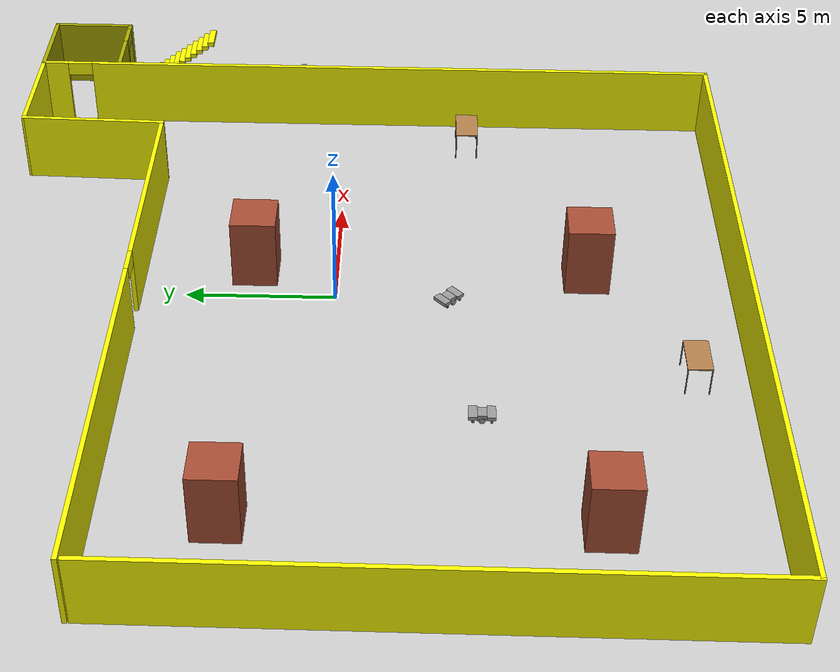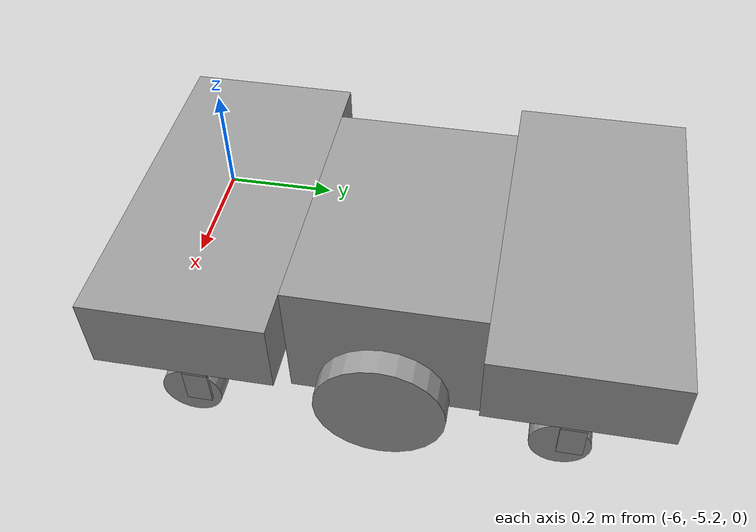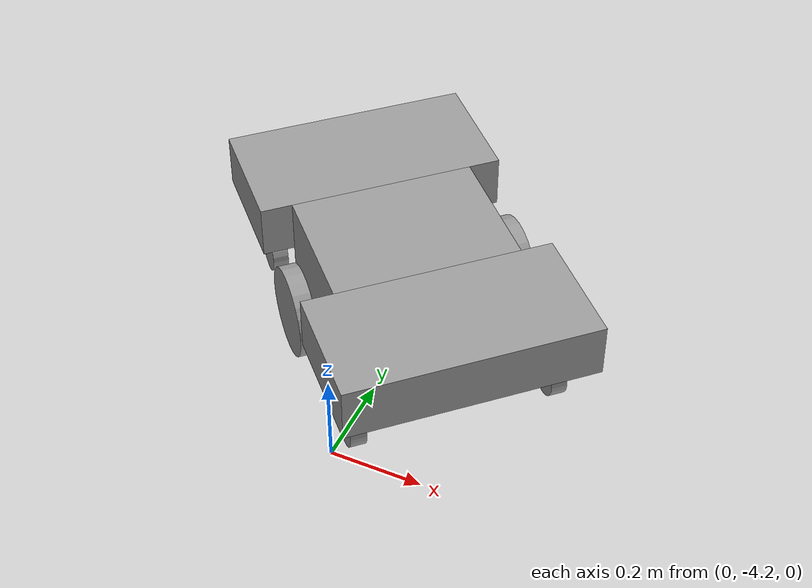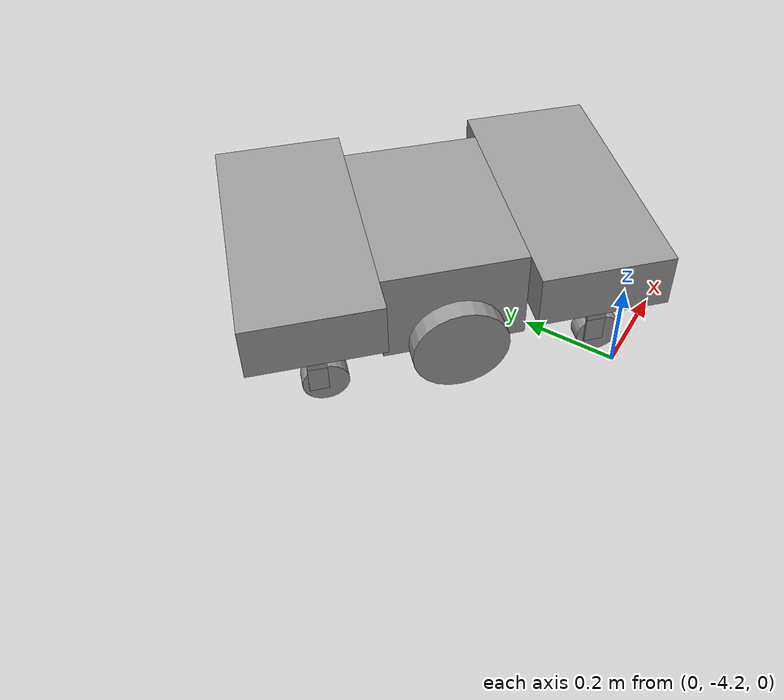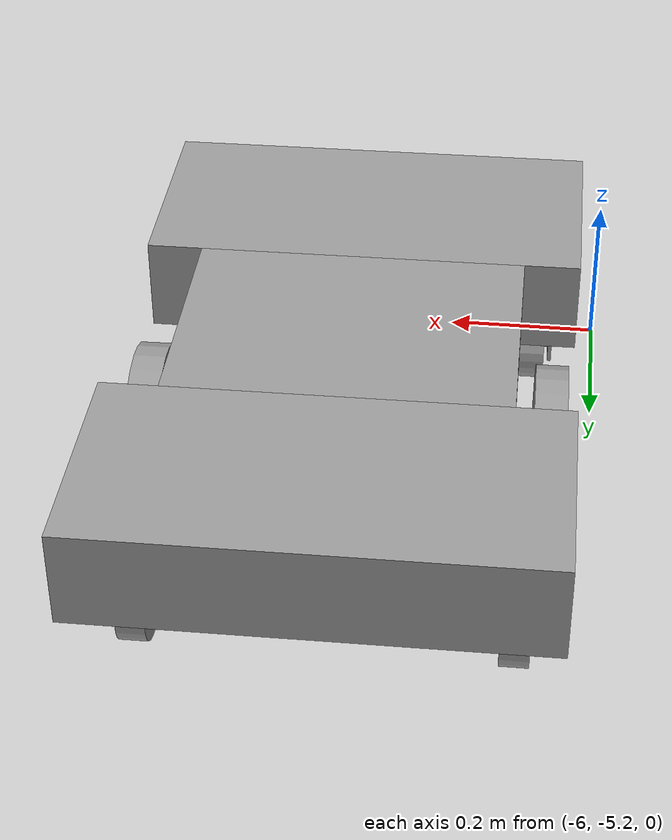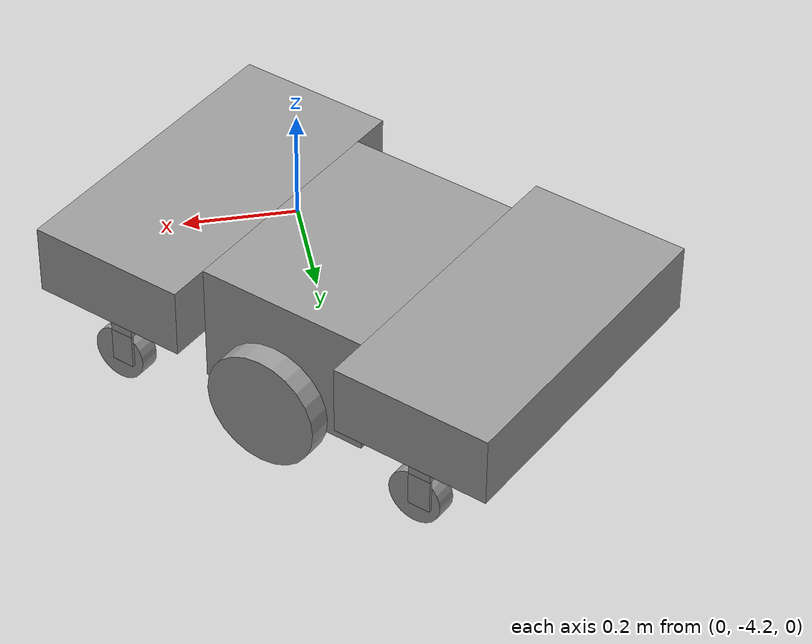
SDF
<sdf version="1.6">
 <world name="default">
  <plugin name="description" filename="libdescription.so"/>
  <light name="sun" type="directional">
   <pose>0 0 10 0 -0 0</pose>
   <diffuse>0.8 0.8 0.8 1</diffuse>
   <specular>0.1 0.1 0.1 1</specular>
   <attenuation>
    <range>1000</range>
    <constant>0.9</constant>
    <linear>0.01</linear>
    <quadratic>0.001</quadratic>
   </attenuation>
   <direction>-0.5 0.5 -1</direction>
  </light>
  <model name="ground_plane">
   <static>1</static>
   <link name="link">
    <collision name="collision">
     <geometry><plane><normal>0 0 1</normal><size>100 100</size></plane></geometry>
     <surface><friction><ode><mu>100</mu><mu2>50</mu2></ode></friction></surface>
    </collision>
    <visual name="visual">
     <cast_shadows>0</cast_shadows>
     <geometry><plane><normal>0 0 1</normal><size>100 100</size></plane></geometry>
     <material>
      <script><uri>file://media/materials/scripts/gazebo.material</uri><name>Gazebo/Grey</name></script>
     </material>
    </visual>
   </link>
  </model>
  <gravity>0 0 -9.8</gravity>
  <magnetic_field>6e-06 2.3e-05 -4.2e-05</magnetic_field>
  <atmosphere type="adiabatic"/>
  <physics name="default_physics" default="0" type="ode">
   <max_step_size>0.001</max_step_size>
   <real_time_factor>1</real_time_factor>
   <real_time_update_rate>1000</real_time_update_rate>
  </physics>
  <scene><ambient>0.4 0.4 0.4 1</ambient><background>0.7 0.7 0.7 1</background><shadows>1</shadows></scene>
  <spherical_coordinates>
   <surface_model>EARTH_WGS84</surface_model>
   <latitude_deg>0</latitude_deg>
   <longitude_deg>0</longitude_deg>
   <elevation>0</elevation>
   <heading_deg>0</heading_deg>
  </spherical_coordinates>
  <model name="basement_updated">
   <pose>-0.239586 -0.871456 0 0 -0 0</pose>
   <link name="Door_3">
    <collision name="Door_3_Collision">
     <geometry><box><size>0.9 0.17 2</size></box></geometry>
     <pose>0 0 1 0 -0 0</pose>
    </collision>
    <visual name="Door_3_Visual">
     <pose>0 0 1 0 -0 0</pose>
     <geometry><box><size>0.9 0.17 2</size></box></geometry>
     <material>
      <script><uri>file://media/materials/scripts/gazebo.material</uri><name>Gazebo/Grey</name></script>
     </material>
    </visual>
    <pose>11.5491 2.65287 0 0 -0 0</pose>
   </link>
   <link name="Stairs_0">
    <visual name="Stairs_0_Visual_0">
     <pose>13.1146 9.55196 0.083333 0 -0 0</pose>
     <geometry><box><size>1 0.233333 0.166667</size></box></geometry>
     <material>
      <script><uri>file://media/materials/scripts/gazebo.material</uri><name>Gazebo/Grey</name></script>
      <ambient>1 1 0 1</ambient>
     </material>
    </visual>
    <collision name="Stairs_0_Collision_0">
     <geometry><box><size>1 0.233333 0.166667</size></box></geometry>
     <pose>13.1146 9.55196 0.083333 0 -0 0</pose>
    </collision>
    <visual name="Stairs_0_Visual_1">
     <pose>13.1146 9.31863 0.25 0 -0 0</pose>
     <geometry><box><size>1 0.233333 0.166667</size></box></geometry>
     <material>
      <script><uri>file://media/materials/scripts/gazebo.material</uri><name>Gazebo/Grey</name></script>
      <ambient>1 1 0 1</ambient>
     </material>
    </visual>
    <collision name="Stairs_0_Collision_1">
     <geometry><box><size>1 0.233333 0.166667</size></box></geometry>
     <pose>13.1146 9.31863 0.25 0 -0 0</pose>
    </collision>
    <visual name="Stairs_0_Visual_2">
     <pose>13.1146 9.0853 0.416667 0 -0 0</pose>
     <geometry><box><size>1 0.233333 0.166667</size></box></geometry>
     <material>
      <script><uri>file://media/materials/scripts/gazebo.material</uri><name>Gazebo/Grey</name></script>
      <ambient>1 1 0 1</ambient>
     </material>
    </visual>
    <collision name="Stairs_0_Collision_2">
     <geometry><box><size>1 0.233333 0.166667</size></box></geometry>
     <pose>13.1146 9.0853 0.416667 0 -0 0</pose>
    </collision>
    <visual name="Stairs_0_Visual_3">
     <pose>13.1146 8.85196 0.583333 0 -0 0</pose>
     <geometry><box><size>1 0.233333 0.166667</size></box></geometry>
     <material>
      <script><uri>file://media/materials/scripts/gazebo.material</uri><name>Gazebo/Grey</name></script>
      <ambient>1 1 0 1</ambient>
     </material>
    </visual>
    <collision name="Stairs_0_Collision_3">
     <geometry><box><size>1 0.233333 0.166667</size></box></geometry>
     <pose>13.1146 8.85196 0.583333 0 -0 0</pose>
    </collision>
    <visual name="Stairs_0_Visual_4">
     <pose>13.1146 8.61863 0.75 0 -0 0</pose>
     <geometry><box><size>1 0.233333 0.166667</size></box></geometry>
     <material>
      <script><uri>file://media/materials/scripts/gazebo.material</uri><name>Gazebo/Grey</name></script>
      <ambient>1 1 0 1</ambient>
     </material>
    </visual>
    <collision name="Stairs_0_Collision_4">
     <geometry><box><size>1 0.233333 0.166667</size></box></geometry>
     <pose>13.1146 8.61863 0.75 0 -0 0</pose>
    </collision>
    <visual name="Stairs_0_Visual_5">
     <pose>13.1146 8.3853 0.916667 0 -0 0</pose>
     <geometry><box><size>1 0.233333 0.166667</size></box></geometry>
     <material>
      <script><uri>file://media/materials/scripts/gazebo.material</uri><name>Gazebo/Grey</name></script>
      <ambient>1 1 0 1</ambient>
     </material>
    </visual>
    <collision name="Stairs_0_Collision_5">
     <geometry><box><size>1 0.233333 0.166667</size></box></geometry>
     <pose>13.1146 8.3853 0.916667 0 -0 0</pose>
    </collision>
    <visual name="Stairs_0_Visual_6">
     <pose>13.1146 8.15196 1.08333 0 -0 0</pose>
     <geometry><box><size>1 0.233333 0.166667</size></box></geometry>
     <material>
      <script><uri>file://media/materials/scripts/gazebo.material</uri><name>Gazebo/Grey</name></script>
      <ambient>1 1 0 1</ambient>
     </material>
    </visual>
    <collision name="Stairs_0_Collision_6">
     <geometry><box><size>1 0.233333 0.166667</size></box></geometry>
     <pose>13.1146 8.15196 1.08333 0 -0 0</pose>
    </collision>
    <visual name="Stairs_0_Visual_7">
     <pose>13.1146 7.91863 1.25 0 -0 0</pose>
     <geometry><box><size>1 0.233333 0.166667</size></box></geometry>
     <material>
      <script><uri>file://media/materials/scripts/gazebo.material</uri><name>Gazebo/Grey</name></script>
      <ambient>1 1 0 1</ambient>
     </material>
    </visual>
    <collision name="Stairs_0_Collision_7">
     <geometry><box><size>1 0.233333 0.166667</size></box></geometry>
     <pose>13.1146 7.91863 1.25 0 -0 0</pose>
    </collision>
    <visual name="Stairs_0_Visual_8">
     <pose>13.1146 7.6853 1.41667 0 -0 0</pose>
     <geometry><box><size>1 0.233333 0.166667</size></box></geometry>
     <material>
      <script><uri>file://media/materials/scripts/gazebo.material</uri><name>Gazebo/Grey</name></script>
      <ambient>1 1 0 1</ambient>
     </material>
    </visual>
    <collision name="Stairs_0_Collision_8">
     <geometry><box><size>1 0.233333 0.166667</size></box></geometry>
     <pose>13.1146 7.6853 1.41667 0 -0 0</pose>
    </collision>
    <visual name="Stairs_0_Visual_9">
     <pose>13.1146 7.45196 1.58333 0 -0 0</pose>
     <geometry><box><size>1 0.233333 0.166667</size></box></geometry>
     <material>
      <script><uri>file://media/materials/scripts/gazebo.material</uri><name>Gazebo/Grey</name></script>
      <ambient>1 1 0 1</ambient>
     </material>
    </visual>
    <collision name="Stairs_0_Collision_9">
     <geometry><box><size>1 0.233333 0.166667</size></box></geometry>
     <pose>13.1146 7.45196 1.58333 0 -0 0</pose>
    </collision>
    <visual name="Stairs_0_Visual_10">
     <pose>13.1146 7.21863 1.75 0 -0 0</pose>
     <geometry><box><size>1 0.233333 0.166667</size></box></geometry>
     <material>
      <script><uri>file://media/materials/scripts/gazebo.material</uri><name>Gazebo/Grey</name></script>
      <ambient>1 1 0 1</ambient>
     </material>
    </visual>
    <collision name="Stairs_0_Collision_10">
     <geometry><box><size>1 0.233333 0.166667</size></box></geometry>
     <pose>13.1146 7.21863 1.75 0 -0 0</pose>
    </collision>
    <visual name="Stairs_0_Visual_11">
     <pose>13.1146 6.9853 1.91667 0 -0 0</pose>
     <geometry><box><size>1 0.233333 0.166667</size></box></geometry>
     <material>
      <script><uri>file://media/materials/scripts/gazebo.material</uri><name>Gazebo/Grey</name></script>
      <ambient>1 1 0 1</ambient>
     </material>
    </visual>
    <collision name="Stairs_0_Collision_11">
     <geometry><box><size>1 0.233333 0.166667</size></box></geometry>
     <pose>13.1146 6.9853 1.91667 0 -0 0</pose>
    </collision>
    <visual name="Stairs_0_Visual_12">
     <pose>13.1146 6.75196 2.08333 0 -0 0</pose>
     <geometry><box><size>1 0.233333 0.166667</size></box></geometry>
     <material>
      <script><uri>file://media/materials/scripts/gazebo.material</uri><name>Gazebo/Grey</name></script>
      <ambient>1 1 0 1</ambient>
     </material>
    </visual>
    <collision name="Stairs_0_Collision_12">
     <geometry><box><size>1 0.233333 0.166667</size></box></geometry>
     <pose>13.1146 6.75196 2.08333 0 -0 0</pose>
    </collision>
    <visual name="Stairs_0_Visual_13">
     <pose>13.1146 6.51863 2.25 0 -0 0</pose>
     <geometry><box><size>1 0.233333 0.166667</size></box></geometry>
     <material>
      <script><uri>file://media/materials/scripts/gazebo.material</uri><name>Gazebo/Grey</name></script>
      <ambient>1 1 0 1</ambient>
     </material>
    </visual>
    <collision name="Stairs_0_Collision_13">
     <geometry><box><size>1 0.233333 0.166667</size></box></geometry>
     <pose>13.1146 6.51863 2.25 0 -0 0</pose>
    </collision>
    <visual name="Stairs_0_Visual_14">
     <pose>13.1146 6.2853 2.41667 0 -0 0</pose>
     <geometry><box><size>1 0.233333 0.166667</size></box></geometry>
     <material>
      <script><uri>file://media/materials/scripts/gazebo.material</uri><name>Gazebo/Grey</name></script>
      <ambient>1 1 0 1</ambient>
     </material>
    </visual>
    <collision name="Stairs_0_Collision_14">
     <geometry><box><size>1 0.233333 0.166667</size></box></geometry>
     <pose>13.1146 6.2853 2.41667 0 -0 0</pose>
    </collision>
   </link>
   <link name="Wall_0">
    <collision name="Wall_0_Collision">
     <geometry><box><size>19.8118 0.15 2.5</size></box></geometry>
     <pose>0 0 1.25 0 -0 0</pose>
    </collision>
    <visual name="Wall_0_Visual">
     <pose>0 0 1.25 0 -0 0</pose>
     <geometry><box><size>19.8118 0.15 2.5</size></box></geometry>
     <material>
      <script><uri>file://media/materials/scripts/gazebo.material</uri><name>Gazebo/Grey</name></script>
      <ambient>1 1 0 1</ambient>
     </material>
    </visual>
    <pose>-13.85 -2.59522 0 0 0 -1.5708</pose>
   </link>
   <link name="Wall_13">
    <pose>-3.425 7.42389 0 0 -0 0</pose>
    <visual name="Wall_13_Visual_0">
     <pose>-4.32108 0 1.25 0 -0 0</pose>
     <geometry><box><size>12.3578 0.15 2.5</size></box></geometry>
     <material>
      <script><uri>file://media/materials/scripts/gazebo.material</uri><name>Gazebo/Grey</name></script>
      <ambient>1 1 0 1</ambient>
     </material>
    </visual>
    <collision name="Wall_13_Collision_0">
     <geometry><box><size>12.3578 0.15 2.5</size></box></geometry>
     <pose>-4.32108 0 1.25 0 -0 0</pose>
    </collision>
    <visual name="Wall_13_Visual_1">
     <pose>6.62892 0 1.25 0 -0 0</pose>
     <geometry><box><size>7.74215 0.15 2.5</size></box></geometry>
     <material>
      <script><uri>file://media/materials/scripts/gazebo.material</uri><name>Gazebo/Grey</name></script>
      <ambient>1 1 0 1</ambient>
     </material>
    </visual>
    <collision name="Wall_13_Collision_1">
     <geometry><box><size>7.74215 0.15 2.5</size></box></geometry>
     <pose>6.62892 0 1.25 0 -0 0</pose>
    </collision>
    <visual name="Wall_13_Visual_2">
     <pose>2.30785 0 2.25 0 -0 0</pose>
     <geometry><box><size>0.9 0.15 0.5</size></box></geometry>
     <material>
      <script><uri>file://media/materials/scripts/gazebo.material</uri><name>Gazebo/Grey</name></script>
      <ambient>1 1 0 1</ambient>
     </material>
    </visual>
    <collision name="Wall_13_Collision_2">
     <geometry><box><size>0.9 0.15 0.5</size></box></geometry>
     <pose>2.30785 0 2.25 0 -0 0</pose>
    </collision>
   </link>
   <link name="Wall_17">
    <pose>11 -0.001107 0 0 -0 1.5708</pose>
    <visual name="Wall_17_Visual_0">
     <pose>-0.949636 0 1.25 0 -0 0</pose>
     <geometry><box><size>23.1007 0.15 2.5</size></box></geometry>
     <material>
      <script><uri>file://media/materials/scripts/gazebo.material</uri><name>Gazebo/Grey</name></script>
      <ambient>1 1 0 1</ambient>
     </material>
    </visual>
    <collision name="Wall_17_Collision_0">
     <geometry><box><size>23.1007 0.15 2.5</size></box></geometry>
     <pose>-0.949636 0 1.25 0 -0 0</pose>
    </collision>
    <visual name="Wall_17_Visual_1">
     <pose>12.0004 0 1.25 0 -0 0</pose>
     <geometry><box><size>0.999273 0.15 2.5</size></box></geometry>
     <material>
      <script><uri>file://media/materials/scripts/gazebo.material</uri><name>Gazebo/Grey</name></script>
      <ambient>1 1 0 1</ambient>
     </material>
    </visual>
    <collision name="Wall_17_Collision_1">
     <geometry><box><size>0.999273 0.15 2.5</size></box></geometry>
     <pose>12.0004 0 1.25 0 -0 0</pose>
    </collision>
    <visual name="Wall_17_Visual_2">
     <pose>11.0507 0 2.25 0 -0 0</pose>
     <geometry><box><size>0.9 0.15 0.5</size></box></geometry>
     <material>
      <script><uri>file://media/materials/scripts/gazebo.material</uri><name>Gazebo/Grey</name></script>
      <ambient>1 1 0 1</ambient>
     </material>
    </visual>
    <collision name="Wall_17_Collision_2">
     <geometry><box><size>0.9 0.15 0.5</size></box></geometry>
     <pose>11.0507 0 2.25 0 -0 0</pose>
    </collision>
   </link>
   <link name="Wall_20">
    <collision name="Wall_20_Collision">
     <geometry><box><size>4 0.15 2.5</size></box></geometry>
     <pose>0 0 1.25 0 -0 0</pose>
    </collision>
    <visual name="Wall_20_Visual">
     <pose>0 0 1.25 0 -0 0</pose>
     <geometry><box><size>4 0.15 2.5</size></box></geometry>
     <material>
      <script><uri>file://media/materials/scripts/gazebo.material</uri><name>Gazebo/Grey</name></script>
      <ambient>1 1 0 1</ambient>
     </material>
    </visual>
    <pose>9.075 12.4239 0 0 -0 3.14159</pose>
   </link>
   <link name="Wall_24">
    <collision name="Wall_24_Collision">
     <geometry><box><size>5.15225 0.15 2.5</size></box></geometry>
     <pose>0 0 1.25 0 -0 0</pose>
    </collision>
    <visual name="Wall_24_Visual">
     <pose>0 0 1.25 0 -0 0</pose>
     <geometry><box><size>5.15225 0.15 2.5</size></box></geometry>
     <material>
      <script><uri>file://media/materials/scripts/gazebo.material</uri><name>Gazebo/Grey</name></script>
      <ambient>1 1 0 1</ambient>
     </material>
    </visual>
    <pose>7.075 9.92389 0 0 -0 1.5408</pose>
   </link>
   <link name="Wall_26">
    <collision name="Wall_26_Collision">
     <geometry><box><size>1.51 1.5 2.5</size></box></geometry>
     <pose>0 0 1.25 0 -0 0</pose>
    </collision>
    <visual name="Wall_26_Visual">
     <pose>0 0 1.25 0 -0 0</pose>
     <geometry><box><size>1.51 1.5 2.5</size></box></geometry>
     <material>
      <script><uri>file://media/materials/scripts/gazebo.material</uri><name>Gazebo/Bricks</name></script>
      <ambient>1 1 1 1</ambient>
     </material>
    </visual>
    <pose>-10.1524 3.68806 0 0 -0 1.5708</pose>
   </link>
   <link name="Wall_28">
    <collision name="Wall_28_Collision">
     <geometry><box><size>1.51 1.5 2.5</size></box></geometry>
     <pose>0 0 1.25 0 -0 0</pose>
    </collision>
    <visual name="Wall_28_Visual">
     <pose>0 0 1.25 0 -0 0</pose>
     <geometry><box><size>1.51 1.5 2.5</size></box></geometry>
     <material>
      <script><uri>file://media/materials/scripts/gazebo.material</uri><name>Gazebo/Bricks</name></script>
      <ambient>1 1 1 1</ambient>
     </material>
    </visual>
    <pose>1.58088 3.61659 0 0 0 -1.5708</pose>
   </link>
   <link name="Wall_30">
    <collision name="Wall_30_Collision">
     <geometry><box><size>1.51 1.5 2.5</size></box></geometry>
     <pose>0 0 1.25 0 -0 0</pose>
    </collision>
    <visual name="Wall_30_Visual">
     <pose>0 0 1.25 0 -0 0</pose>
     <geometry><box><size>1.51 1.5 2.5</size></box></geometry>
     <material>
      <script><uri>file://media/materials/scripts/gazebo.material</uri><name>Gazebo/Bricks</name></script>
      <ambient>1 1 1 1</ambient>
     </material>
    </visual>
    <pose>-10.1281 -7.46052 0 0 0 -1.5708</pose>
   </link>
   <link name="Wall_33">
    <collision name="Wall_33_Collision">
     <geometry><box><size>1.51 1.5 2.5</size></box></geometry>
     <pose>0 0 1.25 0 -0 0</pose>
    </collision>
    <visual name="Wall_33_Visual">
     <pose>0 0 1.25 0 -0 0</pose>
     <geometry><box><size>1.51 1.5 2.5</size></box></geometry>
     <material>
      <script><uri>file://media/materials/scripts/gazebo.material</uri><name>Gazebo/Bricks</name></script>
      <ambient>1 1 1 1</ambient>
     </material>
    </visual>
    <pose>1.5253 -7.5316 0 0 -0 1.5708</pose>
   </link>
   <link name="Wall_35">
    <collision name="Wall_35_Collision">
     <geometry><box><size>3 0.15 2.5</size></box></geometry>
     <pose>0 0 1.25 0 -0 0</pose>
    </collision>
    <visual name="Wall_35_Visual">
     <pose>0 0 1.25 0 -0 0</pose>
     <geometry><box><size>3 0.15 2.5</size></box></geometry>
     <material>
      <script><uri>file://media/materials/scripts/gazebo.material</uri><name>Gazebo/Grey</name></script>
      <ambient>0.666667 0.666667 0 1</ambient>
     </material>
    </visual>
    <pose>12.425 12.4239 0 0 -0 0</pose>
   </link>
   <link name="Wall_37">
    <collision name="Wall_37_Collision">
     <geometry><box><size>3 0.15 2.5</size></box></geometry>
     <pose>0 0 1.25 0 -0 0</pose>
    </collision>
    <visual name="Wall_37_Visual">
     <pose>0 0 1.25 0 -0 0</pose>
     <geometry><box><size>3 0.15 2.5</size></box></geometry>
     <material>
      <script><uri>file://media/materials/scripts/gazebo.material</uri><name>Gazebo/Grey</name></script>
      <ambient>0.666667 0.666667 0 1</ambient>
     </material>
    </visual>
    <pose>13.85 10.9989 0 0 0 -1.5708</pose>
   </link>
   <link name="Wall_39">
    <pose>12.425 9.57389 0 0 -0 3.14159</pose>
    <visual name="Wall_39_Visual_0">
     <pose>-1.31981 0 1.25 0 -0 0</pose>
     <geometry><box><size>0.360381 0.15 2.5</size></box></geometry>
     <material>
      <script><uri>file://media/materials/scripts/gazebo.material</uri><name>Gazebo/Grey</name></script>
      <ambient>0.666667 0.666667 0 1</ambient>
     </material>
    </visual>
    <collision name="Wall_39_Collision_0">
     <geometry><box><size>0.360381 0.15 2.5</size></box></geometry>
     <pose>-1.31981 0 1.25 0 -0 0</pose>
    </collision>
    <visual name="Wall_39_Visual_1">
     <pose>0.630191 0 1.25 0 -0 0</pose>
     <geometry><box><size>1.73962 0.15 2.5</size></box></geometry>
     <material>
      <script><uri>file://media/materials/scripts/gazebo.material</uri><name>Gazebo/Grey</name></script>
      <ambient>0.666667 0.666667 0 1</ambient>
     </material>
    </visual>
    <collision name="Wall_39_Collision_1">
     <geometry><box><size>1.73962 0.15 2.5</size></box></geometry>
     <pose>0.630191 0 1.25 0 -0 0</pose>
    </collision>
    <visual name="Wall_39_Visual_2">
     <pose>-0.689619 0 2.25 0 -0 0</pose>
     <geometry><box><size>0.9 0.15 0.5</size></box></geometry>
     <material>
      <script><uri>file://media/materials/scripts/gazebo.material</uri><name>Gazebo/Grey</name></script>
      <ambient>0.666667 0.666667 0 1</ambient>
     </material>
    </visual>
    <collision name="Wall_39_Collision_2">
     <geometry><box><size>0.9 0.15 0.5</size></box></geometry>
     <pose>-0.689619 0 2.25 0 -0 0</pose>
    </collision>
   </link>
   <link name="Wall_8">
    <collision name="Wall_8_Collision">
     <geometry><box><size>25 0.15 2.5</size></box></geometry>
     <pose>0 0 1.25 0 -0 0</pose>
    </collision>
    <visual name="Wall_8_Visual">
     <pose>0 0 1.25 0 -0 0</pose>
     <geometry><box><size>25 0.15 2.5</size></box></geometry>
     <material>
      <script><uri>file://media/materials/scripts/gazebo.material</uri><name>Gazebo/Grey</name></script>
      <ambient>1 1 0 1</ambient>
     </material>
    </visual>
    <pose>-1.425 -12.4261 0 0 -0 0</pose>
   </link>
   <static>1</static>
  </model>
  <model name="mr100_final_last_5">
   <link name="link_0">
    <pose>-0.033846 -0.331731 0.065619 0 -0 0</pose>
    <inertial>
     <mass>1</mass>
     <inertia>
      <ixx>0.166667</ixx>
      <ixy>0</ixy>
      <ixz>0</ixz>
      <iyy>0.166667</iyy>
      <iyz>0</iyz>
      <izz>0.166667</izz>
     </inertia>
    </inertial>
    <visual name="visual">
     <geometry><box><size>0.55 0.275 0.12</size></box></geometry>
     <material>
      <lighting>1</lighting>
      <script><uri>file://media/materials/scripts/gazebo.material</uri><name>Gazebo/Grey</name></script>
      <ambient>0.3 0.3 0.3 1</ambient>
      <diffuse>0.7 0.7 0.7 1</diffuse>
      <specular>0.01 0.01 0.01 1</specular>
      <emissive>0.9 0 0 1</emissive>
      <shader type="vertex"><normal_map>__default__</normal_map></shader>
     </material>
    </visual>
    <collision name="collision">
     <geometry><box><size>0.55 0.275 0.12</size></box></geometry>
     <surface>
      <friction>
       <ode><mu>1</mu><mu2>1</mu2><fdir1>0 0 0</fdir1><slip1>0</slip1><slip2>0</slip2></ode>
       <torsional>
        <coefficient>1</coefficient>
        <patch_radius>0</patch_radius>
        <surface_radius>0</surface_radius>
        <use_patch_radius>1</use_patch_radius>
        <ode><slip>0</slip></ode>
       </torsional>
      </friction>
      <bounce><restitution_coefficient>0</restitution_coefficient><threshold>1e+06</threshold></bounce>
      <contact>
       <collide_without_contact>0</collide_without_contact>
       <collide_without_contact_bitmask>1</collide_without_contact_bitmask>
       <collide_bitmask>1</collide_bitmask>
       <ode>
        <soft_cfm>0</soft_cfm>
        <soft_erp>0.2</soft_erp>
        <kp>1e+13</kp>
        <kd>1</kd>
        <max_vel>0.01</max_vel>
        <min_depth>0</min_depth>
       </ode>
       <bullet>
        <split_impulse>1</split_impulse>
        <split_impulse_penetration_threshold>-0.01</split_impulse_penetration_threshold>
        <soft_cfm>0</soft_cfm>
        <soft_erp>0.2</soft_erp>
        <kp>1e+13</kp>
        <kd>1</kd>
       </bullet>
      </contact>
     </surface>
    </collision>
   </link>
   <link name="link_0_0">
    <pose>-0.273846 -0.346731 -0.094381 0 -0 0</pose>
    <inertial>
     <mass>1</mass>
     <inertia><ixx>0.145833</ixx><ixy>0</ixy><ixz>0</ixz><iyy>0.145833</iyy><iyz>0</iyz><izz>0.125</izz></inertia>
    </inertial>
    <visual name="visual">
     <pose>0 0 0 1.57 -0 1.57</pose>
     <geometry><cylinder><radius>0.005</radius><length>0.005</length></cylinder></geometry>
     <material>
      <lighting>1</lighting>
      <script><uri>file://media/materials/scripts/gazebo.material</uri><name>Gazebo/Grey</name></script>
      <ambient>0.3 0.3 0.3 1</ambient>
      <diffuse>0.7 0.7 0.7 1</diffuse>
      <specular>0.01 0.01 0.01 1</specular>
      <emissive>0 0 0 1</emissive>
      <shader type="vertex"><normal_map>__default__</normal_map></shader>
     </material>
    </visual>
    <collision name="collision">
     <pose>0 0 0 1.57 -0 1.57</pose>
     <geometry><cylinder><radius>0.005</radius><length>0.005</length></cylinder></geometry>
     <surface>
      <friction>
       <ode><mu>1</mu><mu2>1</mu2><fdir1>0 0 0</fdir1><slip1>0</slip1><slip2>0</slip2></ode>
       <torsional>
        <coefficient>1</coefficient>
        <patch_radius>0</patch_radius>
        <surface_radius>0</surface_radius>
        <use_patch_radius>1</use_patch_radius>
        <ode><slip>0</slip></ode>
       </torsional>
      </friction>
      <bounce><restitution_coefficient>0</restitution_coefficient><threshold>1e+06</threshold></bounce>
      <contact>
       <collide_without_contact>0</collide_without_contact>
       <collide_without_contact_bitmask>1</collide_without_contact_bitmask>
       <collide_bitmask>1</collide_bitmask>
       <ode>
        <soft_cfm>0</soft_cfm>
        <soft_erp>0.2</soft_erp>
        <kp>1e+13</kp>
        <kd>1</kd>
        <max_vel>0.01</max_vel>
        <min_depth>0</min_depth>
       </ode>
       <bullet>
        <split_impulse>1</split_impulse>
        <split_impulse_penetration_threshold>-0.01</split_impulse_penetration_threshold>
        <soft_cfm>0</soft_cfm>
        <soft_erp>0.2</soft_erp>
        <kp>1e+13</kp>
        <kd>1</kd>
       </bullet>
      </contact>
     </surface>
    </collision>
   </link>
   <link name="link_0_0_clone">
    <pose>-0.273846 0.228269 -0.094381 0 -0 0</pose>
    <inertial>
     <mass>1</mass>
     <inertia><ixx>0.145833</ixx><ixy>0</ixy><ixz>0</ixz><iyy>0.145833</iyy><iyz>0</iyz><izz>0.125</izz></inertia>
    </inertial>
    <visual name="visual_0">
     <pose>0 0 0 1.57 -0 1.57</pose>
     <geometry><cylinder><radius>0.005</radius><length>0.005</length></cylinder></geometry>
     <material>
      <lighting>1</lighting>
      <script><uri>file://media/materials/scripts/gazebo.material</uri><name>Gazebo/Grey</name></script>
      <ambient>0.3 0.3 0.3 1</ambient>
      <diffuse>0.7 0.7 0.7 1</diffuse>
      <specular>0.01 0.01 0.01 1</specular>
      <emissive>0 0 0 1</emissive>
      <shader type="vertex"><normal_map>__default__</normal_map></shader>
     </material>
    </visual>
    <collision name="collision">
     <pose>0 0 0 1.57 -0 1.57</pose>
     <geometry><cylinder><radius>0.005</radius><length>0.005</length></cylinder></geometry>
     <surface>
      <friction>
       <ode><mu>1</mu><mu2>1</mu2><fdir1>0 0 0</fdir1><slip1>0</slip1><slip2>0</slip2></ode>
       <torsional>
        <coefficient>1</coefficient>
        <patch_radius>0</patch_radius>
        <surface_radius>0</surface_radius>
        <use_patch_radius>1</use_patch_radius>
        <ode><slip>0</slip></ode>
       </torsional>
      </friction>
      <bounce><restitution_coefficient>0</restitution_coefficient><threshold>1e+06</threshold></bounce>
      <contact>
       <collide_without_contact>0</collide_without_contact>
       <collide_without_contact_bitmask>1</collide_without_contact_bitmask>
       <collide_bitmask>1</collide_bitmask>
       <ode>
        <soft_cfm>0</soft_cfm>
        <soft_erp>0.2</soft_erp>
        <kp>1e+13</kp>
        <kd>1</kd>
        <max_vel>0.01</max_vel>
        <min_depth>0</min_depth>
       </ode>
       <bullet>
        <split_impulse>1</split_impulse>
        <split_impulse_penetration_threshold>-0.01</split_impulse_penetration_threshold>
        <soft_cfm>0</soft_cfm>
        <soft_erp>0.2</soft_erp>
        <kp>1e+13</kp>
        <kd>1</kd>
       </bullet>
      </contact>
     </surface>
    </collision>
   </link>
   <link name="link_0_0_clone_clone">
    <pose>0.166154 0.228269 -0.094381 0 -0 0</pose>
    <inertial>
     <mass>1</mass>
     <inertia><ixx>0.145833</ixx><ixy>0</ixy><ixz>0</ixz><iyy>0.145833</iyy><iyz>0</iyz><izz>0.125</izz></inertia>
    </inertial>
    <visual name="visual_0">
     <pose>0 0 0 1.57 -0 1.57</pose>
     <geometry><cylinder><radius>0.005</radius><length>0.005</length></cylinder></geometry>
     <material>
      <lighting>1</lighting>
      <script><uri>file://media/materials/scripts/gazebo.material</uri><name>Gazebo/Grey</name></script>
      <ambient>0.3 0.3 0.3 1</ambient>
      <diffuse>0.7 0.7 0.7 1</diffuse>
      <specular>0.01 0.01 0.01 1</specular>
      <emissive>0 0 0 1</emissive>
      <shader type="vertex"><normal_map>__default__</normal_map></shader>
     </material>
    </visual>
    <collision name="collision">
     <pose>0 0 0 1.57 -0 1.57</pose>
     <geometry><cylinder><radius>0.005</radius><length>0.005</length></cylinder></geometry>
     <surface>
      <friction>
       <ode><mu>1</mu><mu2>1</mu2><fdir1>0 0 0</fdir1><slip1>0</slip1><slip2>0</slip2></ode>
       <torsional>
        <coefficient>1</coefficient>
        <patch_radius>0</patch_radius>
        <surface_radius>0</surface_radius>
        <use_patch_radius>1</use_patch_radius>
        <ode><slip>0</slip></ode>
       </torsional>
      </friction>
      <bounce><restitution_coefficient>0</restitution_coefficient><threshold>1e+06</threshold></bounce>
      <contact>
       <collide_without_contact>0</collide_without_contact>
       <collide_without_contact_bitmask>1</collide_without_contact_bitmask>
       <collide_bitmask>1</collide_bitmask>
       <ode>
        <soft_cfm>0</soft_cfm>
        <soft_erp>0.2</soft_erp>
        <kp>1e+13</kp>
        <kd>1</kd>
        <max_vel>0.01</max_vel>
        <min_depth>0</min_depth>
       </ode>
       <bullet>
        <split_impulse>1</split_impulse>
        <split_impulse_penetration_threshold>-0.01</split_impulse_penetration_threshold>
        <soft_cfm>0</soft_cfm>
        <soft_erp>0.2</soft_erp>
        <kp>1e+13</kp>
        <kd>1</kd>
       </bullet>
      </contact>
     </surface>
    </collision>
   </link>
   <link name="link_0_0_clone_clone_clone">
    <pose>0.166154 -0.346731 -0.094381 0 -0 0</pose>
    <inertial>
     <mass>1</mass>
     <inertia><ixx>0.145833</ixx><ixy>0</ixy><ixz>0</ixz><iyy>0.145833</iyy><iyz>0</iyz><izz>0.125</izz></inertia>
    </inertial>
    <visual name="visual_0">
     <pose>0 0 0 1.57 -0 1.57</pose>
     <geometry><cylinder><radius>0.005</radius><length>0.005</length></cylinder></geometry>
     <material>
      <lighting>1</lighting>
      <script><uri>file://media/materials/scripts/gazebo.material</uri><name>Gazebo/Grey</name></script>
      <ambient>0.3 0.3 0.3 1</ambient>
      <diffuse>0.7 0.7 0.7 1</diffuse>
      <specular>0.01 0.01 0.01 1</specular>
      <emissive>0 0 0 1</emissive>
      <shader type="vertex"><normal_map>__default__</normal_map></shader>
     </material>
    </visual>
    <collision name="collision">
     <pose>0 0 0 1.57 -0 1.57</pose>
     <geometry><cylinder><radius>0.005</radius><length>0.005</length></cylinder></geometry>
     <surface>
      <friction>
       <ode><mu>1</mu><mu2>1</mu2><fdir1>0 0 0</fdir1><slip1>0</slip1><slip2>0</slip2></ode>
       <torsional>
        <coefficient>1</coefficient>
        <patch_radius>0</patch_radius>
        <surface_radius>0</surface_radius>
        <use_patch_radius>1</use_patch_radius>
        <ode><slip>0</slip></ode>
       </torsional>
      </friction>
      <bounce><restitution_coefficient>0</restitution_coefficient><threshold>1e+06</threshold></bounce>
      <contact>
       <collide_without_contact>0</collide_without_contact>
       <collide_without_contact_bitmask>1</collide_without_contact_bitmask>
       <collide_bitmask>1</collide_bitmask>
       <ode>
        <soft_cfm>0</soft_cfm>
        <soft_erp>0.2</soft_erp>
        <kp>1e+13</kp>
        <kd>1</kd>
        <max_vel>0.01</max_vel>
        <min_depth>0</min_depth>
       </ode>
       <bullet>
        <split_impulse>1</split_impulse>
        <split_impulse_penetration_threshold>-0.01</split_impulse_penetration_threshold>
        <soft_cfm>0</soft_cfm>
        <soft_erp>0.2</soft_erp>
        <kp>1e+13</kp>
        <kd>1</kd>
       </bullet>
      </contact>
     </surface>
    </collision>
   </link>
   <link name="link_0_1">
    <pose>-0.253761 -0.346725 -0.094381 2e-06 -1e-06 0.000281</pose>
    <inertial>
     <mass>1</mass>
     <inertia><ixx>0.145833</ixx><ixy>0</ixy><ixz>0</ixz><iyy>0.145833</iyy><iyz>0</iyz><izz>0.125</izz></inertia>
    </inertial>
    <visual name="visual">
     <pose>0 0 0 1.57 -0 1.57</pose>
     <geometry><cylinder><radius>0.0475</radius><length>0.035</length></cylinder></geometry>
     <material>
      <lighting>1</lighting>
      <script><uri>file://media/materials/scripts/gazebo.material</uri><name>Gazebo/Grey</name></script>
      <ambient>0.3 0.3 0.3 1</ambient>
      <diffuse>0.3 0.3 0.3 1</diffuse>
      <specular>0.01 0.01 0.01 1</specular>
      <emissive>0 0 0 1</emissive>
      <shader type="vertex"><normal_map>__default__</normal_map></shader>
     </material>
    </visual>
    <collision name="collision">
     <pose>0 0 0 1.57 -0 1.57</pose>
     <geometry><cylinder><radius>0.0475</radius><length>0.035</length></cylinder></geometry>
     <surface>
      <friction>
       <ode><mu>1</mu><mu2>1</mu2><fdir1>0 0 0</fdir1><slip1>0</slip1><slip2>0</slip2></ode>
       <torsional>
        <coefficient>1</coefficient>
        <patch_radius>0</patch_radius>
        <surface_radius>0</surface_radius>
        <use_patch_radius>1</use_patch_radius>
        <ode><slip>0</slip></ode>
       </torsional>
      </friction>
      <bounce><restitution_coefficient>0</restitution_coefficient><threshold>1e+06</threshold></bounce>
      <contact>
       <collide_without_contact>0</collide_without_contact>
       <collide_without_contact_bitmask>1</collide_without_contact_bitmask>
       <collide_bitmask>1</collide_bitmask>
       <ode>
        <soft_cfm>0</soft_cfm>
        <soft_erp>0.2</soft_erp>
        <kp>1e+13</kp>
        <kd>1</kd>
        <max_vel>0.01</max_vel>
        <min_depth>0</min_depth>
       </ode>
       <bullet>
        <split_impulse>1</split_impulse>
        <split_impulse_penetration_threshold>-0.01</split_impulse_penetration_threshold>
        <soft_cfm>0</soft_cfm>
        <soft_erp>0.2</soft_erp>
        <kp>1e+13</kp>
        <kd>1</kd>
       </bullet>
      </contact>
     </surface>
    </collision>
   </link>
   <link name="link_0_1_clone">
    <pose>0.186252 -0.346725 -0.094381 4e-06 -2e-06 0.000562</pose>
    <inertial>
     <mass>1</mass>
     <inertia><ixx>0.145833</ixx><ixy>0</ixy><ixz>0</ixz><iyy>0.145833</iyy><iyz>0</iyz><izz>0.125</izz></inertia>
    </inertial>
    <visual name="visual_0">
     <pose>0 0 0 1.57 -0 1.57</pose>
     <geometry><cylinder><radius>0.0475</radius><length>0.035</length></cylinder></geometry>
     <material>
      <lighting>1</lighting>
      <script><uri>file://media/materials/scripts/gazebo.material</uri><name>Gazebo/Grey</name></script>
      <ambient>0.3 0.3 0.3 1</ambient>
      <diffuse>0.3 0.3 0.3 1</diffuse>
      <specular>0 0 0 1</specular>
      <emissive>0 0 0 1</emissive>
      <shader type="vertex"><normal_map>__default__</normal_map></shader>
     </material>
    </visual>
    <collision name="collision">
     <pose>0 0 0 1.57 -0 1.57</pose>
     <geometry><cylinder><radius>0.0475</radius><length>0.035</length></cylinder></geometry>
     <surface>
      <friction>
       <ode><mu>1</mu><mu2>1</mu2><fdir1>0 0 0</fdir1><slip1>0</slip1><slip2>0</slip2></ode>
       <torsional>
        <coefficient>1</coefficient>
        <patch_radius>0</patch_radius>
        <surface_radius>0</surface_radius>
        <use_patch_radius>1</use_patch_radius>
        <ode><slip>0</slip></ode>
       </torsional>
      </friction>
      <bounce><restitution_coefficient>0</restitution_coefficient><threshold>1e+06</threshold></bounce>
      <contact>
       <collide_without_contact>0</collide_without_contact>
       <collide_without_contact_bitmask>1</collide_without_contact_bitmask>
       <collide_bitmask>1</collide_bitmask>
       <ode>
        <soft_cfm>0</soft_cfm>
        <soft_erp>0.2</soft_erp>
        <kp>1e+13</kp>
        <kd>1</kd>
        <max_vel>0.01</max_vel>
        <min_depth>0</min_depth>
       </ode>
       <bullet>
        <split_impulse>1</split_impulse>
        <split_impulse_penetration_threshold>-0.01</split_impulse_penetration_threshold>
        <soft_cfm>0</soft_cfm>
        <soft_erp>0.2</soft_erp>
        <kp>1e+13</kp>
        <kd>1</kd>
       </bullet>
      </contact>
     </surface>
    </collision>
   </link>
   <link name="link_0_1_clone_clone">
    <pose>0.186266 0.228275 -0.094381 6e-06 -3e-06 0.000843</pose>
    <inertial>
     <mass>1</mass>
     <inertia><ixx>0.145833</ixx><ixy>0</ixy><ixz>0</ixz><iyy>0.145833</iyy><iyz>0</iyz><izz>0.125</izz></inertia>
    </inertial>
    <visual name="visual_0">
     <pose>0 0 0 1.57 -0 1.57</pose>
     <geometry><cylinder><radius>0.0475</radius><length>0.035</length></cylinder></geometry>
     <material>
      <lighting>1</lighting>
      <script><uri>file://media/materials/scripts/gazebo.material</uri><name>Gazebo/Grey</name></script>
      <ambient>0.3 0.3 0.3 1</ambient>
      <diffuse>0.3 0.3 0.3 1</diffuse>
      <specular>0.01 0.01 0.01 1</specular>
      <emissive>0 0 0 1</emissive>
      <shader type="vertex"><normal_map>__default__</normal_map></shader>
     </material>
    </visual>
    <collision name="collision">
     <pose>0 0 0 1.57 -0 1.57</pose>
     <geometry><cylinder><radius>0.0475</radius><length>0.035</length></cylinder></geometry>
     <surface>
      <friction>
       <ode><mu>1</mu><mu2>1</mu2><fdir1>0 0 0</fdir1><slip1>0</slip1><slip2>0</slip2></ode>
       <torsional>
        <coefficient>1</coefficient>
        <patch_radius>0</patch_radius>
        <surface_radius>0</surface_radius>
        <use_patch_radius>1</use_patch_radius>
        <ode><slip>0</slip></ode>
       </torsional>
      </friction>
      <bounce><restitution_coefficient>0</restitution_coefficient><threshold>1e+06</threshold></bounce>
      <contact>
       <collide_without_contact>0</collide_without_contact>
       <collide_without_contact_bitmask>1</collide_without_contact_bitmask>
       <collide_bitmask>1</collide_bitmask>
       <ode>
        <soft_cfm>0</soft_cfm>
        <soft_erp>0.2</soft_erp>
        <kp>1e+13</kp>
        <kd>1</kd>
        <max_vel>0.01</max_vel>
        <min_depth>0</min_depth>
       </ode>
       <bullet>
        <split_impulse>1</split_impulse>
        <split_impulse_penetration_threshold>-0.01</split_impulse_penetration_threshold>
        <soft_cfm>0</soft_cfm>
        <soft_erp>0.2</soft_erp>
        <kp>1e+13</kp>
        <kd>1</kd>
       </bullet>
      </contact>
     </surface>
    </collision>
   </link>
   <link name="link_0_1_clone_clone_clone">
    <pose>-0.253721 0.228275 -0.094381 8e-06 -4e-06 0.001124</pose>
    <inertial>
     <mass>1</mass>
     <inertia><ixx>0.145833</ixx><ixy>0</ixy><ixz>0</ixz><iyy>0.145833</iyy><iyz>0</iyz><izz>0.125</izz></inertia>
    </inertial>
    <visual name="visual_0">
     <pose>0 0 0 1.57 -0 1.57</pose>
     <geometry><cylinder><radius>0.0475</radius><length>0.035</length></cylinder></geometry>
     <material>
      <lighting>1</lighting>
      <script><uri>file://media/materials/scripts/gazebo.material</uri><name>Gazebo/Grey</name></script>
      <ambient>0.3 0.3 0.3 1</ambient>
      <diffuse>0.3 0.3 0.3 1</diffuse>
      <specular>0.01 0.01 0.01 1</specular>
      <emissive>0 0 0 1</emissive>
      <shader type="vertex"><normal_map>__default__</normal_map></shader>
     </material>
    </visual>
    <collision name="collision">
     <pose>0 0 0 1.57 -0 1.57</pose>
     <geometry><cylinder><radius>0.0475</radius><length>0.035</length></cylinder></geometry>
     <surface>
      <friction>
       <ode><mu>1</mu><mu2>1</mu2><fdir1>0 0 0</fdir1><slip1>0</slip1><slip2>0</slip2></ode>
       <torsional>
        <coefficient>1</coefficient>
        <patch_radius>0</patch_radius>
        <surface_radius>0</surface_radius>
        <use_patch_radius>1</use_patch_radius>
        <ode><slip>0</slip></ode>
       </torsional>
      </friction>
      <bounce><restitution_coefficient>0</restitution_coefficient><threshold>1e+06</threshold></bounce>
      <contact>
       <collide_without_contact>0</collide_without_contact>
       <collide_without_contact_bitmask>1</collide_without_contact_bitmask>
       <collide_bitmask>1</collide_bitmask>
       <ode>
        <soft_cfm>0</soft_cfm>
        <soft_erp>0.2</soft_erp>
        <kp>1e+13</kp>
        <kd>1</kd>
        <max_vel>0.01</max_vel>
        <min_depth>0</min_depth>
       </ode>
       <bullet>
        <split_impulse>1</split_impulse>
        <split_impulse_penetration_threshold>-0.01</split_impulse_penetration_threshold>
        <soft_cfm>0</soft_cfm>
        <soft_erp>0.2</soft_erp>
        <kp>1e+13</kp>
        <kd>1</kd>
       </bullet>
      </contact>
     </surface>
    </collision>
   </link>
   <link name="link_0_clone">
    <pose>-0.033846 0.243269 0.065619 0 -0 0</pose>
    <inertial>
     <mass>1</mass>
     <inertia>
      <ixx>0.166667</ixx>
      <ixy>0</ixy>
      <ixz>0</ixz>
      <iyy>0.166667</iyy>
      <iyz>0</iyz>
      <izz>0.166667</izz>
     </inertia>
    </inertial>
    <visual name="visual">
     <geometry><box><size>0.55 0.275 0.12</size></box></geometry>
     <material>
      <lighting>1</lighting>
      <script><uri>file://media/materials/scripts/gazebo.material</uri><name>Gazebo/Grey</name></script>
      <ambient>0.3 0.3 0.3 1</ambient>
      <diffuse>0.7 0.7 0.7 1</diffuse>
      <specular>0.01 0.01 0.01 1</specular>
      <emissive>0.9 0 0 1</emissive>
      <shader type="vertex"><normal_map>__default__</normal_map></shader>
     </material>
    </visual>
    <collision name="collision">
     <geometry><box><size>0.55 0.275 0.12</size></box></geometry>
     <surface>
      <friction>
       <ode><mu>1</mu><mu2>1</mu2><fdir1>0 0 0</fdir1><slip1>0</slip1><slip2>0</slip2></ode>
       <torsional>
        <coefficient>1</coefficient>
        <patch_radius>0</patch_radius>
        <surface_radius>0</surface_radius>
        <use_patch_radius>1</use_patch_radius>
        <ode><slip>0</slip></ode>
       </torsional>
      </friction>
      <bounce><restitution_coefficient>0</restitution_coefficient><threshold>1e+06</threshold></bounce>
      <contact>
       <collide_without_contact>0</collide_without_contact>
       <collide_without_contact_bitmask>1</collide_without_contact_bitmask>
       <collide_bitmask>1</collide_bitmask>
       <ode>
        <soft_cfm>0</soft_cfm>
        <soft_erp>0.2</soft_erp>
        <kp>1e+13</kp>
        <kd>1</kd>
        <max_vel>0.01</max_vel>
        <min_depth>0</min_depth>
       </ode>
       <bullet>
        <split_impulse>1</split_impulse>
        <split_impulse_penetration_threshold>-0.01</split_impulse_penetration_threshold>
        <soft_cfm>0</soft_cfm>
        <soft_erp>0.2</soft_erp>
        <kp>1e+13</kp>
        <kd>1</kd>
       </bullet>
      </contact>
     </surface>
    </collision>
   </link>
   <link name="link_1">
    <pose>-0.033846 -0.044231 0.020619 0 -0 0</pose>
    <inertial>
     <mass>1</mass>
     <inertia>
      <ixx>0.166667</ixx>
      <ixy>0</ixy>
      <ixz>0</ixz>
      <iyy>0.166667</iyy>
      <iyz>0</iyz>
      <izz>0.166667</izz>
     </inertia>
    </inertial>
    <visual name="visual">
     <geometry><box><size>0.41 0.3 0.21</size></box></geometry>
     <material>
      <lighting>1</lighting>
      <script><uri>file://media/materials/scripts/gazebo.material</uri><name>Gazebo/Grey</name></script>
      <ambient>0.3 0.3 0.3 1</ambient>
      <diffuse>0.7 0.7 0.7 1</diffuse>
      <specular>0.01 0.01 0.01 1</specular>
      <emissive>0.9 0 0 1</emissive>
      <shader type="vertex"><normal_map>__default__</normal_map></shader>
     </material>
    </visual>
    <collision name="collision">
     <geometry><box><size>0.41 0.3 0.21</size></box></geometry>
     <surface>
      <friction>
       <ode><mu>1</mu><mu2>1</mu2><fdir1>0 0 0</fdir1><slip1>0</slip1><slip2>0</slip2></ode>
       <torsional>
        <coefficient>1</coefficient>
        <patch_radius>0</patch_radius>
        <surface_radius>0</surface_radius>
        <use_patch_radius>1</use_patch_radius>
        <ode><slip>0</slip></ode>
       </torsional>
      </friction>
      <bounce><restitution_coefficient>0</restitution_coefficient><threshold>1e+06</threshold></bounce>
      <contact>
       <collide_without_contact>0</collide_without_contact>
       <collide_without_contact_bitmask>1</collide_without_contact_bitmask>
       <collide_bitmask>1</collide_bitmask>
       <ode>
        <soft_cfm>0</soft_cfm>
        <soft_erp>0.2</soft_erp>
        <kp>1e+13</kp>
        <kd>1</kd>
        <max_vel>0.01</max_vel>
        <min_depth>0</min_depth>
       </ode>
       <bullet>
        <split_impulse>1</split_impulse>
        <split_impulse_penetration_threshold>-0.01</split_impulse_penetration_threshold>
        <soft_cfm>0</soft_cfm>
        <soft_erp>0.2</soft_erp>
        <kp>1e+13</kp>
        <kd>1</kd>
       </bullet>
      </contact>
     </surface>
    </collision>
   </link>
   <link name="link_1_0">
    <pose>0.182511 -0.04226 -0.039381 0 -0 0</pose>
    <inertial>
     <mass>1</mass>
     <inertia><ixx>0.145833</ixx><ixy>0</ixy><ixz>0</ixz><iyy>0.145833</iyy><iyz>0</iyz><izz>0.125</izz></inertia>
    </inertial>
    <visual name="visual">
     <pose>0 0 0 1.57 -0 1.57</pose>
     <geometry><cylinder><radius>0.005</radius><length>0.02</length></cylinder></geometry>
     <material>
      <lighting>1</lighting>
      <script><uri>file://media/materials/scripts/gazebo.material</uri><name>Gazebo/Grey</name></script>
      <ambient>0.3 0.3 0.3 1</ambient>
      <diffuse>0.7 0.7 0.7 1</diffuse>
      <specular>0.01 0.01 0.01 1</specular>
      <emissive>0 0 0 1</emissive>
      <shader type="vertex"><normal_map>__default__</normal_map></shader>
     </material>
    </visual>
    <collision name="collision">
     <pose>0 0 0 1.57 -0 1.57</pose>
     <geometry><cylinder><radius>0.005</radius><length>0.02</length></cylinder></geometry>
     <surface>
      <friction>
       <ode><mu>1</mu><mu2>1</mu2><fdir1>0 0 0</fdir1><slip1>0</slip1><slip2>0</slip2></ode>
       <torsional>
        <coefficient>1</coefficient>
        <patch_radius>0</patch_radius>
        <surface_radius>0</surface_radius>
        <use_patch_radius>1</use_patch_radius>
        <ode><slip>0</slip></ode>
       </torsional>
      </friction>
      <bounce><restitution_coefficient>0</restitution_coefficient><threshold>1e+06</threshold></bounce>
      <contact>
       <collide_without_contact>0</collide_without_contact>
       <collide_without_contact_bitmask>1</collide_without_contact_bitmask>
       <collide_bitmask>1</collide_bitmask>
       <ode>
        <soft_cfm>0</soft_cfm>
        <soft_erp>0.2</soft_erp>
        <kp>1e+13</kp>
        <kd>1</kd>
        <max_vel>0.01</max_vel>
        <min_depth>0</min_depth>
       </ode>
       <bullet>
        <split_impulse>1</split_impulse>
        <split_impulse_penetration_threshold>-0.01</split_impulse_penetration_threshold>
        <soft_cfm>0</soft_cfm>
        <soft_erp>0.2</soft_erp>
        <kp>1e+13</kp>
        <kd>1</kd>
       </bullet>
      </contact>
     </surface>
    </collision>
   </link>
   <link name="link_1_0_clone">
    <pose>-0.250203 -0.04226 -0.039381 0 -0 0</pose>
    <inertial>
     <mass>1</mass>
     <inertia><ixx>0.145833</ixx><ixy>0</ixy><ixz>0</ixz><iyy>0.145833</iyy><iyz>0</iyz><izz>0.125</izz></inertia>
    </inertial>
    <visual name="visual_0">
     <pose>0 0 0 1.57 -0 1.57</pose>
     <geometry><cylinder><radius>0.005</radius><length>0.02</length></cylinder></geometry>
     <material>
      <lighting>1</lighting>
      <script><uri>file://media/materials/scripts/gazebo.material</uri><name>Gazebo/Grey</name></script>
      <ambient>0.3 0.3 0.3 1</ambient>
      <diffuse>0.7 0.7 0.7 1</diffuse>
      <specular>0.01 0.01 0.01 1</specular>
      <emissive>0 0 0 1</emissive>
      <shader type="vertex"><normal_map>__default__</normal_map></shader>
     </material>
    </visual>
    <collision name="collision">
     <pose>0 0 0 1.57 -0 1.57</pose>
     <geometry><cylinder><radius>0.005</radius><length>0.02</length></cylinder></geometry>
     <surface>
      <friction>
       <ode><mu>1</mu><mu2>1</mu2><fdir1>0 0 0</fdir1><slip1>0</slip1><slip2>0</slip2></ode>
       <torsional>
        <coefficient>1</coefficient>
        <patch_radius>0</patch_radius>
        <surface_radius>0</surface_radius>
        <use_patch_radius>1</use_patch_radius>
        <ode><slip>0</slip></ode>
       </torsional>
      </friction>
      <bounce><restitution_coefficient>0</restitution_coefficient><threshold>1e+06</threshold></bounce>
      <contact>
       <collide_without_contact>0</collide_without_contact>
       <collide_without_contact_bitmask>1</collide_without_contact_bitmask>
       <collide_bitmask>1</collide_bitmask>
       <ode>
        <soft_cfm>0</soft_cfm>
        <soft_erp>0.2</soft_erp>
        <kp>1e+13</kp>
        <kd>1</kd>
        <max_vel>0.01</max_vel>
        <min_depth>0</min_depth>
       </ode>
       <bullet>
        <split_impulse>1</split_impulse>
        <split_impulse_penetration_threshold>-0.01</split_impulse_penetration_threshold>
        <soft_cfm>0</soft_cfm>
        <soft_erp>0.2</soft_erp>
        <kp>1e+13</kp>
        <kd>1</kd>
       </bullet>
      </contact>
     </surface>
    </collision>
   </link>
   <link name="link_2">
    <pose>-0.253846 -0.331731 -0.004381 0 -0 0</pose>
    <inertial>
     <mass>1</mass>
     <inertia><ixx>0.145833</ixx><ixy>0</ixy><ixz>0</ixz><iyy>0.145833</iyy><iyz>0</iyz><izz>0.125</izz></inertia>
    </inertial>
    <visual name="visual">
     <geometry><cylinder><radius>0.01</radius><length>0.02</length></cylinder></geometry>
     <material>
      <lighting>1</lighting>
      <script><uri>file://media/materials/scripts/gazebo.material</uri><name>Gazebo/Grey</name></script>
      <ambient>0.3 0.3 0.3 1</ambient>
      <diffuse>0.7 0.7 0.7 1</diffuse>
      <specular>0.01 0.01 0.01 1</specular>
      <emissive>0 0 0 1</emissive>
      <shader type="vertex"><normal_map>__default__</normal_map></shader>
     </material>
    </visual>
    <collision name="collision">
     <geometry><cylinder><radius>0.01</radius><length>0.02</length></cylinder></geometry>
     <surface>
      <friction>
       <ode><mu>1</mu><mu2>1</mu2><fdir1>0 0 0</fdir1><slip1>0</slip1><slip2>0</slip2></ode>
       <torsional>
        <coefficient>1</coefficient>
        <patch_radius>0</patch_radius>
        <surface_radius>0</surface_radius>
        <use_patch_radius>1</use_patch_radius>
        <ode><slip>0</slip></ode>
       </torsional>
      </friction>
      <bounce><restitution_coefficient>0</restitution_coefficient><threshold>1e+06</threshold></bounce>
      <contact>
       <collide_without_contact>0</collide_without_contact>
       <collide_without_contact_bitmask>1</collide_without_contact_bitmask>
       <collide_bitmask>1</collide_bitmask>
       <ode>
        <soft_cfm>0</soft_cfm>
        <soft_erp>0.2</soft_erp>
        <kp>1e+13</kp>
        <kd>1</kd>
        <max_vel>0.01</max_vel>
        <min_depth>0</min_depth>
       </ode>
       <bullet>
        <split_impulse>1</split_impulse>
        <split_impulse_penetration_threshold>-0.01</split_impulse_penetration_threshold>
        <soft_cfm>0</soft_cfm>
        <soft_erp>0.2</soft_erp>
        <kp>1e+13</kp>
        <kd>1</kd>
       </bullet>
      </contact>
     </surface>
    </collision>
   </link>
   <link name="link_2_0">
    <pose>-0.280422 -0.042535 -0.03938 -4e-06 2.5e-05 0.009112</pose>
    <inertial>
     <mass>1</mass>
     <inertia><ixx>0.145833</ixx><ixy>0</ixy><ixz>0</ixz><iyy>0.145833</iyy><iyz>0</iyz><izz>0.125</izz></inertia>
    </inertial>
    <visual name="visual">
     <pose>0 0 0 1.57 -0 1.57</pose>
     <geometry><cylinder><radius>0.1</radius><length>0.04</length></cylinder></geometry>
     <material>
      <lighting>1</lighting>
      <script><uri>file://media/materials/scripts/gazebo.material</uri><name>Gazebo/Grey</name></script>
      <ambient>0.3 0.3 0.3 1</ambient>
      <diffuse>0.3 0.3 0.3 1</diffuse>
      <specular>0.01 0.01 0.01 1</specular>
      <emissive>0 0 0 1</emissive>
      <shader type="vertex"><normal_map>__default__</normal_map></shader>
     </material>
    </visual>
    <collision name="collision">
     <pose>0 0 0 1.57 -0 1.57</pose>
     <geometry><cylinder><radius>0.1</radius><length>0.04</length></cylinder></geometry>
     <surface>
      <friction>
       <ode><mu>1</mu><mu2>1</mu2><fdir1>0 0 0</fdir1><slip1>0</slip1><slip2>0</slip2></ode>
       <torsional>
        <coefficient>1</coefficient>
        <patch_radius>0</patch_radius>
        <surface_radius>0</surface_radius>
        <use_patch_radius>1</use_patch_radius>
        <ode><slip>0</slip></ode>
       </torsional>
      </friction>
      <bounce><restitution_coefficient>0</restitution_coefficient><threshold>1e+06</threshold></bounce>
      <contact>
       <collide_without_contact>0</collide_without_contact>
       <collide_without_contact_bitmask>1</collide_without_contact_bitmask>
       <collide_bitmask>1</collide_bitmask>
       <ode>
        <soft_cfm>0</soft_cfm>
        <soft_erp>0.2</soft_erp>
        <kp>1e+13</kp>
        <kd>1</kd>
        <max_vel>0.01</max_vel>
        <min_depth>0</min_depth>
       </ode>
       <bullet>
        <split_impulse>1</split_impulse>
        <split_impulse_penetration_threshold>-0.01</split_impulse_penetration_threshold>
        <soft_cfm>0</soft_cfm>
        <soft_erp>0.2</soft_erp>
        <kp>1e+13</kp>
        <kd>1</kd>
       </bullet>
      </contact>
     </surface>
    </collision>
   </link>
   <link name="link_2_0_clone">
    <pose>0.213635 -0.041976 -0.039382 -8e-06 5e-05 0.018224</pose>
    <inertial>
     <mass>1</mass>
     <inertia><ixx>0.145833</ixx><ixy>0</ixy><ixz>0</ixz><iyy>0.145833</iyy><iyz>0</iyz><izz>0.125</izz></inertia>
    </inertial>
    <visual name="visual_0">
     <pose>0 0 0 1.57 -0 1.57</pose>
     <geometry><cylinder><radius>0.1</radius><length>0.04</length></cylinder></geometry>
     <material>
      <lighting>1</lighting>
      <script><uri>file://media/materials/scripts/gazebo.material</uri><name>Gazebo/Grey</name></script>
      <ambient>0.3 0.3 0.3 1</ambient>
      <diffuse>0.3 0.3 0.3 1</diffuse>
      <specular>0 0 0 1</specular>
      <emissive>0 0 0 1</emissive>
      <shader type="vertex"><normal_map>__default__</normal_map></shader>
     </material>
    </visual>
    <collision name="collision">
     <pose>0 0 0 1.57 -0 1.57</pose>
     <geometry><cylinder><radius>0.1</radius><length>0.04</length></cylinder></geometry>
     <surface>
      <friction>
       <ode><mu>1</mu><mu2>1</mu2><fdir1>0 0 0</fdir1><slip1>0</slip1><slip2>0</slip2></ode>
       <torsional>
        <coefficient>1</coefficient>
        <patch_radius>0</patch_radius>
        <surface_radius>0</surface_radius>
        <use_patch_radius>1</use_patch_radius>
        <ode><slip>0</slip></ode>
       </torsional>
      </friction>
      <bounce><restitution_coefficient>0</restitution_coefficient><threshold>1e+06</threshold></bounce>
      <contact>
       <collide_without_contact>0</collide_without_contact>
       <collide_without_contact_bitmask>1</collide_without_contact_bitmask>
       <collide_bitmask>1</collide_bitmask>
       <ode>
        <soft_cfm>0</soft_cfm>
        <soft_erp>0.2</soft_erp>
        <kp>1e+13</kp>
        <kd>1</kd>
        <max_vel>0.01</max_vel>
        <min_depth>0</min_depth>
       </ode>
       <bullet>
        <split_impulse>1</split_impulse>
        <split_impulse_penetration_threshold>-0.01</split_impulse_penetration_threshold>
        <soft_cfm>0</soft_cfm>
        <soft_erp>0.2</soft_erp>
        <kp>1e+13</kp>
        <kd>1</kd>
       </bullet>
      </contact>
     </surface>
    </collision>
   </link>
   <link name="link_2_clone">
    <pose>0.186154 -0.331731 -0.004381 0 -0 0</pose>
    <inertial>
     <mass>1</mass>
     <inertia><ixx>0.145833</ixx><ixy>0</ixy><ixz>0</ixz><iyy>0.145833</iyy><iyz>0</iyz><izz>0.125</izz></inertia>
    </inertial>
    <visual name="visual">
     <geometry><cylinder><radius>0.01</radius><length>0.02</length></cylinder></geometry>
     <material>
      <lighting>1</lighting>
      <script><uri>file://media/materials/scripts/gazebo.material</uri><name>Gazebo/Grey</name></script>
      <ambient>0.3 0.3 0.3 1</ambient>
      <diffuse>0.7 0.7 0.7 1</diffuse>
      <specular>0.01 0.01 0.01 1</specular>
      <emissive>0 0 0 1</emissive>
      <shader type="vertex"><normal_map>__default__</normal_map></shader>
     </material>
    </visual>
    <collision name="collision">
     <geometry><cylinder><radius>0.01</radius><length>0.02</length></cylinder></geometry>
     <surface>
      <friction>
       <ode><mu>1</mu><mu2>1</mu2><fdir1>0 0 0</fdir1><slip1>0</slip1><slip2>0</slip2></ode>
       <torsional>
        <coefficient>1</coefficient>
        <patch_radius>0</patch_radius>
        <surface_radius>0</surface_radius>
        <use_patch_radius>1</use_patch_radius>
        <ode><slip>0</slip></ode>
       </torsional>
      </friction>
      <bounce><restitution_coefficient>0</restitution_coefficient><threshold>1e+06</threshold></bounce>
      <contact>
       <collide_without_contact>0</collide_without_contact>
       <collide_without_contact_bitmask>1</collide_without_contact_bitmask>
       <collide_bitmask>1</collide_bitmask>
       <ode>
        <soft_cfm>0</soft_cfm>
        <soft_erp>0.2</soft_erp>
        <kp>1e+13</kp>
        <kd>1</kd>
        <max_vel>0.01</max_vel>
        <min_depth>0</min_depth>
       </ode>
       <bullet>
        <split_impulse>1</split_impulse>
        <split_impulse_penetration_threshold>-0.01</split_impulse_penetration_threshold>
        <soft_cfm>0</soft_cfm>
        <soft_erp>0.2</soft_erp>
        <kp>1e+13</kp>
        <kd>1</kd>
       </bullet>
      </contact>
     </surface>
    </collision>
   </link>
   <link name="link_2_clone_0">
    <pose>-0.253846 0.243269 -0.004381 0 -0 0</pose>
    <inertial>
     <mass>1</mass>
     <inertia><ixx>0.145833</ixx><ixy>0</ixy><ixz>0</ixz><iyy>0.145833</iyy><iyz>0</iyz><izz>0.125</izz></inertia>
    </inertial>
    <visual name="visual">
     <geometry><cylinder><radius>0.01</radius><length>0.02</length></cylinder></geometry>
     <material>
      <lighting>1</lighting>
      <script><uri>file://media/materials/scripts/gazebo.material</uri><name>Gazebo/Grey</name></script>
      <ambient>0.3 0.3 0.3 1</ambient>
      <diffuse>0.7 0.7 0.7 1</diffuse>
      <specular>0.01 0.01 0.01 1</specular>
      <emissive>0 0 0 1</emissive>
      <shader type="vertex"><normal_map>__default__</normal_map></shader>
     </material>
    </visual>
    <collision name="collision">
     <geometry><cylinder><radius>0.01</radius><length>0.02</length></cylinder></geometry>
     <surface>
      <friction>
       <ode><mu>1</mu><mu2>1</mu2><fdir1>0 0 0</fdir1><slip1>0</slip1><slip2>0</slip2></ode>
       <torsional>
        <coefficient>1</coefficient>
        <patch_radius>0</patch_radius>
        <surface_radius>0</surface_radius>
        <use_patch_radius>1</use_patch_radius>
        <ode><slip>0</slip></ode>
       </torsional>
      </friction>
      <bounce><restitution_coefficient>0</restitution_coefficient><threshold>1e+06</threshold></bounce>
      <contact>
       <collide_without_contact>0</collide_without_contact>
       <collide_without_contact_bitmask>1</collide_without_contact_bitmask>
       <collide_bitmask>1</collide_bitmask>
       <ode>
        <soft_cfm>0</soft_cfm>
        <soft_erp>0.2</soft_erp>
        <kp>1e+13</kp>
        <kd>1</kd>
        <max_vel>0.01</max_vel>
        <min_depth>0</min_depth>
       </ode>
       <bullet>
        <split_impulse>1</split_impulse>
        <split_impulse_penetration_threshold>-0.01</split_impulse_penetration_threshold>
        <soft_cfm>0</soft_cfm>
        <soft_erp>0.2</soft_erp>
        <kp>1e+13</kp>
        <kd>1</kd>
       </bullet>
      </contact>
     </surface>
    </collision>
   </link>
   <link name="link_2_clone_1">
    <pose>0.186154 0.243269 -0.004381 0 -0 0</pose>
    <inertial>
     <mass>1</mass>
     <inertia><ixx>0.145833</ixx><ixy>0</ixy><ixz>0</ixz><iyy>0.145833</iyy><iyz>0</iyz><izz>0.125</izz></inertia>
    </inertial>
    <visual name="visual">
     <geometry><cylinder><radius>0.01</radius><length>0.02</length></cylinder></geometry>
     <material>
      <lighting>1</lighting>
      <script><uri>file://media/materials/scripts/gazebo.material</uri><name>Gazebo/Grey</name></script>
      <ambient>0.3 0.3 0.3 1</ambient>
      <diffuse>0.7 0.7 0.7 1</diffuse>
      <specular>0.01 0.01 0.01 1</specular>
      <emissive>0 0 0 1</emissive>
      <shader type="vertex"><normal_map>__default__</normal_map></shader>
     </material>
    </visual>
    <collision name="collision">
     <geometry><cylinder><radius>0.01</radius><length>0.02</length></cylinder></geometry>
     <surface>
      <friction>
       <ode><mu>1</mu><mu2>1</mu2><fdir1>0 0 0</fdir1><slip1>0</slip1><slip2>0</slip2></ode>
       <torsional>
        <coefficient>1</coefficient>
        <patch_radius>0</patch_radius>
        <surface_radius>0</surface_radius>
        <use_patch_radius>1</use_patch_radius>
        <ode><slip>0</slip></ode>
       </torsional>
      </friction>
      <bounce><restitution_coefficient>0</restitution_coefficient><threshold>1e+06</threshold></bounce>
      <contact>
       <collide_without_contact>0</collide_without_contact>
       <collide_without_contact_bitmask>1</collide_without_contact_bitmask>
       <collide_bitmask>1</collide_bitmask>
       <ode>
        <soft_cfm>0</soft_cfm>
        <soft_erp>0.2</soft_erp>
        <kp>1e+13</kp>
        <kd>1</kd>
        <max_vel>0.01</max_vel>
        <min_depth>0</min_depth>
       </ode>
       <bullet>
        <split_impulse>1</split_impulse>
        <split_impulse_penetration_threshold>-0.01</split_impulse_penetration_threshold>
        <soft_cfm>0</soft_cfm>
        <soft_erp>0.2</soft_erp>
        <kp>1e+13</kp>
        <kd>1</kd>
       </bullet>
      </contact>
     </surface>
    </collision>
   </link>
   <link name="link_4">
    <pose>-0.253846 -0.331731 -0.026881 0 -0 0</pose>
    <inertial>
     <mass>1</mass>
     <inertia>
      <ixx>0.166667</ixx>
      <ixy>0</ixy>
      <ixz>0</ixz>
      <iyy>0.166667</iyy>
      <iyz>0</iyz>
      <izz>0.166667</izz>
     </inertia>
    </inertial>
    <visual name="visual">
     <geometry><box><size>0.055 0.04 0.025</size></box></geometry>
     <material>
      <lighting>1</lighting>
      <script><uri>file://media/materials/scripts/gazebo.material</uri><name>Gazebo/Grey</name></script>
      <ambient>0.3 0.3 0.3 1</ambient>
      <diffuse>0.7 0.7 0.7 1</diffuse>
      <specular>0.01 0.01 0.01 1</specular>
      <emissive>0 0 0 1</emissive>
      <shader type="vertex"><normal_map>__default__</normal_map></shader>
     </material>
    </visual>
    <collision name="collision">
     <geometry><box><size>0.055 0.04 0.025</size></box></geometry>
     <surface>
      <friction>
       <ode><mu>1</mu><mu2>1</mu2><fdir1>0 0 0</fdir1><slip1>0</slip1><slip2>0</slip2></ode>
       <torsional>
        <coefficient>1</coefficient>
        <patch_radius>0</patch_radius>
        <surface_radius>0</surface_radius>
        <use_patch_radius>1</use_patch_radius>
        <ode><slip>0</slip></ode>
       </torsional>
      </friction>
      <bounce><restitution_coefficient>0</restitution_coefficient><threshold>1e+06</threshold></bounce>
      <contact>
       <collide_without_contact>0</collide_without_contact>
       <collide_without_contact_bitmask>1</collide_without_contact_bitmask>
       <collide_bitmask>1</collide_bitmask>
       <ode>
        <soft_cfm>0</soft_cfm>
        <soft_erp>0.2</soft_erp>
        <kp>1e+13</kp>
        <kd>1</kd>
        <max_vel>0.01</max_vel>
        <min_depth>0</min_depth>
       </ode>
       <bullet>
        <split_impulse>1</split_impulse>
        <split_impulse_penetration_threshold>-0.01</split_impulse_penetration_threshold>
        <soft_cfm>0</soft_cfm>
        <soft_erp>0.2</soft_erp>
        <kp>1e+13</kp>
        <kd>1</kd>
       </bullet>
      </contact>
     </surface>
    </collision>
   </link>
   <link name="link_4_clone">
    <pose>0.186154 -0.331731 -0.026881 0 -0 0</pose>
    <inertial>
     <mass>1</mass>
     <inertia>
      <ixx>0.166667</ixx>
      <ixy>0</ixy>
      <ixz>0</ixz>
      <iyy>0.166667</iyy>
      <iyz>0</iyz>
      <izz>0.166667</izz>
     </inertia>
    </inertial>
    <visual name="visual">
     <geometry><box><size>0.055 0.04 0.025</size></box></geometry>
     <material>
      <lighting>1</lighting>
      <script><uri>file://media/materials/scripts/gazebo.material</uri><name>Gazebo/Grey</name></script>
      <ambient>0.3 0.3 0.3 1</ambient>
      <diffuse>0.7 0.7 0.7 1</diffuse>
      <specular>0.01 0.01 0.01 1</specular>
      <emissive>0 0 0 1</emissive>
      <shader type="vertex"><normal_map>__default__</normal_map></shader>
     </material>
    </visual>
    <collision name="collision">
     <geometry><box><size>0.055 0.04 0.025</size></box></geometry>
     <surface>
      <friction>
       <ode><mu>1</mu><mu2>1</mu2><fdir1>0 0 0</fdir1><slip1>0</slip1><slip2>0</slip2></ode>
       <torsional>
        <coefficient>1</coefficient>
        <patch_radius>0</patch_radius>
        <surface_radius>0</surface_radius>
        <use_patch_radius>1</use_patch_radius>
        <ode><slip>0</slip></ode>
       </torsional>
      </friction>
      <bounce><restitution_coefficient>0</restitution_coefficient><threshold>1e+06</threshold></bounce>
      <contact>
       <collide_without_contact>0</collide_without_contact>
       <collide_without_contact_bitmask>1</collide_without_contact_bitmask>
       <collide_bitmask>1</collide_bitmask>
       <ode>
        <soft_cfm>0</soft_cfm>
        <soft_erp>0.2</soft_erp>
        <kp>1e+13</kp>
        <kd>1</kd>
        <max_vel>0.01</max_vel>
        <min_depth>0</min_depth>
       </ode>
       <bullet>
        <split_impulse>1</split_impulse>
        <split_impulse_penetration_threshold>-0.01</split_impulse_penetration_threshold>
        <soft_cfm>0</soft_cfm>
        <soft_erp>0.2</soft_erp>
        <kp>1e+13</kp>
        <kd>1</kd>
       </bullet>
      </contact>
     </surface>
    </collision>
   </link>
   <link name="link_4_clone_0">
    <pose>-0.253846 0.243269 -0.026881 0 -0 0</pose>
    <inertial>
     <mass>1</mass>
     <inertia>
      <ixx>0.166667</ixx>
      <ixy>0</ixy>
      <ixz>0</ixz>
      <iyy>0.166667</iyy>
      <iyz>0</iyz>
      <izz>0.166667</izz>
     </inertia>
    </inertial>
    <visual name="visual">
     <geometry><box><size>0.055 0.04 0.025</size></box></geometry>
     <material>
      <lighting>1</lighting>
      <script><uri>file://media/materials/scripts/gazebo.material</uri><name>Gazebo/Grey</name></script>
      <ambient>0.3 0.3 0.3 1</ambient>
      <diffuse>0.7 0.7 0.7 1</diffuse>
      <specular>0.01 0.01 0.01 1</specular>
      <emissive>0 0 0 1</emissive>
      <shader type="vertex"><normal_map>__default__</normal_map></shader>
     </material>
    </visual>
    <collision name="collision">
     <geometry><box><size>0.055 0.04 0.025</size></box></geometry>
     <surface>
      <friction>
       <ode><mu>1</mu><mu2>1</mu2><fdir1>0 0 0</fdir1><slip1>0</slip1><slip2>0</slip2></ode>
       <torsional>
        <coefficient>1</coefficient>
        <patch_radius>0</patch_radius>
        <surface_radius>0</surface_radius>
        <use_patch_radius>1</use_patch_radius>
        <ode><slip>0</slip></ode>
       </torsional>
      </friction>
      <bounce><restitution_coefficient>0</restitution_coefficient><threshold>1e+06</threshold></bounce>
      <contact>
       <collide_without_contact>0</collide_without_contact>
       <collide_without_contact_bitmask>1</collide_without_contact_bitmask>
       <collide_bitmask>1</collide_bitmask>
       <ode>
        <soft_cfm>0</soft_cfm>
        <soft_erp>0.2</soft_erp>
        <kp>1e+13</kp>
        <kd>1</kd>
        <max_vel>0.01</max_vel>
        <min_depth>0</min_depth>
       </ode>
       <bullet>
        <split_impulse>1</split_impulse>
        <split_impulse_penetration_threshold>-0.01</split_impulse_penetration_threshold>
        <soft_cfm>0</soft_cfm>
        <soft_erp>0.2</soft_erp>
        <kp>1e+13</kp>
        <kd>1</kd>
       </bullet>
      </contact>
     </surface>
    </collision>
   </link>
   <link name="link_4_clone_1">
    <pose>0.186154 0.243269 -0.026881 0 -0 0</pose>
    <inertial>
     <mass>1</mass>
     <inertia>
      <ixx>0.166667</ixx>
      <ixy>0</ixy>
      <ixz>0</ixz>
      <iyy>0.166667</iyy>
      <iyz>0</iyz>
      <izz>0.166667</izz>
     </inertia>
    </inertial>
    <visual name="visual">
     <geometry><box><size>0.055 0.04 0.025</size></box></geometry>
     <material>
      <lighting>1</lighting>
      <script><uri>file://media/materials/scripts/gazebo.material</uri><name>Gazebo/Grey</name></script>
      <ambient>0.3 0.3 0.3 1</ambient>
      <diffuse>0.7 0.7 0.7 1</diffuse>
      <specular>0.01 0.01 0.01 1</specular>
      <emissive>0 0 0 1</emissive>
      <shader type="vertex"><normal_map>__default__</normal_map></shader>
     </material>
    </visual>
    <collision name="collision">
     <geometry><box><size>0.055 0.04 0.025</size></box></geometry>
     <surface>
      <friction>
       <ode><mu>1</mu><mu2>1</mu2><fdir1>0 0 0</fdir1><slip1>0</slip1><slip2>0</slip2></ode>
       <torsional>
        <coefficient>1</coefficient>
        <patch_radius>0</patch_radius>
        <surface_radius>0</surface_radius>
        <use_patch_radius>1</use_patch_radius>
        <ode><slip>0</slip></ode>
       </torsional>
      </friction>
      <bounce><restitution_coefficient>0</restitution_coefficient><threshold>1e+06</threshold></bounce>
      <contact>
       <collide_without_contact>0</collide_without_contact>
       <collide_without_contact_bitmask>1</collide_without_contact_bitmask>
       <collide_bitmask>1</collide_bitmask>
       <ode>
        <soft_cfm>0</soft_cfm>
        <soft_erp>0.2</soft_erp>
        <kp>1e+13</kp>
        <kd>1</kd>
        <max_vel>0.01</max_vel>
        <min_depth>0</min_depth>
       </ode>
       <bullet>
        <split_impulse>1</split_impulse>
        <split_impulse_penetration_threshold>-0.01</split_impulse_penetration_threshold>
        <soft_cfm>0</soft_cfm>
        <soft_erp>0.2</soft_erp>
        <kp>1e+13</kp>
        <kd>1</kd>
       </bullet>
      </contact>
     </surface>
    </collision>
   </link>
   <link name="link_6">
    <pose>-0.278846 -0.331731 -0.069381 0 -0 0</pose>
    <inertial>
     <mass>1</mass>
     <inertia>
      <ixx>0.166667</ixx>
      <ixy>0</ixy>
      <ixz>0</ixz>
      <iyy>0.166667</iyy>
      <iyz>0</iyz>
      <izz>0.166667</izz>
     </inertia>
    </inertial>
    <visual name="visual">
     <geometry><box><size>0.005 0.04 0.06</size></box></geometry>
     <material>
      <lighting>1</lighting>
      <script><uri>file://media/materials/scripts/gazebo.material</uri><name>Gazebo/Grey</name></script>
      <ambient>0.3 0.3 0.3 1</ambient>
      <diffuse>0.7 0.7 0.7 1</diffuse>
      <specular>0.01 0.01 0.01 1</specular>
      <emissive>0 0 0 1</emissive>
      <shader type="vertex"><normal_map>__default__</normal_map></shader>
     </material>
    </visual>
    <collision name="collision">
     <geometry><box><size>0.005 0.04 0.06</size></box></geometry>
     <surface>
      <friction>
       <ode><mu>1</mu><mu2>1</mu2><fdir1>0 0 0</fdir1><slip1>0</slip1><slip2>0</slip2></ode>
       <torsional>
        <coefficient>1</coefficient>
        <patch_radius>0</patch_radius>
        <surface_radius>0</surface_radius>
        <use_patch_radius>1</use_patch_radius>
        <ode><slip>0</slip></ode>
       </torsional>
      </friction>
      <bounce><restitution_coefficient>0</restitution_coefficient><threshold>1e+06</threshold></bounce>
      <contact>
       <collide_without_contact>0</collide_without_contact>
       <collide_without_contact_bitmask>1</collide_without_contact_bitmask>
       <collide_bitmask>1</collide_bitmask>
       <ode>
        <soft_cfm>0</soft_cfm>
        <soft_erp>0.2</soft_erp>
        <kp>1e+13</kp>
        <kd>1</kd>
        <max_vel>0.01</max_vel>
        <min_depth>0</min_depth>
       </ode>
       <bullet>
        <split_impulse>1</split_impulse>
        <split_impulse_penetration_threshold>-0.01</split_impulse_penetration_threshold>
        <soft_cfm>0</soft_cfm>
        <soft_erp>0.2</soft_erp>
        <kp>1e+13</kp>
        <kd>1</kd>
       </bullet>
      </contact>
     </surface>
    </collision>
   </link>
   <link name="link_6_clone">
    <pose>-0.228846 -0.331731 -0.069381 0 -0 0</pose>
    <inertial>
     <mass>1</mass>
     <inertia>
      <ixx>0.166667</ixx>
      <ixy>0</ixy>
      <ixz>0</ixz>
      <iyy>0.166667</iyy>
      <iyz>0</iyz>
      <izz>0.166667</izz>
     </inertia>
    </inertial>
    <visual name="visual">
     <geometry><box><size>0.005 0.04 0.06</size></box></geometry>
     <material>
      <lighting>1</lighting>
      <script><uri>file://media/materials/scripts/gazebo.material</uri><name>Gazebo/Grey</name></script>
      <ambient>0.3 0.3 0.3 1</ambient>
      <diffuse>0.7 0.7 0.7 1</diffuse>
      <specular>0.01 0.01 0.01 1</specular>
      <emissive>0 0 0 1</emissive>
      <shader type="vertex"><normal_map>__default__</normal_map></shader>
     </material>
    </visual>
    <collision name="collision">
     <geometry><box><size>0.005 0.04 0.06</size></box></geometry>
     <surface>
      <friction>
       <ode><mu>1</mu><mu2>1</mu2><fdir1>0 0 0</fdir1><slip1>0</slip1><slip2>0</slip2></ode>
       <torsional>
        <coefficient>1</coefficient>
        <patch_radius>0</patch_radius>
        <surface_radius>0</surface_radius>
        <use_patch_radius>1</use_patch_radius>
        <ode><slip>0</slip></ode>
       </torsional>
      </friction>
      <bounce><restitution_coefficient>0</restitution_coefficient><threshold>1e+06</threshold></bounce>
      <contact>
       <collide_without_contact>0</collide_without_contact>
       <collide_without_contact_bitmask>1</collide_without_contact_bitmask>
       <collide_bitmask>1</collide_bitmask>
       <ode>
        <soft_cfm>0</soft_cfm>
        <soft_erp>0.2</soft_erp>
        <kp>1e+13</kp>
        <kd>1</kd>
        <max_vel>0.01</max_vel>
        <min_depth>0</min_depth>
       </ode>
       <bullet>
        <split_impulse>1</split_impulse>
        <split_impulse_penetration_threshold>-0.01</split_impulse_penetration_threshold>
        <soft_cfm>0</soft_cfm>
        <soft_erp>0.2</soft_erp>
        <kp>1e+13</kp>
        <kd>1</kd>
       </bullet>
      </contact>
     </surface>
    </collision>
   </link>
   <link name="link_6_clone_0">
    <pose>0.161154 -0.331731 -0.069381 0 -0 0</pose>
    <inertial>
     <mass>1</mass>
     <inertia>
      <ixx>0.166667</ixx>
      <ixy>0</ixy>
      <ixz>0</ixz>
      <iyy>0.166667</iyy>
      <iyz>0</iyz>
      <izz>0.166667</izz>
     </inertia>
    </inertial>
    <visual name="visual">
     <geometry><box><size>0.005 0.04 0.06</size></box></geometry>
     <material>
      <lighting>1</lighting>
      <script><uri>file://media/materials/scripts/gazebo.material</uri><name>Gazebo/Grey</name></script>
      <ambient>0.3 0.3 0.3 1</ambient>
      <diffuse>0.7 0.7 0.7 1</diffuse>
      <specular>0.01 0.01 0.01 1</specular>
      <emissive>0 0 0 1</emissive>
      <shader type="vertex"><normal_map>__default__</normal_map></shader>
     </material>
    </visual>
    <collision name="collision">
     <geometry><box><size>0.005 0.04 0.06</size></box></geometry>
     <surface>
      <friction>
       <ode><mu>1</mu><mu2>1</mu2><fdir1>0 0 0</fdir1><slip1>0</slip1><slip2>0</slip2></ode>
       <torsional>
        <coefficient>1</coefficient>
        <patch_radius>0</patch_radius>
        <surface_radius>0</surface_radius>
        <use_patch_radius>1</use_patch_radius>
        <ode><slip>0</slip></ode>
       </torsional>
      </friction>
      <bounce><restitution_coefficient>0</restitution_coefficient><threshold>1e+06</threshold></bounce>
      <contact>
       <collide_without_contact>0</collide_without_contact>
       <collide_without_contact_bitmask>1</collide_without_contact_bitmask>
       <collide_bitmask>1</collide_bitmask>
       <ode>
        <soft_cfm>0</soft_cfm>
        <soft_erp>0.2</soft_erp>
        <kp>1e+13</kp>
        <kd>1</kd>
        <max_vel>0.01</max_vel>
        <min_depth>0</min_depth>
       </ode>
       <bullet>
        <split_impulse>1</split_impulse>
        <split_impulse_penetration_threshold>-0.01</split_impulse_penetration_threshold>
        <soft_cfm>0</soft_cfm>
        <soft_erp>0.2</soft_erp>
        <kp>1e+13</kp>
        <kd>1</kd>
       </bullet>
      </contact>
     </surface>
    </collision>
   </link>
   <link name="link_6_clone_0_clone">
    <pose>0.211154 -0.331731 -0.069381 0 -0 0</pose>
    <inertial>
     <mass>1</mass>
     <inertia>
      <ixx>0.166667</ixx>
      <ixy>0</ixy>
      <ixz>0</ixz>
      <iyy>0.166667</iyy>
      <iyz>0</iyz>
      <izz>0.166667</izz>
     </inertia>
    </inertial>
    <visual name="visual">
     <geometry><box><size>0.005 0.04 0.06</size></box></geometry>
     <material>
      <lighting>1</lighting>
      <script><uri>file://media/materials/scripts/gazebo.material</uri><name>Gazebo/Grey</name></script>
      <ambient>0.3 0.3 0.3 1</ambient>
      <diffuse>0.7 0.7 0.7 1</diffuse>
      <specular>0.01 0.01 0.01 1</specular>
      <emissive>0 0 0 1</emissive>
      <shader type="vertex"><normal_map>__default__</normal_map></shader>
     </material>
    </visual>
    <collision name="collision">
     <geometry><box><size>0.005 0.04 0.06</size></box></geometry>
     <surface>
      <friction>
       <ode><mu>1</mu><mu2>1</mu2><fdir1>0 0 0</fdir1><slip1>0</slip1><slip2>0</slip2></ode>
       <torsional>
        <coefficient>1</coefficient>
        <patch_radius>0</patch_radius>
        <surface_radius>0</surface_radius>
        <use_patch_radius>1</use_patch_radius>
        <ode><slip>0</slip></ode>
       </torsional>
      </friction>
      <bounce><restitution_coefficient>0</restitution_coefficient><threshold>1e+06</threshold></bounce>
      <contact>
       <collide_without_contact>0</collide_without_contact>
       <collide_without_contact_bitmask>1</collide_without_contact_bitmask>
       <collide_bitmask>1</collide_bitmask>
       <ode>
        <soft_cfm>0</soft_cfm>
        <soft_erp>0.2</soft_erp>
        <kp>1e+13</kp>
        <kd>1</kd>
        <max_vel>0.01</max_vel>
        <min_depth>0</min_depth>
       </ode>
       <bullet>
        <split_impulse>1</split_impulse>
        <split_impulse_penetration_threshold>-0.01</split_impulse_penetration_threshold>
        <soft_cfm>0</soft_cfm>
        <soft_erp>0.2</soft_erp>
        <kp>1e+13</kp>
        <kd>1</kd>
       </bullet>
      </contact>
     </surface>
    </collision>
   </link>
   <link name="link_6_clone_0_clone_clone">
    <pose>0.161154 0.243269 -0.069381 0 -0 0</pose>
    <inertial>
     <mass>1</mass>
     <inertia>
      <ixx>0.166667</ixx>
      <ixy>0</ixy>
      <ixz>0</ixz>
      <iyy>0.166667</iyy>
      <iyz>0</iyz>
      <izz>0.166667</izz>
     </inertia>
    </inertial>
    <visual name="visual">
     <geometry><box><size>0.005 0.04 0.06</size></box></geometry>
     <material>
      <lighting>1</lighting>
      <script><uri>file://media/materials/scripts/gazebo.material</uri><name>Gazebo/Grey</name></script>
      <ambient>0.3 0.3 0.3 1</ambient>
      <diffuse>0.7 0.7 0.7 1</diffuse>
      <specular>0.01 0.01 0.01 1</specular>
      <emissive>0 0 0 1</emissive>
      <shader type="vertex"><normal_map>__default__</normal_map></shader>
     </material>
    </visual>
    <collision name="collision">
     <geometry><box><size>0.005 0.04 0.06</size></box></geometry>
     <surface>
      <friction>
       <ode><mu>1</mu><mu2>1</mu2><fdir1>0 0 0</fdir1><slip1>0</slip1><slip2>0</slip2></ode>
       <torsional>
        <coefficient>1</coefficient>
        <patch_radius>0</patch_radius>
        <surface_radius>0</surface_radius>
        <use_patch_radius>1</use_patch_radius>
        <ode><slip>0</slip></ode>
       </torsional>
      </friction>
      <bounce><restitution_coefficient>0</restitution_coefficient><threshold>1e+06</threshold></bounce>
      <contact>
       <collide_without_contact>0</collide_without_contact>
       <collide_without_contact_bitmask>1</collide_without_contact_bitmask>
       <collide_bitmask>1</collide_bitmask>
       <ode>
        <soft_cfm>0</soft_cfm>
        <soft_erp>0.2</soft_erp>
        <kp>1e+13</kp>
        <kd>1</kd>
        <max_vel>0.01</max_vel>
        <min_depth>0</min_depth>
       </ode>
       <bullet>
        <split_impulse>1</split_impulse>
        <split_impulse_penetration_threshold>-0.01</split_impulse_penetration_threshold>
        <soft_cfm>0</soft_cfm>
        <soft_erp>0.2</soft_erp>
        <kp>1e+13</kp>
        <kd>1</kd>
       </bullet>
      </contact>
     </surface>
    </collision>
   </link>
   <link name="link_6_clone_0_clone_clone_clone">
    <pose>0.211154 0.243269 -0.069381 0 -0 0</pose>
    <inertial>
     <mass>1</mass>
     <inertia>
      <ixx>0.166667</ixx>
      <ixy>0</ixy>
      <ixz>0</ixz>
      <iyy>0.166667</iyy>
      <iyz>0</iyz>
      <izz>0.166667</izz>
     </inertia>
    </inertial>
    <visual name="visual">
     <geometry><box><size>0.005 0.04 0.06</size></box></geometry>
     <material>
      <lighting>1</lighting>
      <script><uri>file://media/materials/scripts/gazebo.material</uri><name>Gazebo/Grey</name></script>
      <ambient>0.3 0.3 0.3 1</ambient>
      <diffuse>0.7 0.7 0.7 1</diffuse>
      <specular>0.01 0.01 0.01 1</specular>
      <emissive>0 0 0 1</emissive>
      <shader type="vertex"><normal_map>__default__</normal_map></shader>
     </material>
    </visual>
    <collision name="collision">
     <geometry><box><size>0.005 0.04 0.06</size></box></geometry>
     <surface>
      <friction>
       <ode><mu>1</mu><mu2>1</mu2><fdir1>0 0 0</fdir1><slip1>0</slip1><slip2>0</slip2></ode>
       <torsional>
        <coefficient>1</coefficient>
        <patch_radius>0</patch_radius>
        <surface_radius>0</surface_radius>
        <use_patch_radius>1</use_patch_radius>
        <ode><slip>0</slip></ode>
       </torsional>
      </friction>
      <bounce><restitution_coefficient>0</restitution_coefficient><threshold>1e+06</threshold></bounce>
      <contact>
       <collide_without_contact>0</collide_without_contact>
       <collide_without_contact_bitmask>1</collide_without_contact_bitmask>
       <collide_bitmask>1</collide_bitmask>
       <ode>
        <soft_cfm>0</soft_cfm>
        <soft_erp>0.2</soft_erp>
        <kp>1e+13</kp>
        <kd>1</kd>
        <max_vel>0.01</max_vel>
        <min_depth>0</min_depth>
       </ode>
       <bullet>
        <split_impulse>1</split_impulse>
        <split_impulse_penetration_threshold>-0.01</split_impulse_penetration_threshold>
        <soft_cfm>0</soft_cfm>
        <soft_erp>0.2</soft_erp>
        <kp>1e+13</kp>
        <kd>1</kd>
       </bullet>
      </contact>
     </surface>
    </collision>
   </link>
   <link name="link_6_clone_0_clone_clone_clone_clone">
    <pose>-0.278846 0.243269 -0.069381 0 -0 0</pose>
    <inertial>
     <mass>1</mass>
     <inertia>
      <ixx>0.166667</ixx>
      <ixy>0</ixy>
      <ixz>0</ixz>
      <iyy>0.166667</iyy>
      <iyz>0</iyz>
      <izz>0.166667</izz>
     </inertia>
    </inertial>
    <visual name="visual">
     <geometry><box><size>0.005 0.04 0.06</size></box></geometry>
     <material>
      <lighting>1</lighting>
      <script><uri>file://media/materials/scripts/gazebo.material</uri><name>Gazebo/Grey</name></script>
      <ambient>0.3 0.3 0.3 1</ambient>
      <diffuse>0.7 0.7 0.7 1</diffuse>
      <specular>0.01 0.01 0.01 1</specular>
      <emissive>0 0 0 1</emissive>
      <shader type="vertex"><normal_map>__default__</normal_map></shader>
     </material>
    </visual>
    <collision name="collision">
     <geometry><box><size>0.005 0.04 0.06</size></box></geometry>
     <surface>
      <friction>
       <ode><mu>1</mu><mu2>1</mu2><fdir1>0 0 0</fdir1><slip1>0</slip1><slip2>0</slip2></ode>
       <torsional>
        <coefficient>1</coefficient>
        <patch_radius>0</patch_radius>
        <surface_radius>0</surface_radius>
        <use_patch_radius>1</use_patch_radius>
        <ode><slip>0</slip></ode>
       </torsional>
      </friction>
      <bounce><restitution_coefficient>0</restitution_coefficient><threshold>1e+06</threshold></bounce>
      <contact>
       <collide_without_contact>0</collide_without_contact>
       <collide_without_contact_bitmask>1</collide_without_contact_bitmask>
       <collide_bitmask>1</collide_bitmask>
       <ode>
        <soft_cfm>0</soft_cfm>
        <soft_erp>0.2</soft_erp>
        <kp>1e+13</kp>
        <kd>1</kd>
        <max_vel>0.01</max_vel>
        <min_depth>0</min_depth>
       </ode>
       <bullet>
        <split_impulse>1</split_impulse>
        <split_impulse_penetration_threshold>-0.01</split_impulse_penetration_threshold>
        <soft_cfm>0</soft_cfm>
        <soft_erp>0.2</soft_erp>
        <kp>1e+13</kp>
        <kd>1</kd>
       </bullet>
      </contact>
     </surface>
    </collision>
   </link>
   <link name="link_6_clone_0_clone_clone_clone_clone_clone">
    <pose>-0.228846 0.243269 -0.069381 0 -0 0</pose>
    <inertial>
     <mass>1</mass>
     <inertia>
      <ixx>0.166667</ixx>
      <ixy>0</ixy>
      <ixz>0</ixz>
      <iyy>0.166667</iyy>
      <iyz>0</iyz>
      <izz>0.166667</izz>
     </inertia>
    </inertial>
    <visual name="visual">
     <geometry><box><size>0.005 0.04 0.06</size></box></geometry>
     <material>
      <lighting>1</lighting>
      <script><uri>file://media/materials/scripts/gazebo.material</uri><name>Gazebo/Grey</name></script>
      <ambient>0.3 0.3 0.3 1</ambient>
      <diffuse>0.7 0.7 0.7 1</diffuse>
      <specular>0.01 0.01 0.01 1</specular>
      <emissive>0 0 0 1</emissive>
      <shader type="vertex"><normal_map>__default__</normal_map></shader>
     </material>
    </visual>
    <collision name="collision">
     <geometry><box><size>0.005 0.04 0.06</size></box></geometry>
     <surface>
      <friction>
       <ode><mu>1</mu><mu2>1</mu2><fdir1>0 0 0</fdir1><slip1>0</slip1><slip2>0</slip2></ode>
       <torsional>
        <coefficient>1</coefficient>
        <patch_radius>0</patch_radius>
        <surface_radius>0</surface_radius>
        <use_patch_radius>1</use_patch_radius>
        <ode><slip>0</slip></ode>
       </torsional>
      </friction>
      <bounce><restitution_coefficient>0</restitution_coefficient><threshold>1e+06</threshold></bounce>
      <contact>
       <collide_without_contact>0</collide_without_contact>
       <collide_without_contact_bitmask>1</collide_without_contact_bitmask>
       <collide_bitmask>1</collide_bitmask>
       <ode>
        <soft_cfm>0</soft_cfm>
        <soft_erp>0.2</soft_erp>
        <kp>1e+13</kp>
        <kd>1</kd>
        <max_vel>0.01</max_vel>
        <min_depth>0</min_depth>
       </ode>
       <bullet>
        <split_impulse>1</split_impulse>
        <split_impulse_penetration_threshold>-0.01</split_impulse_penetration_threshold>
        <soft_cfm>0</soft_cfm>
        <soft_erp>0.2</soft_erp>
        <kp>1e+13</kp>
        <kd>1</kd>
       </bullet>
      </contact>
     </surface>
    </collision>
   </link>
   <joint name="link_0_0_JOINT_0" type="revolute">
    <parent>link_0_0</parent>
    <child>link_0_1</child>
    <axis>
     <xyz>1 0 0</xyz>
     <use_parent_model_frame>0</use_parent_model_frame>
     <limit>
      <lower>-1.79769e+308</lower>
      <upper>1.79769e+308</upper>
      <effort>-1</effort>
      <velocity>-1</velocity>
     </limit>
     <dynamics>
      <spring_reference>0</spring_reference>
      <spring_stiffness>0</spring_stiffness>
      <damping>0</damping>
      <friction>0</friction>
     </dynamics>
    </axis>
    <physics>
     <ode><limit><cfm>0</cfm><erp>0.2</erp></limit><suspension><cfm>0</cfm><erp>0.2</erp></suspension></ode>
    </physics>
   </joint>
   <joint name="link_0_0_clone_JOINT_3" type="revolute">
    <parent>link_0_0_clone</parent>
    <child>link_0_1_clone_clone_clone</child>
    <axis>
     <xyz>1 0 0</xyz>
     <use_parent_model_frame>0</use_parent_model_frame>
     <limit>
      <lower>-1.79769e+308</lower>
      <upper>1.79769e+308</upper>
      <effort>-1</effort>
      <velocity>-1</velocity>
     </limit>
     <dynamics>
      <spring_reference>0</spring_reference>
      <spring_stiffness>0</spring_stiffness>
      <damping>0</damping>
      <friction>0</friction>
     </dynamics>
    </axis>
    <physics>
     <ode><limit><cfm>0</cfm><erp>0.2</erp></limit><suspension><cfm>0</cfm><erp>0.2</erp></suspension></ode>
    </physics>
   </joint>
   <joint name="link_0_0_clone_clone_JOINT_2" type="revolute">
    <parent>link_0_0_clone_clone</parent>
    <child>link_0_1_clone_clone</child>
    <axis>
     <xyz>1 0 0</xyz>
     <use_parent_model_frame>0</use_parent_model_frame>
     <limit>
      <lower>-1.79769e+308</lower>
      <upper>1.79769e+308</upper>
      <effort>-1</effort>
      <velocity>-1</velocity>
     </limit>
     <dynamics>
      <spring_reference>0</spring_reference>
      <spring_stiffness>0</spring_stiffness>
      <damping>0</damping>
      <friction>0</friction>
     </dynamics>
    </axis>
    <physics>
     <ode><limit><cfm>0</cfm><erp>0.2</erp></limit><suspension><cfm>0</cfm><erp>0.2</erp></suspension></ode>
    </physics>
   </joint>
   <joint name="link_0_0_clone_clone_clone_JOINT_1" type="revolute">
    <parent>link_0_0_clone_clone_clone</parent>
    <child>link_0_1_clone</child>
    <axis>
     <xyz>1 0 0</xyz>
     <use_parent_model_frame>0</use_parent_model_frame>
     <limit>
      <lower>-1.79769e+308</lower>
      <upper>1.79769e+308</upper>
      <effort>-1</effort>
      <velocity>-1</velocity>
     </limit>
     <dynamics>
      <spring_reference>0</spring_reference>
      <spring_stiffness>0</spring_stiffness>
      <damping>0</damping>
      <friction>0</friction>
     </dynamics>
    </axis>
    <physics>
     <ode><limit><cfm>0</cfm><erp>0.2</erp></limit><suspension><cfm>0</cfm><erp>0.2</erp></suspension></ode>
    </physics>
   </joint>
   <joint name="link_0_JOINT_0" type="fixed">
    <parent>link_0</parent>
    <child>link_1</child>
    <physics>
     <ode><limit><cfm>0</cfm><erp>0.2</erp></limit><suspension><cfm>0</cfm><erp>0.2</erp></suspension></ode>
    </physics>
   </joint>
   <joint name="link_0_JOINT_10" type="revolute">
    <parent>link_0</parent>
    <child>link_2_clone</child>
    <axis>
     <xyz>0 0 1</xyz>
     <use_parent_model_frame>0</use_parent_model_frame>
     <limit>
      <lower>-1.79769e+308</lower>
      <upper>1.79769e+308</upper>
      <effort>-1</effort>
      <velocity>-1</velocity>
     </limit>
     <dynamics>
      <spring_reference>0</spring_reference>
      <spring_stiffness>0</spring_stiffness>
      <damping>0</damping>
      <friction>0</friction>
     </dynamics>
    </axis>
    <physics>
     <ode><limit><cfm>0</cfm><erp>0.2</erp></limit><suspension><cfm>0</cfm><erp>0.2</erp></suspension></ode>
    </physics>
   </joint>
   <joint name="link_0_JOINT_9" type="revolute">
    <parent>link_0</parent>
    <child>link_2</child>
    <axis>
     <xyz>0 0 1</xyz>
     <use_parent_model_frame>0</use_parent_model_frame>
     <limit>
      <lower>-1.79769e+308</lower>
      <upper>1.79769e+308</upper>
      <effort>-1</effort>
      <velocity>-1</velocity>
     </limit>
     <dynamics>
      <spring_reference>0</spring_reference>
      <spring_stiffness>0</spring_stiffness>
      <damping>0</damping>
      <friction>0</friction>
     </dynamics>
    </axis>
    <physics>
     <ode><limit><cfm>0</cfm><erp>0.2</erp></limit><suspension><cfm>0</cfm><erp>0.2</erp></suspension></ode>
    </physics>
   </joint>
   <joint name="link_0_clone_JOINT_7" type="revolute">
    <parent>link_0_clone</parent>
    <child>link_2_clone_1</child>
    <axis>
     <xyz>0 0 1</xyz>
     <use_parent_model_frame>0</use_parent_model_frame>
     <limit>
      <lower>-1.79769e+308</lower>
      <upper>1.79769e+308</upper>
      <effort>-1</effort>
      <velocity>-1</velocity>
     </limit>
     <dynamics>
      <spring_reference>0</spring_reference>
      <spring_stiffness>0</spring_stiffness>
      <damping>0</damping>
      <friction>0</friction>
     </dynamics>
    </axis>
    <physics>
     <ode><limit><cfm>0</cfm><erp>0.2</erp></limit><suspension><cfm>0</cfm><erp>0.2</erp></suspension></ode>
    </physics>
   </joint>
   <joint name="link_0_clone_JOINT_8" type="revolute">
    <parent>link_0_clone</parent>
    <child>link_2_clone_0</child>
    <axis>
     <xyz>0 0 1</xyz>
     <use_parent_model_frame>0</use_parent_model_frame>
     <limit>
      <lower>-1.79769e+308</lower>
      <upper>1.79769e+308</upper>
      <effort>-1</effort>
      <velocity>-1</velocity>
     </limit>
     <dynamics>
      <spring_reference>0</spring_reference>
      <spring_stiffness>0</spring_stiffness>
      <damping>0</damping>
      <friction>0</friction>
     </dynamics>
    </axis>
    <physics>
     <ode><limit><cfm>0</cfm><erp>0.2</erp></limit><suspension><cfm>0</cfm><erp>0.2</erp></suspension></ode>
    </physics>
   </joint>
   <joint name="link_1_0_JOINT_7" type="revolute">
    <parent>link_1_0</parent>
    <child>link_2_0_clone</child>
    <axis>
     <xyz>1 0 0</xyz>
     <use_parent_model_frame>0</use_parent_model_frame>
     <limit>
      <lower>-1.79769e+308</lower>
      <upper>1.79769e+308</upper>
      <effort>-1</effort>
      <velocity>-1</velocity>
     </limit>
     <dynamics>
      <spring_reference>0</spring_reference>
      <spring_stiffness>0</spring_stiffness>
      <damping>0</damping>
      <friction>0</friction>
     </dynamics>
    </axis>
    <physics>
     <ode><limit><cfm>0</cfm><erp>0.2</erp></limit><suspension><cfm>0</cfm><erp>0.2</erp></suspension></ode>
    </physics>
   </joint>
   <joint name="link_1_0_clone_JOINT_6" type="revolute">
    <parent>link_1_0_clone</parent>
    <child>link_2_0</child>
    <axis>
     <xyz>1 0 0</xyz>
     <use_parent_model_frame>0</use_parent_model_frame>
     <limit>
      <lower>-1.79769e+308</lower>
      <upper>1.79769e+308</upper>
      <effort>-1</effort>
      <velocity>-1</velocity>
     </limit>
     <dynamics>
      <spring_reference>0</spring_reference>
      <spring_stiffness>0</spring_stiffness>
      <damping>0</damping>
      <friction>0</friction>
     </dynamics>
    </axis>
    <physics>
     <ode><limit><cfm>0</cfm><erp>0.2</erp></limit><suspension><cfm>0</cfm><erp>0.2</erp></suspension></ode>
    </physics>
   </joint>
   <joint name="link_1_JOINT_1" type="fixed">
    <parent>link_1</parent>
    <child>link_0_clone</child>
    <physics>
     <ode><limit><cfm>0</cfm><erp>0.2</erp></limit><suspension><cfm>0</cfm><erp>0.2</erp></suspension></ode>
    </physics>
   </joint>
   <joint name="link_1_JOINT_4" type="fixed">
    <parent>link_1</parent>
    <child>link_1_0</child>
    <physics>
     <ode><limit><cfm>0</cfm><erp>0.2</erp></limit><suspension><cfm>0</cfm><erp>0.2</erp></suspension></ode>
    </physics>
   </joint>
   <joint name="link_1_JOINT_5" type="fixed">
    <parent>link_1</parent>
    <child>link_1_0_clone</child>
    <physics>
     <ode><limit><cfm>0</cfm><erp>0.2</erp></limit><suspension><cfm>0</cfm><erp>0.2</erp></suspension></ode>
    </physics>
   </joint>
   <joint name="link_2_JOINT_11" type="fixed">
    <parent>link_2</parent>
    <child>link_4</child>
    <physics>
     <ode><limit><cfm>0</cfm><erp>0.2</erp></limit><suspension><cfm>0</cfm><erp>0.2</erp></suspension></ode>
    </physics>
   </joint>
   <joint name="link_2_clone_0_JOINT_13" type="fixed">
    <parent>link_2_clone_0</parent>
    <child>link_4_clone_0</child>
    <physics>
     <ode><limit><cfm>0</cfm><erp>0.2</erp></limit><suspension><cfm>0</cfm><erp>0.2</erp></suspension></ode>
    </physics>
   </joint>
   <joint name="link_2_clone_1_JOINT_14" type="fixed">
    <parent>link_2_clone_1</parent>
    <child>link_4_clone_1</child>
    <physics>
     <ode><limit><cfm>0</cfm><erp>0.2</erp></limit><suspension><cfm>0</cfm><erp>0.2</erp></suspension></ode>
    </physics>
   </joint>
   <joint name="link_2_clone_JOINT_12" type="fixed">
    <parent>link_2_clone</parent>
    <child>link_4_clone</child>
    <physics>
     <ode><limit><cfm>0</cfm><erp>0.2</erp></limit><suspension><cfm>0</cfm><erp>0.2</erp></suspension></ode>
    </physics>
   </joint>
   <joint name="link_4_JOINT_15" type="fixed">
    <parent>link_4</parent>
    <child>link_6</child>
    <physics>
     <ode><limit><cfm>0</cfm><erp>0.2</erp></limit><suspension><cfm>0</cfm><erp>0.2</erp></suspension></ode>
    </physics>
   </joint>
   <joint name="link_4_JOINT_16" type="fixed">
    <parent>link_4</parent>
    <child>link_6_clone</child>
    <physics>
     <ode><limit><cfm>0</cfm><erp>0.2</erp></limit><suspension><cfm>0</cfm><erp>0.2</erp></suspension></ode>
    </physics>
   </joint>
   <joint name="link_4_clone_0_JOINT_21" type="fixed">
    <parent>link_4_clone_0</parent>
    <child>link_6_clone_0_clone_clone_clone_clone</child>
    <physics>
     <ode><limit><cfm>0</cfm><erp>0.2</erp></limit><suspension><cfm>0</cfm><erp>0.2</erp></suspension></ode>
    </physics>
   </joint>
   <joint name="link_4_clone_0_JOINT_22" type="fixed">
    <parent>link_4_clone_0</parent>
    <child>link_6_clone_0_clone_clone_clone_clone_clone</child>
    <physics>
     <ode><limit><cfm>0</cfm><erp>0.2</erp></limit><suspension><cfm>0</cfm><erp>0.2</erp></suspension></ode>
    </physics>
   </joint>
   <joint name="link_4_clone_1_JOINT_19" type="fixed">
    <parent>link_4_clone_1</parent>
    <child>link_6_clone_0_clone_clone</child>
    <physics>
     <ode><limit><cfm>0</cfm><erp>0.2</erp></limit><suspension><cfm>0</cfm><erp>0.2</erp></suspension></ode>
    </physics>
   </joint>
   <joint name="link_4_clone_1_JOINT_20" type="fixed">
    <parent>link_4_clone_1</parent>
    <child>link_6_clone_0_clone_clone_clone</child>
    <physics>
     <ode><limit><cfm>0</cfm><erp>0.2</erp></limit><suspension><cfm>0</cfm><erp>0.2</erp></suspension></ode>
    </physics>
   </joint>
   <joint name="link_4_clone_JOINT_17" type="fixed">
    <parent>link_4_clone</parent>
    <child>link_6_clone_0</child>
    <physics>
     <ode><limit><cfm>0</cfm><erp>0.2</erp></limit><suspension><cfm>0</cfm><erp>0.2</erp></suspension></ode>
    </physics>
   </joint>
   <joint name="link_4_clone_JOINT_18" type="fixed">
    <parent>link_4_clone</parent>
    <child>link_6_clone_0_clone</child>
    <physics>
     <ode><limit><cfm>0</cfm><erp>0.2</erp></limit><suspension><cfm>0</cfm><erp>0.2</erp></suspension></ode>
    </physics>
   </joint>
   <joint name="link_6_JOINT_3" type="fixed">
    <parent>link_6</parent>
    <child>link_0_0</child>
    <physics>
     <ode><limit><cfm>0</cfm><erp>0.2</erp></limit><suspension><cfm>0</cfm><erp>0.2</erp></suspension></ode>
    </physics>
   </joint>
   <joint name="link_6_clone_0_JOINT_0" type="fixed">
    <parent>link_6_clone_0</parent>
    <child>link_0_0_clone_clone_clone</child>
    <physics>
     <ode><limit><cfm>0</cfm><erp>0.2</erp></limit><suspension><cfm>0</cfm><erp>0.2</erp></suspension></ode>
    </physics>
   </joint>
   <joint name="link_6_clone_0_clone_clone_JOINT_1" type="fixed">
    <parent>link_6_clone_0_clone_clone</parent>
    <child>link_0_0_clone_clone</child>
    <physics>
     <ode><limit><cfm>0</cfm><erp>0.2</erp></limit><suspension><cfm>0</cfm><erp>0.2</erp></suspension></ode>
    </physics>
   </joint>
   <joint name="link_6_clone_0_clone_clone_clone_clone_JOINT_2" type="fixed">
    <parent>link_6_clone_0_clone_clone_clone_clone</parent>
    <child>link_0_0_clone</child>
    <physics>
     <ode><limit><cfm>0</cfm><erp>0.2</erp></limit><suspension><cfm>0</cfm><erp>0.2</erp></suspension></ode>
    </physics>
   </joint>
   <static>0</static>
   <pose>-0.039767 -3.72191 0.141886 -7e-06 8e-06 0.774165</pose>
  </model>
  <model name="mr100_final_last_6">
   <link name="link_0">
    <pose>-0.033846 -0.331731 0.065619 0 -0 0</pose>
    <inertial>
     <mass>1</mass>
     <inertia>
      <ixx>0.166667</ixx>
      <ixy>0</ixy>
      <ixz>0</ixz>
      <iyy>0.166667</iyy>
      <iyz>0</iyz>
      <izz>0.166667</izz>
     </inertia>
    </inertial>
    <visual name="visual">
     <geometry><box><size>0.55 0.275 0.12</size></box></geometry>
     <material>
      <lighting>1</lighting>
      <script><uri>file://media/materials/scripts/gazebo.material</uri><name>Gazebo/Grey</name></script>
      <ambient>0.3 0.3 0.3 1</ambient>
      <diffuse>0.7 0.7 0.7 1</diffuse>
      <specular>0.01 0.01 0.01 1</specular>
      <emissive>0.9 0 0 1</emissive>
      <shader type="vertex"><normal_map>__default__</normal_map></shader>
     </material>
    </visual>
    <collision name="collision">
     <geometry><box><size>0.55 0.275 0.12</size></box></geometry>
     <surface>
      <friction>
       <ode><mu>1</mu><mu2>1</mu2><fdir1>0 0 0</fdir1><slip1>0</slip1><slip2>0</slip2></ode>
       <torsional>
        <coefficient>1</coefficient>
        <patch_radius>0</patch_radius>
        <surface_radius>0</surface_radius>
        <use_patch_radius>1</use_patch_radius>
        <ode><slip>0</slip></ode>
       </torsional>
      </friction>
      <bounce><restitution_coefficient>0</restitution_coefficient><threshold>1e+06</threshold></bounce>
      <contact>
       <collide_without_contact>0</collide_without_contact>
       <collide_without_contact_bitmask>1</collide_without_contact_bitmask>
       <collide_bitmask>1</collide_bitmask>
       <ode>
        <soft_cfm>0</soft_cfm>
        <soft_erp>0.2</soft_erp>
        <kp>1e+13</kp>
        <kd>1</kd>
        <max_vel>0.01</max_vel>
        <min_depth>0</min_depth>
       </ode>
       <bullet>
        <split_impulse>1</split_impulse>
        <split_impulse_penetration_threshold>-0.01</split_impulse_penetration_threshold>
        <soft_cfm>0</soft_cfm>
        <soft_erp>0.2</soft_erp>
        <kp>1e+13</kp>
        <kd>1</kd>
       </bullet>
      </contact>
     </surface>
    </collision>
   </link>
   <link name="link_0_0">
    <pose>-0.273846 -0.346731 -0.094381 0 -0 0</pose>
    <inertial>
     <mass>1</mass>
     <inertia><ixx>0.145833</ixx><ixy>0</ixy><ixz>0</ixz><iyy>0.145833</iyy><iyz>0</iyz><izz>0.125</izz></inertia>
    </inertial>
    <visual name="visual">
     <pose>0 0 0 1.57 -0 1.57</pose>
     <geometry><cylinder><radius>0.005</radius><length>0.005</length></cylinder></geometry>
     <material>
      <lighting>1</lighting>
      <script><uri>file://media/materials/scripts/gazebo.material</uri><name>Gazebo/Grey</name></script>
      <ambient>0.3 0.3 0.3 1</ambient>
      <diffuse>0.7 0.7 0.7 1</diffuse>
      <specular>0.01 0.01 0.01 1</specular>
      <emissive>0 0 0 1</emissive>
      <shader type="vertex"><normal_map>__default__</normal_map></shader>
     </material>
    </visual>
    <collision name="collision">
     <pose>0 0 0 1.57 -0 1.57</pose>
     <geometry><cylinder><radius>0.005</radius><length>0.005</length></cylinder></geometry>
     <surface>
      <friction>
       <ode><mu>1</mu><mu2>1</mu2><fdir1>0 0 0</fdir1><slip1>0</slip1><slip2>0</slip2></ode>
       <torsional>
        <coefficient>1</coefficient>
        <patch_radius>0</patch_radius>
        <surface_radius>0</surface_radius>
        <use_patch_radius>1</use_patch_radius>
        <ode><slip>0</slip></ode>
       </torsional>
      </friction>
      <bounce><restitution_coefficient>0</restitution_coefficient><threshold>1e+06</threshold></bounce>
      <contact>
       <collide_without_contact>0</collide_without_contact>
       <collide_without_contact_bitmask>1</collide_without_contact_bitmask>
       <collide_bitmask>1</collide_bitmask>
       <ode>
        <soft_cfm>0</soft_cfm>
        <soft_erp>0.2</soft_erp>
        <kp>1e+13</kp>
        <kd>1</kd>
        <max_vel>0.01</max_vel>
        <min_depth>0</min_depth>
       </ode>
       <bullet>
        <split_impulse>1</split_impulse>
        <split_impulse_penetration_threshold>-0.01</split_impulse_penetration_threshold>
        <soft_cfm>0</soft_cfm>
        <soft_erp>0.2</soft_erp>
        <kp>1e+13</kp>
        <kd>1</kd>
       </bullet>
      </contact>
     </surface>
    </collision>
   </link>
   <link name="link_0_0_clone">
    <pose>-0.273846 0.228269 -0.094381 0 -0 0</pose>
    <inertial>
     <mass>1</mass>
     <inertia><ixx>0.145833</ixx><ixy>0</ixy><ixz>0</ixz><iyy>0.145833</iyy><iyz>0</iyz><izz>0.125</izz></inertia>
    </inertial>
    <visual name="visual_0">
     <pose>0 0 0 1.57 -0 1.57</pose>
     <geometry><cylinder><radius>0.005</radius><length>0.005</length></cylinder></geometry>
     <material>
      <lighting>1</lighting>
      <script><uri>file://media/materials/scripts/gazebo.material</uri><name>Gazebo/Grey</name></script>
      <ambient>0.3 0.3 0.3 1</ambient>
      <diffuse>0.7 0.7 0.7 1</diffuse>
      <specular>0.01 0.01 0.01 1</specular>
      <emissive>0 0 0 1</emissive>
      <shader type="vertex"><normal_map>__default__</normal_map></shader>
     </material>
    </visual>
    <collision name="collision">
     <pose>0 0 0 1.57 -0 1.57</pose>
     <geometry><cylinder><radius>0.005</radius><length>0.005</length></cylinder></geometry>
     <surface>
      <friction>
       <ode><mu>1</mu><mu2>1</mu2><fdir1>0 0 0</fdir1><slip1>0</slip1><slip2>0</slip2></ode>
       <torsional>
        <coefficient>1</coefficient>
        <patch_radius>0</patch_radius>
        <surface_radius>0</surface_radius>
        <use_patch_radius>1</use_patch_radius>
        <ode><slip>0</slip></ode>
       </torsional>
      </friction>
      <bounce><restitution_coefficient>0</restitution_coefficient><threshold>1e+06</threshold></bounce>
      <contact>
       <collide_without_contact>0</collide_without_contact>
       <collide_without_contact_bitmask>1</collide_without_contact_bitmask>
       <collide_bitmask>1</collide_bitmask>
       <ode>
        <soft_cfm>0</soft_cfm>
        <soft_erp>0.2</soft_erp>
        <kp>1e+13</kp>
        <kd>1</kd>
        <max_vel>0.01</max_vel>
        <min_depth>0</min_depth>
       </ode>
       <bullet>
        <split_impulse>1</split_impulse>
        <split_impulse_penetration_threshold>-0.01</split_impulse_penetration_threshold>
        <soft_cfm>0</soft_cfm>
        <soft_erp>0.2</soft_erp>
        <kp>1e+13</kp>
        <kd>1</kd>
       </bullet>
      </contact>
     </surface>
    </collision>
   </link>
   <link name="link_0_0_clone_clone">
    <pose>0.166154 0.228269 -0.094381 0 -0 0</pose>
    <inertial>
     <mass>1</mass>
     <inertia><ixx>0.145833</ixx><ixy>0</ixy><ixz>0</ixz><iyy>0.145833</iyy><iyz>0</iyz><izz>0.125</izz></inertia>
    </inertial>
    <visual name="visual_0">
     <pose>0 0 0 1.57 -0 1.57</pose>
     <geometry><cylinder><radius>0.005</radius><length>0.005</length></cylinder></geometry>
     <material>
      <lighting>1</lighting>
      <script><uri>file://media/materials/scripts/gazebo.material</uri><name>Gazebo/Grey</name></script>
      <ambient>0.3 0.3 0.3 1</ambient>
      <diffuse>0.7 0.7 0.7 1</diffuse>
      <specular>0.01 0.01 0.01 1</specular>
      <emissive>0 0 0 1</emissive>
      <shader type="vertex"><normal_map>__default__</normal_map></shader>
     </material>
    </visual>
    <collision name="collision">
     <pose>0 0 0 1.57 -0 1.57</pose>
     <geometry><cylinder><radius>0.005</radius><length>0.005</length></cylinder></geometry>
     <surface>
      <friction>
       <ode><mu>1</mu><mu2>1</mu2><fdir1>0 0 0</fdir1><slip1>0</slip1><slip2>0</slip2></ode>
       <torsional>
        <coefficient>1</coefficient>
        <patch_radius>0</patch_radius>
        <surface_radius>0</surface_radius>
        <use_patch_radius>1</use_patch_radius>
        <ode><slip>0</slip></ode>
       </torsional>
      </friction>
      <bounce><restitution_coefficient>0</restitution_coefficient><threshold>1e+06</threshold></bounce>
      <contact>
       <collide_without_contact>0</collide_without_contact>
       <collide_without_contact_bitmask>1</collide_without_contact_bitmask>
       <collide_bitmask>1</collide_bitmask>
       <ode>
        <soft_cfm>0</soft_cfm>
        <soft_erp>0.2</soft_erp>
        <kp>1e+13</kp>
        <kd>1</kd>
        <max_vel>0.01</max_vel>
        <min_depth>0</min_depth>
       </ode>
       <bullet>
        <split_impulse>1</split_impulse>
        <split_impulse_penetration_threshold>-0.01</split_impulse_penetration_threshold>
        <soft_cfm>0</soft_cfm>
        <soft_erp>0.2</soft_erp>
        <kp>1e+13</kp>
        <kd>1</kd>
       </bullet>
      </contact>
     </surface>
    </collision>
   </link>
   <link name="link_0_0_clone_clone_clone">
    <pose>0.166154 -0.346731 -0.094381 0 -0 0</pose>
    <inertial>
     <mass>1</mass>
     <inertia><ixx>0.145833</ixx><ixy>0</ixy><ixz>0</ixz><iyy>0.145833</iyy><iyz>0</iyz><izz>0.125</izz></inertia>
    </inertial>
    <visual name="visual_0">
     <pose>0 0 0 1.57 -0 1.57</pose>
     <geometry><cylinder><radius>0.005</radius><length>0.005</length></cylinder></geometry>
     <material>
      <lighting>1</lighting>
      <script><uri>file://media/materials/scripts/gazebo.material</uri><name>Gazebo/Grey</name></script>
      <ambient>0.3 0.3 0.3 1</ambient>
      <diffuse>0.7 0.7 0.7 1</diffuse>
      <specular>0.01 0.01 0.01 1</specular>
      <emissive>0 0 0 1</emissive>
      <shader type="vertex"><normal_map>__default__</normal_map></shader>
     </material>
    </visual>
    <collision name="collision">
     <pose>0 0 0 1.57 -0 1.57</pose>
     <geometry><cylinder><radius>0.005</radius><length>0.005</length></cylinder></geometry>
     <surface>
      <friction>
       <ode><mu>1</mu><mu2>1</mu2><fdir1>0 0 0</fdir1><slip1>0</slip1><slip2>0</slip2></ode>
       <torsional>
        <coefficient>1</coefficient>
        <patch_radius>0</patch_radius>
        <surface_radius>0</surface_radius>
        <use_patch_radius>1</use_patch_radius>
        <ode><slip>0</slip></ode>
       </torsional>
      </friction>
      <bounce><restitution_coefficient>0</restitution_coefficient><threshold>1e+06</threshold></bounce>
      <contact>
       <collide_without_contact>0</collide_without_contact>
       <collide_without_contact_bitmask>1</collide_without_contact_bitmask>
       <collide_bitmask>1</collide_bitmask>
       <ode>
        <soft_cfm>0</soft_cfm>
        <soft_erp>0.2</soft_erp>
        <kp>1e+13</kp>
        <kd>1</kd>
        <max_vel>0.01</max_vel>
        <min_depth>0</min_depth>
       </ode>
       <bullet>
        <split_impulse>1</split_impulse>
        <split_impulse_penetration_threshold>-0.01</split_impulse_penetration_threshold>
        <soft_cfm>0</soft_cfm>
        <soft_erp>0.2</soft_erp>
        <kp>1e+13</kp>
        <kd>1</kd>
       </bullet>
      </contact>
     </surface>
    </collision>
   </link>
   <link name="link_0_1">
    <pose>-0.253761 -0.346725 -0.094381 2e-06 -1e-06 0.000281</pose>
    <inertial>
     <mass>1</mass>
     <inertia><ixx>0.145833</ixx><ixy>0</ixy><ixz>0</ixz><iyy>0.145833</iyy><iyz>0</iyz><izz>0.125</izz></inertia>
    </inertial>
    <visual name="visual">
     <pose>0 0 0 1.57 -0 1.57</pose>
     <geometry><cylinder><radius>0.0475</radius><length>0.035</length></cylinder></geometry>
     <material>
      <lighting>1</lighting>
      <script><uri>file://media/materials/scripts/gazebo.material</uri><name>Gazebo/Grey</name></script>
      <ambient>0.3 0.3 0.3 1</ambient>
      <diffuse>0.3 0.3 0.3 1</diffuse>
      <specular>0.01 0.01 0.01 1</specular>
      <emissive>0 0 0 1</emissive>
      <shader type="vertex"><normal_map>__default__</normal_map></shader>
     </material>
    </visual>
    <collision name="collision">
     <pose>0 0 0 1.57 -0 1.57</pose>
     <geometry><cylinder><radius>0.0475</radius><length>0.035</length></cylinder></geometry>
     <surface>
      <friction>
       <ode><mu>1</mu><mu2>1</mu2><fdir1>0 0 0</fdir1><slip1>0</slip1><slip2>0</slip2></ode>
       <torsional>
        <coefficient>1</coefficient>
        <patch_radius>0</patch_radius>
        <surface_radius>0</surface_radius>
        <use_patch_radius>1</use_patch_radius>
        <ode><slip>0</slip></ode>
       </torsional>
      </friction>
      <bounce><restitution_coefficient>0</restitution_coefficient><threshold>1e+06</threshold></bounce>
      <contact>
       <collide_without_contact>0</collide_without_contact>
       <collide_without_contact_bitmask>1</collide_without_contact_bitmask>
       <collide_bitmask>1</collide_bitmask>
       <ode>
        <soft_cfm>0</soft_cfm>
        <soft_erp>0.2</soft_erp>
        <kp>1e+13</kp>
        <kd>1</kd>
        <max_vel>0.01</max_vel>
        <min_depth>0</min_depth>
       </ode>
       <bullet>
        <split_impulse>1</split_impulse>
        <split_impulse_penetration_threshold>-0.01</split_impulse_penetration_threshold>
        <soft_cfm>0</soft_cfm>
        <soft_erp>0.2</soft_erp>
        <kp>1e+13</kp>
        <kd>1</kd>
       </bullet>
      </contact>
     </surface>
    </collision>
   </link>
   <link name="link_0_1_clone">
    <pose>0.186252 -0.346725 -0.094381 4e-06 -2e-06 0.000562</pose>
    <inertial>
     <mass>1</mass>
     <inertia><ixx>0.145833</ixx><ixy>0</ixy><ixz>0</ixz><iyy>0.145833</iyy><iyz>0</iyz><izz>0.125</izz></inertia>
    </inertial>
    <visual name="visual_0">
     <pose>0 0 0 1.57 -0 1.57</pose>
     <geometry><cylinder><radius>0.0475</radius><length>0.035</length></cylinder></geometry>
     <material>
      <lighting>1</lighting>
      <script><uri>file://media/materials/scripts/gazebo.material</uri><name>Gazebo/Grey</name></script>
      <ambient>0.3 0.3 0.3 1</ambient>
      <diffuse>0.3 0.3 0.3 1</diffuse>
      <specular>0 0 0 1</specular>
      <emissive>0 0 0 1</emissive>
      <shader type="vertex"><normal_map>__default__</normal_map></shader>
     </material>
    </visual>
    <collision name="collision">
     <pose>0 0 0 1.57 -0 1.57</pose>
     <geometry><cylinder><radius>0.0475</radius><length>0.035</length></cylinder></geometry>
     <surface>
      <friction>
       <ode><mu>1</mu><mu2>1</mu2><fdir1>0 0 0</fdir1><slip1>0</slip1><slip2>0</slip2></ode>
       <torsional>
        <coefficient>1</coefficient>
        <patch_radius>0</patch_radius>
        <surface_radius>0</surface_radius>
        <use_patch_radius>1</use_patch_radius>
        <ode><slip>0</slip></ode>
       </torsional>
      </friction>
      <bounce><restitution_coefficient>0</restitution_coefficient><threshold>1e+06</threshold></bounce>
      <contact>
       <collide_without_contact>0</collide_without_contact>
       <collide_without_contact_bitmask>1</collide_without_contact_bitmask>
       <collide_bitmask>1</collide_bitmask>
       <ode>
        <soft_cfm>0</soft_cfm>
        <soft_erp>0.2</soft_erp>
        <kp>1e+13</kp>
        <kd>1</kd>
        <max_vel>0.01</max_vel>
        <min_depth>0</min_depth>
       </ode>
       <bullet>
        <split_impulse>1</split_impulse>
        <split_impulse_penetration_threshold>-0.01</split_impulse_penetration_threshold>
        <soft_cfm>0</soft_cfm>
        <soft_erp>0.2</soft_erp>
        <kp>1e+13</kp>
        <kd>1</kd>
       </bullet>
      </contact>
     </surface>
    </collision>
   </link>
   <link name="link_0_1_clone_clone">
    <pose>0.186266 0.228275 -0.094381 6e-06 -3e-06 0.000843</pose>
    <inertial>
     <mass>1</mass>
     <inertia><ixx>0.145833</ixx><ixy>0</ixy><ixz>0</ixz><iyy>0.145833</iyy><iyz>0</iyz><izz>0.125</izz></inertia>
    </inertial>
    <visual name="visual_0">
     <pose>0 0 0 1.57 -0 1.57</pose>
     <geometry><cylinder><radius>0.0475</radius><length>0.035</length></cylinder></geometry>
     <material>
      <lighting>1</lighting>
      <script><uri>file://media/materials/scripts/gazebo.material</uri><name>Gazebo/Grey</name></script>
      <ambient>0.3 0.3 0.3 1</ambient>
      <diffuse>0.3 0.3 0.3 1</diffuse>
      <specular>0.01 0.01 0.01 1</specular>
      <emissive>0 0 0 1</emissive>
      <shader type="vertex"><normal_map>__default__</normal_map></shader>
     </material>
    </visual>
    <collision name="collision">
     <pose>0 0 0 1.57 -0 1.57</pose>
     <geometry><cylinder><radius>0.0475</radius><length>0.035</length></cylinder></geometry>
     <surface>
      <friction>
       <ode><mu>1</mu><mu2>1</mu2><fdir1>0 0 0</fdir1><slip1>0</slip1><slip2>0</slip2></ode>
       <torsional>
        <coefficient>1</coefficient>
        <patch_radius>0</patch_radius>
        <surface_radius>0</surface_radius>
        <use_patch_radius>1</use_patch_radius>
        <ode><slip>0</slip></ode>
       </torsional>
      </friction>
      <bounce><restitution_coefficient>0</restitution_coefficient><threshold>1e+06</threshold></bounce>
      <contact>
       <collide_without_contact>0</collide_without_contact>
       <collide_without_contact_bitmask>1</collide_without_contact_bitmask>
       <collide_bitmask>1</collide_bitmask>
       <ode>
        <soft_cfm>0</soft_cfm>
        <soft_erp>0.2</soft_erp>
        <kp>1e+13</kp>
        <kd>1</kd>
        <max_vel>0.01</max_vel>
        <min_depth>0</min_depth>
       </ode>
       <bullet>
        <split_impulse>1</split_impulse>
        <split_impulse_penetration_threshold>-0.01</split_impulse_penetration_threshold>
        <soft_cfm>0</soft_cfm>
        <soft_erp>0.2</soft_erp>
        <kp>1e+13</kp>
        <kd>1</kd>
       </bullet>
      </contact>
     </surface>
    </collision>
   </link>
   <link name="link_0_1_clone_clone_clone">
    <pose>-0.253721 0.228275 -0.094381 8e-06 -4e-06 0.001124</pose>
    <inertial>
     <mass>1</mass>
     <inertia><ixx>0.145833</ixx><ixy>0</ixy><ixz>0</ixz><iyy>0.145833</iyy><iyz>0</iyz><izz>0.125</izz></inertia>
    </inertial>
    <visual name="visual_0">
     <pose>0 0 0 1.57 -0 1.57</pose>
     <geometry><cylinder><radius>0.0475</radius><length>0.035</length></cylinder></geometry>
     <material>
      <lighting>1</lighting>
      <script><uri>file://media/materials/scripts/gazebo.material</uri><name>Gazebo/Grey</name></script>
      <ambient>0.3 0.3 0.3 1</ambient>
      <diffuse>0.3 0.3 0.3 1</diffuse>
      <specular>0.01 0.01 0.01 1</specular>
      <emissive>0 0 0 1</emissive>
      <shader type="vertex"><normal_map>__default__</normal_map></shader>
     </material>
    </visual>
    <collision name="collision">
     <pose>0 0 0 1.57 -0 1.57</pose>
     <geometry><cylinder><radius>0.0475</radius><length>0.035</length></cylinder></geometry>
     <surface>
      <friction>
       <ode><mu>1</mu><mu2>1</mu2><fdir1>0 0 0</fdir1><slip1>0</slip1><slip2>0</slip2></ode>
       <torsional>
        <coefficient>1</coefficient>
        <patch_radius>0</patch_radius>
        <surface_radius>0</surface_radius>
        <use_patch_radius>1</use_patch_radius>
        <ode><slip>0</slip></ode>
       </torsional>
      </friction>
      <bounce><restitution_coefficient>0</restitution_coefficient><threshold>1e+06</threshold></bounce>
      <contact>
       <collide_without_contact>0</collide_without_contact>
       <collide_without_contact_bitmask>1</collide_without_contact_bitmask>
       <collide_bitmask>1</collide_bitmask>
       <ode>
        <soft_cfm>0</soft_cfm>
        <soft_erp>0.2</soft_erp>
        <kp>1e+13</kp>
        <kd>1</kd>
        <max_vel>0.01</max_vel>
        <min_depth>0</min_depth>
       </ode>
       <bullet>
        <split_impulse>1</split_impulse>
        <split_impulse_penetration_threshold>-0.01</split_impulse_penetration_threshold>
        <soft_cfm>0</soft_cfm>
        <soft_erp>0.2</soft_erp>
        <kp>1e+13</kp>
        <kd>1</kd>
       </bullet>
      </contact>
     </surface>
    </collision>
   </link>
   <link name="link_0_clone">
    <pose>-0.033846 0.243269 0.065619 0 -0 0</pose>
    <inertial>
     <mass>1</mass>
     <inertia>
      <ixx>0.166667</ixx>
      <ixy>0</ixy>
      <ixz>0</ixz>
      <iyy>0.166667</iyy>
      <iyz>0</iyz>
      <izz>0.166667</izz>
     </inertia>
    </inertial>
    <visual name="visual">
     <geometry><box><size>0.55 0.275 0.12</size></box></geometry>
     <material>
      <lighting>1</lighting>
      <script><uri>file://media/materials/scripts/gazebo.material</uri><name>Gazebo/Grey</name></script>
      <ambient>0.3 0.3 0.3 1</ambient>
      <diffuse>0.7 0.7 0.7 1</diffuse>
      <specular>0.01 0.01 0.01 1</specular>
      <emissive>0.9 0 0 1</emissive>
      <shader type="vertex"><normal_map>__default__</normal_map></shader>
     </material>
    </visual>
    <collision name="collision">
     <geometry><box><size>0.55 0.275 0.12</size></box></geometry>
     <surface>
      <friction>
       <ode><mu>1</mu><mu2>1</mu2><fdir1>0 0 0</fdir1><slip1>0</slip1><slip2>0</slip2></ode>
       <torsional>
        <coefficient>1</coefficient>
        <patch_radius>0</patch_radius>
        <surface_radius>0</surface_radius>
        <use_patch_radius>1</use_patch_radius>
        <ode><slip>0</slip></ode>
       </torsional>
      </friction>
      <bounce><restitution_coefficient>0</restitution_coefficient><threshold>1e+06</threshold></bounce>
      <contact>
       <collide_without_contact>0</collide_without_contact>
       <collide_without_contact_bitmask>1</collide_without_contact_bitmask>
       <collide_bitmask>1</collide_bitmask>
       <ode>
        <soft_cfm>0</soft_cfm>
        <soft_erp>0.2</soft_erp>
        <kp>1e+13</kp>
        <kd>1</kd>
        <max_vel>0.01</max_vel>
        <min_depth>0</min_depth>
       </ode>
       <bullet>
        <split_impulse>1</split_impulse>
        <split_impulse_penetration_threshold>-0.01</split_impulse_penetration_threshold>
        <soft_cfm>0</soft_cfm>
        <soft_erp>0.2</soft_erp>
        <kp>1e+13</kp>
        <kd>1</kd>
       </bullet>
      </contact>
     </surface>
    </collision>
   </link>
   <link name="link_1">
    <pose>-0.033846 -0.044231 0.020619 0 -0 0</pose>
    <inertial>
     <mass>1</mass>
     <inertia>
      <ixx>0.166667</ixx>
      <ixy>0</ixy>
      <ixz>0</ixz>
      <iyy>0.166667</iyy>
      <iyz>0</iyz>
      <izz>0.166667</izz>
     </inertia>
    </inertial>
    <visual name="visual">
     <geometry><box><size>0.41 0.3 0.21</size></box></geometry>
     <material>
      <lighting>1</lighting>
      <script><uri>file://media/materials/scripts/gazebo.material</uri><name>Gazebo/Grey</name></script>
      <ambient>0.3 0.3 0.3 1</ambient>
      <diffuse>0.7 0.7 0.7 1</diffuse>
      <specular>0.01 0.01 0.01 1</specular>
      <emissive>0.9 0 0 1</emissive>
      <shader type="vertex"><normal_map>__default__</normal_map></shader>
     </material>
    </visual>
    <collision name="collision">
     <geometry><box><size>0.41 0.3 0.21</size></box></geometry>
     <surface>
      <friction>
       <ode><mu>1</mu><mu2>1</mu2><fdir1>0 0 0</fdir1><slip1>0</slip1><slip2>0</slip2></ode>
       <torsional>
        <coefficient>1</coefficient>
        <patch_radius>0</patch_radius>
        <surface_radius>0</surface_radius>
        <use_patch_radius>1</use_patch_radius>
        <ode><slip>0</slip></ode>
       </torsional>
      </friction>
      <bounce><restitution_coefficient>0</restitution_coefficient><threshold>1e+06</threshold></bounce>
      <contact>
       <collide_without_contact>0</collide_without_contact>
       <collide_without_contact_bitmask>1</collide_without_contact_bitmask>
       <collide_bitmask>1</collide_bitmask>
       <ode>
        <soft_cfm>0</soft_cfm>
        <soft_erp>0.2</soft_erp>
        <kp>1e+13</kp>
        <kd>1</kd>
        <max_vel>0.01</max_vel>
        <min_depth>0</min_depth>
       </ode>
       <bullet>
        <split_impulse>1</split_impulse>
        <split_impulse_penetration_threshold>-0.01</split_impulse_penetration_threshold>
        <soft_cfm>0</soft_cfm>
        <soft_erp>0.2</soft_erp>
        <kp>1e+13</kp>
        <kd>1</kd>
       </bullet>
      </contact>
     </surface>
    </collision>
   </link>
   <link name="link_1_0">
    <pose>0.182511 -0.04226 -0.039381 0 -0 0</pose>
    <inertial>
     <mass>1</mass>
     <inertia><ixx>0.145833</ixx><ixy>0</ixy><ixz>0</ixz><iyy>0.145833</iyy><iyz>0</iyz><izz>0.125</izz></inertia>
    </inertial>
    <visual name="visual">
     <pose>0 0 0 1.57 -0 1.57</pose>
     <geometry><cylinder><radius>0.005</radius><length>0.02</length></cylinder></geometry>
     <material>
      <lighting>1</lighting>
      <script><uri>file://media/materials/scripts/gazebo.material</uri><name>Gazebo/Grey</name></script>
      <ambient>0.3 0.3 0.3 1</ambient>
      <diffuse>0.7 0.7 0.7 1</diffuse>
      <specular>0.01 0.01 0.01 1</specular>
      <emissive>0 0 0 1</emissive>
      <shader type="vertex"><normal_map>__default__</normal_map></shader>
     </material>
    </visual>
    <collision name="collision">
     <pose>0 0 0 1.57 -0 1.57</pose>
     <geometry><cylinder><radius>0.005</radius><length>0.02</length></cylinder></geometry>
     <surface>
      <friction>
       <ode><mu>1</mu><mu2>1</mu2><fdir1>0 0 0</fdir1><slip1>0</slip1><slip2>0</slip2></ode>
       <torsional>
        <coefficient>1</coefficient>
        <patch_radius>0</patch_radius>
        <surface_radius>0</surface_radius>
        <use_patch_radius>1</use_patch_radius>
        <ode><slip>0</slip></ode>
       </torsional>
      </friction>
      <bounce><restitution_coefficient>0</restitution_coefficient><threshold>1e+06</threshold></bounce>
      <contact>
       <collide_without_contact>0</collide_without_contact>
       <collide_without_contact_bitmask>1</collide_without_contact_bitmask>
       <collide_bitmask>1</collide_bitmask>
       <ode>
        <soft_cfm>0</soft_cfm>
        <soft_erp>0.2</soft_erp>
        <kp>1e+13</kp>
        <kd>1</kd>
        <max_vel>0.01</max_vel>
        <min_depth>0</min_depth>
       </ode>
       <bullet>
        <split_impulse>1</split_impulse>
        <split_impulse_penetration_threshold>-0.01</split_impulse_penetration_threshold>
        <soft_cfm>0</soft_cfm>
        <soft_erp>0.2</soft_erp>
        <kp>1e+13</kp>
        <kd>1</kd>
       </bullet>
      </contact>
     </surface>
    </collision>
   </link>
   <link name="link_1_0_clone">
    <pose>-0.250203 -0.04226 -0.039381 0 -0 0</pose>
    <inertial>
     <mass>1</mass>
     <inertia><ixx>0.145833</ixx><ixy>0</ixy><ixz>0</ixz><iyy>0.145833</iyy><iyz>0</iyz><izz>0.125</izz></inertia>
    </inertial>
    <visual name="visual_0">
     <pose>0 0 0 1.57 -0 1.57</pose>
     <geometry><cylinder><radius>0.005</radius><length>0.02</length></cylinder></geometry>
     <material>
      <lighting>1</lighting>
      <script><uri>file://media/materials/scripts/gazebo.material</uri><name>Gazebo/Grey</name></script>
      <ambient>0.3 0.3 0.3 1</ambient>
      <diffuse>0.7 0.7 0.7 1</diffuse>
      <specular>0.01 0.01 0.01 1</specular>
      <emissive>0 0 0 1</emissive>
      <shader type="vertex"><normal_map>__default__</normal_map></shader>
     </material>
    </visual>
    <collision name="collision">
     <pose>0 0 0 1.57 -0 1.57</pose>
     <geometry><cylinder><radius>0.005</radius><length>0.02</length></cylinder></geometry>
     <surface>
      <friction>
       <ode><mu>1</mu><mu2>1</mu2><fdir1>0 0 0</fdir1><slip1>0</slip1><slip2>0</slip2></ode>
       <torsional>
        <coefficient>1</coefficient>
        <patch_radius>0</patch_radius>
        <surface_radius>0</surface_radius>
        <use_patch_radius>1</use_patch_radius>
        <ode><slip>0</slip></ode>
       </torsional>
      </friction>
      <bounce><restitution_coefficient>0</restitution_coefficient><threshold>1e+06</threshold></bounce>
      <contact>
       <collide_without_contact>0</collide_without_contact>
       <collide_without_contact_bitmask>1</collide_without_contact_bitmask>
       <collide_bitmask>1</collide_bitmask>
       <ode>
        <soft_cfm>0</soft_cfm>
        <soft_erp>0.2</soft_erp>
        <kp>1e+13</kp>
        <kd>1</kd>
        <max_vel>0.01</max_vel>
        <min_depth>0</min_depth>
       </ode>
       <bullet>
        <split_impulse>1</split_impulse>
        <split_impulse_penetration_threshold>-0.01</split_impulse_penetration_threshold>
        <soft_cfm>0</soft_cfm>
        <soft_erp>0.2</soft_erp>
        <kp>1e+13</kp>
        <kd>1</kd>
       </bullet>
      </contact>
     </surface>
    </collision>
   </link>
   <link name="link_2">
    <pose>-0.253846 -0.331731 -0.004381 0 -0 0</pose>
    <inertial>
     <mass>1</mass>
     <inertia><ixx>0.145833</ixx><ixy>0</ixy><ixz>0</ixz><iyy>0.145833</iyy><iyz>0</iyz><izz>0.125</izz></inertia>
    </inertial>
    <visual name="visual">
     <geometry><cylinder><radius>0.01</radius><length>0.02</length></cylinder></geometry>
     <material>
      <lighting>1</lighting>
      <script><uri>file://media/materials/scripts/gazebo.material</uri><name>Gazebo/Grey</name></script>
      <ambient>0.3 0.3 0.3 1</ambient>
      <diffuse>0.7 0.7 0.7 1</diffuse>
      <specular>0.01 0.01 0.01 1</specular>
      <emissive>0 0 0 1</emissive>
      <shader type="vertex"><normal_map>__default__</normal_map></shader>
     </material>
    </visual>
    <collision name="collision">
     <geometry><cylinder><radius>0.01</radius><length>0.02</length></cylinder></geometry>
     <surface>
      <friction>
       <ode><mu>1</mu><mu2>1</mu2><fdir1>0 0 0</fdir1><slip1>0</slip1><slip2>0</slip2></ode>
       <torsional>
        <coefficient>1</coefficient>
        <patch_radius>0</patch_radius>
        <surface_radius>0</surface_radius>
        <use_patch_radius>1</use_patch_radius>
        <ode><slip>0</slip></ode>
       </torsional>
      </friction>
      <bounce><restitution_coefficient>0</restitution_coefficient><threshold>1e+06</threshold></bounce>
      <contact>
       <collide_without_contact>0</collide_without_contact>
       <collide_without_contact_bitmask>1</collide_without_contact_bitmask>
       <collide_bitmask>1</collide_bitmask>
       <ode>
        <soft_cfm>0</soft_cfm>
        <soft_erp>0.2</soft_erp>
        <kp>1e+13</kp>
        <kd>1</kd>
        <max_vel>0.01</max_vel>
        <min_depth>0</min_depth>
       </ode>
       <bullet>
        <split_impulse>1</split_impulse>
        <split_impulse_penetration_threshold>-0.01</split_impulse_penetration_threshold>
        <soft_cfm>0</soft_cfm>
        <soft_erp>0.2</soft_erp>
        <kp>1e+13</kp>
        <kd>1</kd>
       </bullet>
      </contact>
     </surface>
    </collision>
   </link>
   <link name="link_2_0">
    <pose>-0.280422 -0.042535 -0.03938 -4e-06 2.5e-05 0.009112</pose>
    <inertial>
     <mass>1</mass>
     <inertia><ixx>0.145833</ixx><ixy>0</ixy><ixz>0</ixz><iyy>0.145833</iyy><iyz>0</iyz><izz>0.125</izz></inertia>
    </inertial>
    <visual name="visual">
     <pose>0 0 0 1.57 -0 1.57</pose>
     <geometry><cylinder><radius>0.1</radius><length>0.04</length></cylinder></geometry>
     <material>
      <lighting>1</lighting>
      <script><uri>file://media/materials/scripts/gazebo.material</uri><name>Gazebo/Grey</name></script>
      <ambient>0.3 0.3 0.3 1</ambient>
      <diffuse>0.3 0.3 0.3 1</diffuse>
      <specular>0.01 0.01 0.01 1</specular>
      <emissive>0 0 0 1</emissive>
      <shader type="vertex"><normal_map>__default__</normal_map></shader>
     </material>
    </visual>
    <collision name="collision">
     <pose>0 0 0 1.57 -0 1.57</pose>
     <geometry><cylinder><radius>0.1</radius><length>0.04</length></cylinder></geometry>
     <surface>
      <friction>
       <ode><mu>1</mu><mu2>1</mu2><fdir1>0 0 0</fdir1><slip1>0</slip1><slip2>0</slip2></ode>
       <torsional>
        <coefficient>1</coefficient>
        <patch_radius>0</patch_radius>
        <surface_radius>0</surface_radius>
        <use_patch_radius>1</use_patch_radius>
        <ode><slip>0</slip></ode>
       </torsional>
      </friction>
      <bounce><restitution_coefficient>0</restitution_coefficient><threshold>1e+06</threshold></bounce>
      <contact>
       <collide_without_contact>0</collide_without_contact>
       <collide_without_contact_bitmask>1</collide_without_contact_bitmask>
       <collide_bitmask>1</collide_bitmask>
       <ode>
        <soft_cfm>0</soft_cfm>
        <soft_erp>0.2</soft_erp>
        <kp>1e+13</kp>
        <kd>1</kd>
        <max_vel>0.01</max_vel>
        <min_depth>0</min_depth>
       </ode>
       <bullet>
        <split_impulse>1</split_impulse>
        <split_impulse_penetration_threshold>-0.01</split_impulse_penetration_threshold>
        <soft_cfm>0</soft_cfm>
        <soft_erp>0.2</soft_erp>
        <kp>1e+13</kp>
        <kd>1</kd>
       </bullet>
      </contact>
     </surface>
    </collision>
   </link>
   <link name="link_2_0_clone">
    <pose>0.213635 -0.041976 -0.039382 -8e-06 5e-05 0.018224</pose>
    <inertial>
     <mass>1</mass>
     <inertia><ixx>0.145833</ixx><ixy>0</ixy><ixz>0</ixz><iyy>0.145833</iyy><iyz>0</iyz><izz>0.125</izz></inertia>
    </inertial>
    <visual name="visual_0">
     <pose>0 0 0 1.57 -0 1.57</pose>
     <geometry><cylinder><radius>0.1</radius><length>0.04</length></cylinder></geometry>
     <material>
      <lighting>1</lighting>
      <script><uri>file://media/materials/scripts/gazebo.material</uri><name>Gazebo/Grey</name></script>
      <ambient>0.3 0.3 0.3 1</ambient>
      <diffuse>0.3 0.3 0.3 1</diffuse>
      <specular>0 0 0 1</specular>
      <emissive>0 0 0 1</emissive>
      <shader type="vertex"><normal_map>__default__</normal_map></shader>
     </material>
    </visual>
    <collision name="collision">
     <pose>0 0 0 1.57 -0 1.57</pose>
     <geometry><cylinder><radius>0.1</radius><length>0.04</length></cylinder></geometry>
     <surface>
      <friction>
       <ode><mu>1</mu><mu2>1</mu2><fdir1>0 0 0</fdir1><slip1>0</slip1><slip2>0</slip2></ode>
       <torsional>
        <coefficient>1</coefficient>
        <patch_radius>0</patch_radius>
        <surface_radius>0</surface_radius>
        <use_patch_radius>1</use_patch_radius>
        <ode><slip>0</slip></ode>
       </torsional>
      </friction>
      <bounce><restitution_coefficient>0</restitution_coefficient><threshold>1e+06</threshold></bounce>
      <contact>
       <collide_without_contact>0</collide_without_contact>
       <collide_without_contact_bitmask>1</collide_without_contact_bitmask>
       <collide_bitmask>1</collide_bitmask>
       <ode>
        <soft_cfm>0</soft_cfm>
        <soft_erp>0.2</soft_erp>
        <kp>1e+13</kp>
        <kd>1</kd>
        <max_vel>0.01</max_vel>
        <min_depth>0</min_depth>
       </ode>
       <bullet>
        <split_impulse>1</split_impulse>
        <split_impulse_penetration_threshold>-0.01</split_impulse_penetration_threshold>
        <soft_cfm>0</soft_cfm>
        <soft_erp>0.2</soft_erp>
        <kp>1e+13</kp>
        <kd>1</kd>
       </bullet>
      </contact>
     </surface>
    </collision>
   </link>
   <link name="link_2_clone">
    <pose>0.186154 -0.331731 -0.004381 0 -0 0</pose>
    <inertial>
     <mass>1</mass>
     <inertia><ixx>0.145833</ixx><ixy>0</ixy><ixz>0</ixz><iyy>0.145833</iyy><iyz>0</iyz><izz>0.125</izz></inertia>
    </inertial>
    <visual name="visual">
     <geometry><cylinder><radius>0.01</radius><length>0.02</length></cylinder></geometry>
     <material>
      <lighting>1</lighting>
      <script><uri>file://media/materials/scripts/gazebo.material</uri><name>Gazebo/Grey</name></script>
      <ambient>0.3 0.3 0.3 1</ambient>
      <diffuse>0.7 0.7 0.7 1</diffuse>
      <specular>0.01 0.01 0.01 1</specular>
      <emissive>0 0 0 1</emissive>
      <shader type="vertex"><normal_map>__default__</normal_map></shader>
     </material>
    </visual>
    <collision name="collision">
     <geometry><cylinder><radius>0.01</radius><length>0.02</length></cylinder></geometry>
     <surface>
      <friction>
       <ode><mu>1</mu><mu2>1</mu2><fdir1>0 0 0</fdir1><slip1>0</slip1><slip2>0</slip2></ode>
       <torsional>
        <coefficient>1</coefficient>
        <patch_radius>0</patch_radius>
        <surface_radius>0</surface_radius>
        <use_patch_radius>1</use_patch_radius>
        <ode><slip>0</slip></ode>
       </torsional>
      </friction>
      <bounce><restitution_coefficient>0</restitution_coefficient><threshold>1e+06</threshold></bounce>
      <contact>
       <collide_without_contact>0</collide_without_contact>
       <collide_without_contact_bitmask>1</collide_without_contact_bitmask>
       <collide_bitmask>1</collide_bitmask>
       <ode>
        <soft_cfm>0</soft_cfm>
        <soft_erp>0.2</soft_erp>
        <kp>1e+13</kp>
        <kd>1</kd>
        <max_vel>0.01</max_vel>
        <min_depth>0</min_depth>
       </ode>
       <bullet>
        <split_impulse>1</split_impulse>
        <split_impulse_penetration_threshold>-0.01</split_impulse_penetration_threshold>
        <soft_cfm>0</soft_cfm>
        <soft_erp>0.2</soft_erp>
        <kp>1e+13</kp>
        <kd>1</kd>
       </bullet>
      </contact>
     </surface>
    </collision>
   </link>
   <link name="link_2_clone_0">
    <pose>-0.253846 0.243269 -0.004381 0 -0 0</pose>
    <inertial>
     <mass>1</mass>
     <inertia><ixx>0.145833</ixx><ixy>0</ixy><ixz>0</ixz><iyy>0.145833</iyy><iyz>0</iyz><izz>0.125</izz></inertia>
    </inertial>
    <visual name="visual">
     <geometry><cylinder><radius>0.01</radius><length>0.02</length></cylinder></geometry>
     <material>
      <lighting>1</lighting>
      <script><uri>file://media/materials/scripts/gazebo.material</uri><name>Gazebo/Grey</name></script>
      <ambient>0.3 0.3 0.3 1</ambient>
      <diffuse>0.7 0.7 0.7 1</diffuse>
      <specular>0.01 0.01 0.01 1</specular>
      <emissive>0 0 0 1</emissive>
      <shader type="vertex"><normal_map>__default__</normal_map></shader>
     </material>
    </visual>
    <collision name="collision">
     <geometry><cylinder><radius>0.01</radius><length>0.02</length></cylinder></geometry>
     <surface>
      <friction>
       <ode><mu>1</mu><mu2>1</mu2><fdir1>0 0 0</fdir1><slip1>0</slip1><slip2>0</slip2></ode>
       <torsional>
        <coefficient>1</coefficient>
        <patch_radius>0</patch_radius>
        <surface_radius>0</surface_radius>
        <use_patch_radius>1</use_patch_radius>
        <ode><slip>0</slip></ode>
       </torsional>
      </friction>
      <bounce><restitution_coefficient>0</restitution_coefficient><threshold>1e+06</threshold></bounce>
      <contact>
       <collide_without_contact>0</collide_without_contact>
       <collide_without_contact_bitmask>1</collide_without_contact_bitmask>
       <collide_bitmask>1</collide_bitmask>
       <ode>
        <soft_cfm>0</soft_cfm>
        <soft_erp>0.2</soft_erp>
        <kp>1e+13</kp>
        <kd>1</kd>
        <max_vel>0.01</max_vel>
        <min_depth>0</min_depth>
       </ode>
       <bullet>
        <split_impulse>1</split_impulse>
        <split_impulse_penetration_threshold>-0.01</split_impulse_penetration_threshold>
        <soft_cfm>0</soft_cfm>
        <soft_erp>0.2</soft_erp>
        <kp>1e+13</kp>
        <kd>1</kd>
       </bullet>
      </contact>
     </surface>
    </collision>
   </link>
   <link name="link_2_clone_1">
    <pose>0.186154 0.243269 -0.004381 0 -0 0</pose>
    <inertial>
     <mass>1</mass>
     <inertia><ixx>0.145833</ixx><ixy>0</ixy><ixz>0</ixz><iyy>0.145833</iyy><iyz>0</iyz><izz>0.125</izz></inertia>
    </inertial>
    <visual name="visual">
     <geometry><cylinder><radius>0.01</radius><length>0.02</length></cylinder></geometry>
     <material>
      <lighting>1</lighting>
      <script><uri>file://media/materials/scripts/gazebo.material</uri><name>Gazebo/Grey</name></script>
      <ambient>0.3 0.3 0.3 1</ambient>
      <diffuse>0.7 0.7 0.7 1</diffuse>
      <specular>0.01 0.01 0.01 1</specular>
      <emissive>0 0 0 1</emissive>
      <shader type="vertex"><normal_map>__default__</normal_map></shader>
     </material>
    </visual>
    <collision name="collision">
     <geometry><cylinder><radius>0.01</radius><length>0.02</length></cylinder></geometry>
     <surface>
      <friction>
       <ode><mu>1</mu><mu2>1</mu2><fdir1>0 0 0</fdir1><slip1>0</slip1><slip2>0</slip2></ode>
       <torsional>
        <coefficient>1</coefficient>
        <patch_radius>0</patch_radius>
        <surface_radius>0</surface_radius>
        <use_patch_radius>1</use_patch_radius>
        <ode><slip>0</slip></ode>
       </torsional>
      </friction>
      <bounce><restitution_coefficient>0</restitution_coefficient><threshold>1e+06</threshold></bounce>
      <contact>
       <collide_without_contact>0</collide_without_contact>
       <collide_without_contact_bitmask>1</collide_without_contact_bitmask>
       <collide_bitmask>1</collide_bitmask>
       <ode>
        <soft_cfm>0</soft_cfm>
        <soft_erp>0.2</soft_erp>
        <kp>1e+13</kp>
        <kd>1</kd>
        <max_vel>0.01</max_vel>
        <min_depth>0</min_depth>
       </ode>
       <bullet>
        <split_impulse>1</split_impulse>
        <split_impulse_penetration_threshold>-0.01</split_impulse_penetration_threshold>
        <soft_cfm>0</soft_cfm>
        <soft_erp>0.2</soft_erp>
        <kp>1e+13</kp>
        <kd>1</kd>
       </bullet>
      </contact>
     </surface>
    </collision>
   </link>
   <link name="link_4">
    <pose>-0.253846 -0.331731 -0.026881 0 -0 0</pose>
    <inertial>
     <mass>1</mass>
     <inertia>
      <ixx>0.166667</ixx>
      <ixy>0</ixy>
      <ixz>0</ixz>
      <iyy>0.166667</iyy>
      <iyz>0</iyz>
      <izz>0.166667</izz>
     </inertia>
    </inertial>
    <visual name="visual">
     <geometry><box><size>0.055 0.04 0.025</size></box></geometry>
     <material>
      <lighting>1</lighting>
      <script><uri>file://media/materials/scripts/gazebo.material</uri><name>Gazebo/Grey</name></script>
      <ambient>0.3 0.3 0.3 1</ambient>
      <diffuse>0.7 0.7 0.7 1</diffuse>
      <specular>0.01 0.01 0.01 1</specular>
      <emissive>0 0 0 1</emissive>
      <shader type="vertex"><normal_map>__default__</normal_map></shader>
     </material>
    </visual>
    <collision name="collision">
     <geometry><box><size>0.055 0.04 0.025</size></box></geometry>
     <surface>
      <friction>
       <ode><mu>1</mu><mu2>1</mu2><fdir1>0 0 0</fdir1><slip1>0</slip1><slip2>0</slip2></ode>
       <torsional>
        <coefficient>1</coefficient>
        <patch_radius>0</patch_radius>
        <surface_radius>0</surface_radius>
        <use_patch_radius>1</use_patch_radius>
        <ode><slip>0</slip></ode>
       </torsional>
      </friction>
      <bounce><restitution_coefficient>0</restitution_coefficient><threshold>1e+06</threshold></bounce>
      <contact>
       <collide_without_contact>0</collide_without_contact>
       <collide_without_contact_bitmask>1</collide_without_contact_bitmask>
       <collide_bitmask>1</collide_bitmask>
       <ode>
        <soft_cfm>0</soft_cfm>
        <soft_erp>0.2</soft_erp>
        <kp>1e+13</kp>
        <kd>1</kd>
        <max_vel>0.01</max_vel>
        <min_depth>0</min_depth>
       </ode>
       <bullet>
        <split_impulse>1</split_impulse>
        <split_impulse_penetration_threshold>-0.01</split_impulse_penetration_threshold>
        <soft_cfm>0</soft_cfm>
        <soft_erp>0.2</soft_erp>
        <kp>1e+13</kp>
        <kd>1</kd>
       </bullet>
      </contact>
     </surface>
    </collision>
   </link>
   <link name="link_4_clone">
    <pose>0.186154 -0.331731 -0.026881 0 -0 0</pose>
    <inertial>
     <mass>1</mass>
     <inertia>
      <ixx>0.166667</ixx>
      <ixy>0</ixy>
      <ixz>0</ixz>
      <iyy>0.166667</iyy>
      <iyz>0</iyz>
      <izz>0.166667</izz>
     </inertia>
    </inertial>
    <visual name="visual">
     <geometry><box><size>0.055 0.04 0.025</size></box></geometry>
     <material>
      <lighting>1</lighting>
      <script><uri>file://media/materials/scripts/gazebo.material</uri><name>Gazebo/Grey</name></script>
      <ambient>0.3 0.3 0.3 1</ambient>
      <diffuse>0.7 0.7 0.7 1</diffuse>
      <specular>0.01 0.01 0.01 1</specular>
      <emissive>0 0 0 1</emissive>
      <shader type="vertex"><normal_map>__default__</normal_map></shader>
     </material>
    </visual>
    <collision name="collision">
     <geometry><box><size>0.055 0.04 0.025</size></box></geometry>
     <surface>
      <friction>
       <ode><mu>1</mu><mu2>1</mu2><fdir1>0 0 0</fdir1><slip1>0</slip1><slip2>0</slip2></ode>
       <torsional>
        <coefficient>1</coefficient>
        <patch_radius>0</patch_radius>
        <surface_radius>0</surface_radius>
        <use_patch_radius>1</use_patch_radius>
        <ode><slip>0</slip></ode>
       </torsional>
      </friction>
      <bounce><restitution_coefficient>0</restitution_coefficient><threshold>1e+06</threshold></bounce>
      <contact>
       <collide_without_contact>0</collide_without_contact>
       <collide_without_contact_bitmask>1</collide_without_contact_bitmask>
       <collide_bitmask>1</collide_bitmask>
       <ode>
        <soft_cfm>0</soft_cfm>
        <soft_erp>0.2</soft_erp>
        <kp>1e+13</kp>
        <kd>1</kd>
        <max_vel>0.01</max_vel>
        <min_depth>0</min_depth>
       </ode>
       <bullet>
        <split_impulse>1</split_impulse>
        <split_impulse_penetration_threshold>-0.01</split_impulse_penetration_threshold>
        <soft_cfm>0</soft_cfm>
        <soft_erp>0.2</soft_erp>
        <kp>1e+13</kp>
        <kd>1</kd>
       </bullet>
      </contact>
     </surface>
    </collision>
   </link>
   <link name="link_4_clone_0">
    <pose>-0.253846 0.243269 -0.026881 0 -0 0</pose>
    <inertial>
     <mass>1</mass>
     <inertia>
      <ixx>0.166667</ixx>
      <ixy>0</ixy>
      <ixz>0</ixz>
      <iyy>0.166667</iyy>
      <iyz>0</iyz>
      <izz>0.166667</izz>
     </inertia>
    </inertial>
    <visual name="visual">
     <geometry><box><size>0.055 0.04 0.025</size></box></geometry>
     <material>
      <lighting>1</lighting>
      <script><uri>file://media/materials/scripts/gazebo.material</uri><name>Gazebo/Grey</name></script>
      <ambient>0.3 0.3 0.3 1</ambient>
      <diffuse>0.7 0.7 0.7 1</diffuse>
      <specular>0.01 0.01 0.01 1</specular>
      <emissive>0 0 0 1</emissive>
      <shader type="vertex"><normal_map>__default__</normal_map></shader>
     </material>
    </visual>
    <collision name="collision">
     <geometry><box><size>0.055 0.04 0.025</size></box></geometry>
     <surface>
      <friction>
       <ode><mu>1</mu><mu2>1</mu2><fdir1>0 0 0</fdir1><slip1>0</slip1><slip2>0</slip2></ode>
       <torsional>
        <coefficient>1</coefficient>
        <patch_radius>0</patch_radius>
        <surface_radius>0</surface_radius>
        <use_patch_radius>1</use_patch_radius>
        <ode><slip>0</slip></ode>
       </torsional>
      </friction>
      <bounce><restitution_coefficient>0</restitution_coefficient><threshold>1e+06</threshold></bounce>
      <contact>
       <collide_without_contact>0</collide_without_contact>
       <collide_without_contact_bitmask>1</collide_without_contact_bitmask>
       <collide_bitmask>1</collide_bitmask>
       <ode>
        <soft_cfm>0</soft_cfm>
        <soft_erp>0.2</soft_erp>
        <kp>1e+13</kp>
        <kd>1</kd>
        <max_vel>0.01</max_vel>
        <min_depth>0</min_depth>
       </ode>
       <bullet>
        <split_impulse>1</split_impulse>
        <split_impulse_penetration_threshold>-0.01</split_impulse_penetration_threshold>
        <soft_cfm>0</soft_cfm>
        <soft_erp>0.2</soft_erp>
        <kp>1e+13</kp>
        <kd>1</kd>
       </bullet>
      </contact>
     </surface>
    </collision>
   </link>
   <link name="link_4_clone_1">
    <pose>0.186154 0.243269 -0.026881 0 -0 0</pose>
    <inertial>
     <mass>1</mass>
     <inertia>
      <ixx>0.166667</ixx>
      <ixy>0</ixy>
      <ixz>0</ixz>
      <iyy>0.166667</iyy>
      <iyz>0</iyz>
      <izz>0.166667</izz>
     </inertia>
    </inertial>
    <visual name="visual">
     <geometry><box><size>0.055 0.04 0.025</size></box></geometry>
     <material>
      <lighting>1</lighting>
      <script><uri>file://media/materials/scripts/gazebo.material</uri><name>Gazebo/Grey</name></script>
      <ambient>0.3 0.3 0.3 1</ambient>
      <diffuse>0.7 0.7 0.7 1</diffuse>
      <specular>0.01 0.01 0.01 1</specular>
      <emissive>0 0 0 1</emissive>
      <shader type="vertex"><normal_map>__default__</normal_map></shader>
     </material>
    </visual>
    <collision name="collision">
     <geometry><box><size>0.055 0.04 0.025</size></box></geometry>
     <surface>
      <friction>
       <ode><mu>1</mu><mu2>1</mu2><fdir1>0 0 0</fdir1><slip1>0</slip1><slip2>0</slip2></ode>
       <torsional>
        <coefficient>1</coefficient>
        <patch_radius>0</patch_radius>
        <surface_radius>0</surface_radius>
        <use_patch_radius>1</use_patch_radius>
        <ode><slip>0</slip></ode>
       </torsional>
      </friction>
      <bounce><restitution_coefficient>0</restitution_coefficient><threshold>1e+06</threshold></bounce>
      <contact>
       <collide_without_contact>0</collide_without_contact>
       <collide_without_contact_bitmask>1</collide_without_contact_bitmask>
       <collide_bitmask>1</collide_bitmask>
       <ode>
        <soft_cfm>0</soft_cfm>
        <soft_erp>0.2</soft_erp>
        <kp>1e+13</kp>
        <kd>1</kd>
        <max_vel>0.01</max_vel>
        <min_depth>0</min_depth>
       </ode>
       <bullet>
        <split_impulse>1</split_impulse>
        <split_impulse_penetration_threshold>-0.01</split_impulse_penetration_threshold>
        <soft_cfm>0</soft_cfm>
        <soft_erp>0.2</soft_erp>
        <kp>1e+13</kp>
        <kd>1</kd>
       </bullet>
      </contact>
     </surface>
    </collision>
   </link>
   <link name="link_6">
    <pose>-0.278846 -0.331731 -0.069381 0 -0 0</pose>
    <inertial>
     <mass>1</mass>
     <inertia>
      <ixx>0.166667</ixx>
      <ixy>0</ixy>
      <ixz>0</ixz>
      <iyy>0.166667</iyy>
      <iyz>0</iyz>
      <izz>0.166667</izz>
     </inertia>
    </inertial>
    <visual name="visual">
     <geometry><box><size>0.005 0.04 0.06</size></box></geometry>
     <material>
      <lighting>1</lighting>
      <script><uri>file://media/materials/scripts/gazebo.material</uri><name>Gazebo/Grey</name></script>
      <ambient>0.3 0.3 0.3 1</ambient>
      <diffuse>0.7 0.7 0.7 1</diffuse>
      <specular>0.01 0.01 0.01 1</specular>
      <emissive>0 0 0 1</emissive>
      <shader type="vertex"><normal_map>__default__</normal_map></shader>
     </material>
    </visual>
    <collision name="collision">
     <geometry><box><size>0.005 0.04 0.06</size></box></geometry>
     <surface>
      <friction>
       <ode><mu>1</mu><mu2>1</mu2><fdir1>0 0 0</fdir1><slip1>0</slip1><slip2>0</slip2></ode>
       <torsional>
        <coefficient>1</coefficient>
        <patch_radius>0</patch_radius>
        <surface_radius>0</surface_radius>
        <use_patch_radius>1</use_patch_radius>
        <ode><slip>0</slip></ode>
       </torsional>
      </friction>
      <bounce><restitution_coefficient>0</restitution_coefficient><threshold>1e+06</threshold></bounce>
      <contact>
       <collide_without_contact>0</collide_without_contact>
       <collide_without_contact_bitmask>1</collide_without_contact_bitmask>
       <collide_bitmask>1</collide_bitmask>
       <ode>
        <soft_cfm>0</soft_cfm>
        <soft_erp>0.2</soft_erp>
        <kp>1e+13</kp>
        <kd>1</kd>
        <max_vel>0.01</max_vel>
        <min_depth>0</min_depth>
       </ode>
       <bullet>
        <split_impulse>1</split_impulse>
        <split_impulse_penetration_threshold>-0.01</split_impulse_penetration_threshold>
        <soft_cfm>0</soft_cfm>
        <soft_erp>0.2</soft_erp>
        <kp>1e+13</kp>
        <kd>1</kd>
       </bullet>
      </contact>
     </surface>
    </collision>
   </link>
   <link name="link_6_clone">
    <pose>-0.228846 -0.331731 -0.069381 0 -0 0</pose>
    <inertial>
     <mass>1</mass>
     <inertia>
      <ixx>0.166667</ixx>
      <ixy>0</ixy>
      <ixz>0</ixz>
      <iyy>0.166667</iyy>
      <iyz>0</iyz>
      <izz>0.166667</izz>
     </inertia>
    </inertial>
    <visual name="visual">
     <geometry><box><size>0.005 0.04 0.06</size></box></geometry>
     <material>
      <lighting>1</lighting>
      <script><uri>file://media/materials/scripts/gazebo.material</uri><name>Gazebo/Grey</name></script>
      <ambient>0.3 0.3 0.3 1</ambient>
      <diffuse>0.7 0.7 0.7 1</diffuse>
      <specular>0.01 0.01 0.01 1</specular>
      <emissive>0 0 0 1</emissive>
      <shader type="vertex"><normal_map>__default__</normal_map></shader>
     </material>
    </visual>
    <collision name="collision">
     <geometry><box><size>0.005 0.04 0.06</size></box></geometry>
     <surface>
      <friction>
       <ode><mu>1</mu><mu2>1</mu2><fdir1>0 0 0</fdir1><slip1>0</slip1><slip2>0</slip2></ode>
       <torsional>
        <coefficient>1</coefficient>
        <patch_radius>0</patch_radius>
        <surface_radius>0</surface_radius>
        <use_patch_radius>1</use_patch_radius>
        <ode><slip>0</slip></ode>
       </torsional>
      </friction>
      <bounce><restitution_coefficient>0</restitution_coefficient><threshold>1e+06</threshold></bounce>
      <contact>
       <collide_without_contact>0</collide_without_contact>
       <collide_without_contact_bitmask>1</collide_without_contact_bitmask>
       <collide_bitmask>1</collide_bitmask>
       <ode>
        <soft_cfm>0</soft_cfm>
        <soft_erp>0.2</soft_erp>
        <kp>1e+13</kp>
        <kd>1</kd>
        <max_vel>0.01</max_vel>
        <min_depth>0</min_depth>
       </ode>
       <bullet>
        <split_impulse>1</split_impulse>
        <split_impulse_penetration_threshold>-0.01</split_impulse_penetration_threshold>
        <soft_cfm>0</soft_cfm>
        <soft_erp>0.2</soft_erp>
        <kp>1e+13</kp>
        <kd>1</kd>
       </bullet>
      </contact>
     </surface>
    </collision>
   </link>
   <link name="link_6_clone_0">
    <pose>0.161154 -0.331731 -0.069381 0 -0 0</pose>
    <inertial>
     <mass>1</mass>
     <inertia>
      <ixx>0.166667</ixx>
      <ixy>0</ixy>
      <ixz>0</ixz>
      <iyy>0.166667</iyy>
      <iyz>0</iyz>
      <izz>0.166667</izz>
     </inertia>
    </inertial>
    <visual name="visual">
     <geometry><box><size>0.005 0.04 0.06</size></box></geometry>
     <material>
      <lighting>1</lighting>
      <script><uri>file://media/materials/scripts/gazebo.material</uri><name>Gazebo/Grey</name></script>
      <ambient>0.3 0.3 0.3 1</ambient>
      <diffuse>0.7 0.7 0.7 1</diffuse>
      <specular>0.01 0.01 0.01 1</specular>
      <emissive>0 0 0 1</emissive>
      <shader type="vertex"><normal_map>__default__</normal_map></shader>
     </material>
    </visual>
    <collision name="collision">
     <geometry><box><size>0.005 0.04 0.06</size></box></geometry>
     <surface>
      <friction>
       <ode><mu>1</mu><mu2>1</mu2><fdir1>0 0 0</fdir1><slip1>0</slip1><slip2>0</slip2></ode>
       <torsional>
        <coefficient>1</coefficient>
        <patch_radius>0</patch_radius>
        <surface_radius>0</surface_radius>
        <use_patch_radius>1</use_patch_radius>
        <ode><slip>0</slip></ode>
       </torsional>
      </friction>
      <bounce><restitution_coefficient>0</restitution_coefficient><threshold>1e+06</threshold></bounce>
      <contact>
       <collide_without_contact>0</collide_without_contact>
       <collide_without_contact_bitmask>1</collide_without_contact_bitmask>
       <collide_bitmask>1</collide_bitmask>
       <ode>
        <soft_cfm>0</soft_cfm>
        <soft_erp>0.2</soft_erp>
        <kp>1e+13</kp>
        <kd>1</kd>
        <max_vel>0.01</max_vel>
        <min_depth>0</min_depth>
       </ode>
       <bullet>
        <split_impulse>1</split_impulse>
        <split_impulse_penetration_threshold>-0.01</split_impulse_penetration_threshold>
        <soft_cfm>0</soft_cfm>
        <soft_erp>0.2</soft_erp>
        <kp>1e+13</kp>
        <kd>1</kd>
       </bullet>
      </contact>
     </surface>
    </collision>
   </link>
   <link name="link_6_clone_0_clone">
    <pose>0.211154 -0.331731 -0.069381 0 -0 0</pose>
    <inertial>
     <mass>1</mass>
     <inertia>
      <ixx>0.166667</ixx>
      <ixy>0</ixy>
      <ixz>0</ixz>
      <iyy>0.166667</iyy>
      <iyz>0</iyz>
      <izz>0.166667</izz>
     </inertia>
    </inertial>
    <visual name="visual">
     <geometry><box><size>0.005 0.04 0.06</size></box></geometry>
     <material>
      <lighting>1</lighting>
      <script><uri>file://media/materials/scripts/gazebo.material</uri><name>Gazebo/Grey</name></script>
      <ambient>0.3 0.3 0.3 1</ambient>
      <diffuse>0.7 0.7 0.7 1</diffuse>
      <specular>0.01 0.01 0.01 1</specular>
      <emissive>0 0 0 1</emissive>
      <shader type="vertex"><normal_map>__default__</normal_map></shader>
     </material>
    </visual>
    <collision name="collision">
     <geometry><box><size>0.005 0.04 0.06</size></box></geometry>
     <surface>
      <friction>
       <ode><mu>1</mu><mu2>1</mu2><fdir1>0 0 0</fdir1><slip1>0</slip1><slip2>0</slip2></ode>
       <torsional>
        <coefficient>1</coefficient>
        <patch_radius>0</patch_radius>
        <surface_radius>0</surface_radius>
        <use_patch_radius>1</use_patch_radius>
        <ode><slip>0</slip></ode>
       </torsional>
      </friction>
      <bounce><restitution_coefficient>0</restitution_coefficient><threshold>1e+06</threshold></bounce>
      <contact>
       <collide_without_contact>0</collide_without_contact>
       <collide_without_contact_bitmask>1</collide_without_contact_bitmask>
       <collide_bitmask>1</collide_bitmask>
       <ode>
        <soft_cfm>0</soft_cfm>
        <soft_erp>0.2</soft_erp>
        <kp>1e+13</kp>
        <kd>1</kd>
        <max_vel>0.01</max_vel>
        <min_depth>0</min_depth>
       </ode>
       <bullet>
        <split_impulse>1</split_impulse>
        <split_impulse_penetration_threshold>-0.01</split_impulse_penetration_threshold>
        <soft_cfm>0</soft_cfm>
        <soft_erp>0.2</soft_erp>
        <kp>1e+13</kp>
        <kd>1</kd>
       </bullet>
      </contact>
     </surface>
    </collision>
   </link>
   <link name="link_6_clone_0_clone_clone">
    <pose>0.161154 0.243269 -0.069381 0 -0 0</pose>
    <inertial>
     <mass>1</mass>
     <inertia>
      <ixx>0.166667</ixx>
      <ixy>0</ixy>
      <ixz>0</ixz>
      <iyy>0.166667</iyy>
      <iyz>0</iyz>
      <izz>0.166667</izz>
     </inertia>
    </inertial>
    <visual name="visual">
     <geometry><box><size>0.005 0.04 0.06</size></box></geometry>
     <material>
      <lighting>1</lighting>
      <script><uri>file://media/materials/scripts/gazebo.material</uri><name>Gazebo/Grey</name></script>
      <ambient>0.3 0.3 0.3 1</ambient>
      <diffuse>0.7 0.7 0.7 1</diffuse>
      <specular>0.01 0.01 0.01 1</specular>
      <emissive>0 0 0 1</emissive>
      <shader type="vertex"><normal_map>__default__</normal_map></shader>
     </material>
    </visual>
    <collision name="collision">
     <geometry><box><size>0.005 0.04 0.06</size></box></geometry>
     <surface>
      <friction>
       <ode><mu>1</mu><mu2>1</mu2><fdir1>0 0 0</fdir1><slip1>0</slip1><slip2>0</slip2></ode>
       <torsional>
        <coefficient>1</coefficient>
        <patch_radius>0</patch_radius>
        <surface_radius>0</surface_radius>
        <use_patch_radius>1</use_patch_radius>
        <ode><slip>0</slip></ode>
       </torsional>
      </friction>
      <bounce><restitution_coefficient>0</restitution_coefficient><threshold>1e+06</threshold></bounce>
      <contact>
       <collide_without_contact>0</collide_without_contact>
       <collide_without_contact_bitmask>1</collide_without_contact_bitmask>
       <collide_bitmask>1</collide_bitmask>
       <ode>
        <soft_cfm>0</soft_cfm>
        <soft_erp>0.2</soft_erp>
        <kp>1e+13</kp>
        <kd>1</kd>
        <max_vel>0.01</max_vel>
        <min_depth>0</min_depth>
       </ode>
       <bullet>
        <split_impulse>1</split_impulse>
        <split_impulse_penetration_threshold>-0.01</split_impulse_penetration_threshold>
        <soft_cfm>0</soft_cfm>
        <soft_erp>0.2</soft_erp>
        <kp>1e+13</kp>
        <kd>1</kd>
       </bullet>
      </contact>
     </surface>
    </collision>
   </link>
   <link name="link_6_clone_0_clone_clone_clone">
    <pose>0.211154 0.243269 -0.069381 0 -0 0</pose>
    <inertial>
     <mass>1</mass>
     <inertia>
      <ixx>0.166667</ixx>
      <ixy>0</ixy>
      <ixz>0</ixz>
      <iyy>0.166667</iyy>
      <iyz>0</iyz>
      <izz>0.166667</izz>
     </inertia>
    </inertial>
    <visual name="visual">
     <geometry><box><size>0.005 0.04 0.06</size></box></geometry>
     <material>
      <lighting>1</lighting>
      <script><uri>file://media/materials/scripts/gazebo.material</uri><name>Gazebo/Grey</name></script>
      <ambient>0.3 0.3 0.3 1</ambient>
      <diffuse>0.7 0.7 0.7 1</diffuse>
      <specular>0.01 0.01 0.01 1</specular>
      <emissive>0 0 0 1</emissive>
      <shader type="vertex"><normal_map>__default__</normal_map></shader>
     </material>
    </visual>
    <collision name="collision">
     <geometry><box><size>0.005 0.04 0.06</size></box></geometry>
     <surface>
      <friction>
       <ode><mu>1</mu><mu2>1</mu2><fdir1>0 0 0</fdir1><slip1>0</slip1><slip2>0</slip2></ode>
       <torsional>
        <coefficient>1</coefficient>
        <patch_radius>0</patch_radius>
        <surface_radius>0</surface_radius>
        <use_patch_radius>1</use_patch_radius>
        <ode><slip>0</slip></ode>
       </torsional>
      </friction>
      <bounce><restitution_coefficient>0</restitution_coefficient><threshold>1e+06</threshold></bounce>
      <contact>
       <collide_without_contact>0</collide_without_contact>
       <collide_without_contact_bitmask>1</collide_without_contact_bitmask>
       <collide_bitmask>1</collide_bitmask>
       <ode>
        <soft_cfm>0</soft_cfm>
        <soft_erp>0.2</soft_erp>
        <kp>1e+13</kp>
        <kd>1</kd>
        <max_vel>0.01</max_vel>
        <min_depth>0</min_depth>
       </ode>
       <bullet>
        <split_impulse>1</split_impulse>
        <split_impulse_penetration_threshold>-0.01</split_impulse_penetration_threshold>
        <soft_cfm>0</soft_cfm>
        <soft_erp>0.2</soft_erp>
        <kp>1e+13</kp>
        <kd>1</kd>
       </bullet>
      </contact>
     </surface>
    </collision>
   </link>
   <link name="link_6_clone_0_clone_clone_clone_clone">
    <pose>-0.278846 0.243269 -0.069381 0 -0 0</pose>
    <inertial>
     <mass>1</mass>
     <inertia>
      <ixx>0.166667</ixx>
      <ixy>0</ixy>
      <ixz>0</ixz>
      <iyy>0.166667</iyy>
      <iyz>0</iyz>
      <izz>0.166667</izz>
     </inertia>
    </inertial>
    <visual name="visual">
     <geometry><box><size>0.005 0.04 0.06</size></box></geometry>
     <material>
      <lighting>1</lighting>
      <script><uri>file://media/materials/scripts/gazebo.material</uri><name>Gazebo/Grey</name></script>
      <ambient>0.3 0.3 0.3 1</ambient>
      <diffuse>0.7 0.7 0.7 1</diffuse>
      <specular>0.01 0.01 0.01 1</specular>
      <emissive>0 0 0 1</emissive>
      <shader type="vertex"><normal_map>__default__</normal_map></shader>
     </material>
    </visual>
    <collision name="collision">
     <geometry><box><size>0.005 0.04 0.06</size></box></geometry>
     <surface>
      <friction>
       <ode><mu>1</mu><mu2>1</mu2><fdir1>0 0 0</fdir1><slip1>0</slip1><slip2>0</slip2></ode>
       <torsional>
        <coefficient>1</coefficient>
        <patch_radius>0</patch_radius>
        <surface_radius>0</surface_radius>
        <use_patch_radius>1</use_patch_radius>
        <ode><slip>0</slip></ode>
       </torsional>
      </friction>
      <bounce><restitution_coefficient>0</restitution_coefficient><threshold>1e+06</threshold></bounce>
      <contact>
       <collide_without_contact>0</collide_without_contact>
       <collide_without_contact_bitmask>1</collide_without_contact_bitmask>
       <collide_bitmask>1</collide_bitmask>
       <ode>
        <soft_cfm>0</soft_cfm>
        <soft_erp>0.2</soft_erp>
        <kp>1e+13</kp>
        <kd>1</kd>
        <max_vel>0.01</max_vel>
        <min_depth>0</min_depth>
       </ode>
       <bullet>
        <split_impulse>1</split_impulse>
        <split_impulse_penetration_threshold>-0.01</split_impulse_penetration_threshold>
        <soft_cfm>0</soft_cfm>
        <soft_erp>0.2</soft_erp>
        <kp>1e+13</kp>
        <kd>1</kd>
       </bullet>
      </contact>
     </surface>
    </collision>
   </link>
   <link name="link_6_clone_0_clone_clone_clone_clone_clone">
    <pose>-0.228846 0.243269 -0.069381 0 -0 0</pose>
    <inertial>
     <mass>1</mass>
     <inertia>
      <ixx>0.166667</ixx>
      <ixy>0</ixy>
      <ixz>0</ixz>
      <iyy>0.166667</iyy>
      <iyz>0</iyz>
      <izz>0.166667</izz>
     </inertia>
    </inertial>
    <visual name="visual">
     <geometry><box><size>0.005 0.04 0.06</size></box></geometry>
     <material>
      <lighting>1</lighting>
      <script><uri>file://media/materials/scripts/gazebo.material</uri><name>Gazebo/Grey</name></script>
      <ambient>0.3 0.3 0.3 1</ambient>
      <diffuse>0.7 0.7 0.7 1</diffuse>
      <specular>0.01 0.01 0.01 1</specular>
      <emissive>0 0 0 1</emissive>
      <shader type="vertex"><normal_map>__default__</normal_map></shader>
     </material>
    </visual>
    <collision name="collision">
     <geometry><box><size>0.005 0.04 0.06</size></box></geometry>
     <surface>
      <friction>
       <ode><mu>1</mu><mu2>1</mu2><fdir1>0 0 0</fdir1><slip1>0</slip1><slip2>0</slip2></ode>
       <torsional>
        <coefficient>1</coefficient>
        <patch_radius>0</patch_radius>
        <surface_radius>0</surface_radius>
        <use_patch_radius>1</use_patch_radius>
        <ode><slip>0</slip></ode>
       </torsional>
      </friction>
      <bounce><restitution_coefficient>0</restitution_coefficient><threshold>1e+06</threshold></bounce>
      <contact>
       <collide_without_contact>0</collide_without_contact>
       <collide_without_contact_bitmask>1</collide_without_contact_bitmask>
       <collide_bitmask>1</collide_bitmask>
       <ode>
        <soft_cfm>0</soft_cfm>
        <soft_erp>0.2</soft_erp>
        <kp>1e+13</kp>
        <kd>1</kd>
        <max_vel>0.01</max_vel>
        <min_depth>0</min_depth>
       </ode>
       <bullet>
        <split_impulse>1</split_impulse>
        <split_impulse_penetration_threshold>-0.01</split_impulse_penetration_threshold>
        <soft_cfm>0</soft_cfm>
        <soft_erp>0.2</soft_erp>
        <kp>1e+13</kp>
        <kd>1</kd>
       </bullet>
      </contact>
     </surface>
    </collision>
   </link>
   <joint name="link_0_0_JOINT_0" type="revolute">
    <parent>link_0_0</parent>
    <child>link_0_1</child>
    <axis>
     <xyz>1 0 0</xyz>
     <use_parent_model_frame>0</use_parent_model_frame>
     <limit>
      <lower>-1.79769e+308</lower>
      <upper>1.79769e+308</upper>
      <effort>-1</effort>
      <velocity>-1</velocity>
     </limit>
     <dynamics>
      <spring_reference>0</spring_reference>
      <spring_stiffness>0</spring_stiffness>
      <damping>0</damping>
      <friction>0</friction>
     </dynamics>
    </axis>
    <physics>
     <ode><limit><cfm>0</cfm><erp>0.2</erp></limit><suspension><cfm>0</cfm><erp>0.2</erp></suspension></ode>
    </physics>
   </joint>
   <joint name="link_0_0_clone_JOINT_3" type="revolute">
    <parent>link_0_0_clone</parent>
    <child>link_0_1_clone_clone_clone</child>
    <axis>
     <xyz>1 0 0</xyz>
     <use_parent_model_frame>0</use_parent_model_frame>
     <limit>
      <lower>-1.79769e+308</lower>
      <upper>1.79769e+308</upper>
      <effort>-1</effort>
      <velocity>-1</velocity>
     </limit>
     <dynamics>
      <spring_reference>0</spring_reference>
      <spring_stiffness>0</spring_stiffness>
      <damping>0</damping>
      <friction>0</friction>
     </dynamics>
    </axis>
    <physics>
     <ode><limit><cfm>0</cfm><erp>0.2</erp></limit><suspension><cfm>0</cfm><erp>0.2</erp></suspension></ode>
    </physics>
   </joint>
   <joint name="link_0_0_clone_clone_JOINT_2" type="revolute">
    <parent>link_0_0_clone_clone</parent>
    <child>link_0_1_clone_clone</child>
    <axis>
     <xyz>1 0 0</xyz>
     <use_parent_model_frame>0</use_parent_model_frame>
     <limit>
      <lower>-1.79769e+308</lower>
      <upper>1.79769e+308</upper>
      <effort>-1</effort>
      <velocity>-1</velocity>
     </limit>
     <dynamics>
      <spring_reference>0</spring_reference>
      <spring_stiffness>0</spring_stiffness>
      <damping>0</damping>
      <friction>0</friction>
     </dynamics>
    </axis>
    <physics>
     <ode><limit><cfm>0</cfm><erp>0.2</erp></limit><suspension><cfm>0</cfm><erp>0.2</erp></suspension></ode>
    </physics>
   </joint>
   <joint name="link_0_0_clone_clone_clone_JOINT_1" type="revolute">
    <parent>link_0_0_clone_clone_clone</parent>
    <child>link_0_1_clone</child>
    <axis>
     <xyz>1 0 0</xyz>
     <use_parent_model_frame>0</use_parent_model_frame>
     <limit>
      <lower>-1.79769e+308</lower>
      <upper>1.79769e+308</upper>
      <effort>-1</effort>
      <velocity>-1</velocity>
     </limit>
     <dynamics>
      <spring_reference>0</spring_reference>
      <spring_stiffness>0</spring_stiffness>
      <damping>0</damping>
      <friction>0</friction>
     </dynamics>
    </axis>
    <physics>
     <ode><limit><cfm>0</cfm><erp>0.2</erp></limit><suspension><cfm>0</cfm><erp>0.2</erp></suspension></ode>
    </physics>
   </joint>
   <joint name="link_0_JOINT_0" type="fixed">
    <parent>link_0</parent>
    <child>link_1</child>
    <physics>
     <ode><limit><cfm>0</cfm><erp>0.2</erp></limit><suspension><cfm>0</cfm><erp>0.2</erp></suspension></ode>
    </physics>
   </joint>
   <joint name="link_0_JOINT_10" type="revolute">
    <parent>link_0</parent>
    <child>link_2_clone</child>
    <axis>
     <xyz>0 0 1</xyz>
     <use_parent_model_frame>0</use_parent_model_frame>
     <limit>
      <lower>-1.79769e+308</lower>
      <upper>1.79769e+308</upper>
      <effort>-1</effort>
      <velocity>-1</velocity>
     </limit>
     <dynamics>
      <spring_reference>0</spring_reference>
      <spring_stiffness>0</spring_stiffness>
      <damping>0</damping>
      <friction>0</friction>
     </dynamics>
    </axis>
    <physics>
     <ode><limit><cfm>0</cfm><erp>0.2</erp></limit><suspension><cfm>0</cfm><erp>0.2</erp></suspension></ode>
    </physics>
   </joint>
   <joint name="link_0_JOINT_9" type="revolute">
    <parent>link_0</parent>
    <child>link_2</child>
    <axis>
     <xyz>0 0 1</xyz>
     <use_parent_model_frame>0</use_parent_model_frame>
     <limit>
      <lower>-1.79769e+308</lower>
      <upper>1.79769e+308</upper>
      <effort>-1</effort>
      <velocity>-1</velocity>
     </limit>
     <dynamics>
      <spring_reference>0</spring_reference>
      <spring_stiffness>0</spring_stiffness>
      <damping>0</damping>
      <friction>0</friction>
     </dynamics>
    </axis>
    <physics>
     <ode><limit><cfm>0</cfm><erp>0.2</erp></limit><suspension><cfm>0</cfm><erp>0.2</erp></suspension></ode>
    </physics>
   </joint>
   <joint name="link_0_clone_JOINT_7" type="revolute">
    <parent>link_0_clone</parent>
    <child>link_2_clone_1</child>
    <axis>
     <xyz>0 0 1</xyz>
     <use_parent_model_frame>0</use_parent_model_frame>
     <limit>
      <lower>-1.79769e+308</lower>
      <upper>1.79769e+308</upper>
      <effort>-1</effort>
      <velocity>-1</velocity>
     </limit>
     <dynamics>
      <spring_reference>0</spring_reference>
      <spring_stiffness>0</spring_stiffness>
      <damping>0</damping>
      <friction>0</friction>
     </dynamics>
    </axis>
    <physics>
     <ode><limit><cfm>0</cfm><erp>0.2</erp></limit><suspension><cfm>0</cfm><erp>0.2</erp></suspension></ode>
    </physics>
   </joint>
   <joint name="link_0_clone_JOINT_8" type="revolute">
    <parent>link_0_clone</parent>
    <child>link_2_clone_0</child>
    <axis>
     <xyz>0 0 1</xyz>
     <use_parent_model_frame>0</use_parent_model_frame>
     <limit>
      <lower>-1.79769e+308</lower>
      <upper>1.79769e+308</upper>
      <effort>-1</effort>
      <velocity>-1</velocity>
     </limit>
     <dynamics>
      <spring_reference>0</spring_reference>
      <spring_stiffness>0</spring_stiffness>
      <damping>0</damping>
      <friction>0</friction>
     </dynamics>
    </axis>
    <physics>
     <ode><limit><cfm>0</cfm><erp>0.2</erp></limit><suspension><cfm>0</cfm><erp>0.2</erp></suspension></ode>
    </physics>
   </joint>
   <joint name="link_1_0_JOINT_7" type="revolute">
    <parent>link_1_0</parent>
    <child>link_2_0_clone</child>
    <axis>
     <xyz>1 0 0</xyz>
     <use_parent_model_frame>0</use_parent_model_frame>
     <limit>
      <lower>-1.79769e+308</lower>
      <upper>1.79769e+308</upper>
      <effort>-1</effort>
      <velocity>-1</velocity>
     </limit>
     <dynamics>
      <spring_reference>0</spring_reference>
      <spring_stiffness>0</spring_stiffness>
      <damping>0</damping>
      <friction>0</friction>
     </dynamics>
    </axis>
    <physics>
     <ode><limit><cfm>0</cfm><erp>0.2</erp></limit><suspension><cfm>0</cfm><erp>0.2</erp></suspension></ode>
    </physics>
   </joint>
   <joint name="link_1_0_clone_JOINT_6" type="revolute">
    <parent>link_1_0_clone</parent>
    <child>link_2_0</child>
    <axis>
     <xyz>1 0 0</xyz>
     <use_parent_model_frame>0</use_parent_model_frame>
     <limit>
      <lower>-1.79769e+308</lower>
      <upper>1.79769e+308</upper>
      <effort>-1</effort>
      <velocity>-1</velocity>
     </limit>
     <dynamics>
      <spring_reference>0</spring_reference>
      <spring_stiffness>0</spring_stiffness>
      <damping>0</damping>
      <friction>0</friction>
     </dynamics>
    </axis>
    <physics>
     <ode><limit><cfm>0</cfm><erp>0.2</erp></limit><suspension><cfm>0</cfm><erp>0.2</erp></suspension></ode>
    </physics>
   </joint>
   <joint name="link_1_JOINT_1" type="fixed">
    <parent>link_1</parent>
    <child>link_0_clone</child>
    <physics>
     <ode><limit><cfm>0</cfm><erp>0.2</erp></limit><suspension><cfm>0</cfm><erp>0.2</erp></suspension></ode>
    </physics>
   </joint>
   <joint name="link_1_JOINT_4" type="fixed">
    <parent>link_1</parent>
    <child>link_1_0</child>
    <physics>
     <ode><limit><cfm>0</cfm><erp>0.2</erp></limit><suspension><cfm>0</cfm><erp>0.2</erp></suspension></ode>
    </physics>
   </joint>
   <joint name="link_1_JOINT_5" type="fixed">
    <parent>link_1</parent>
    <child>link_1_0_clone</child>
    <physics>
     <ode><limit><cfm>0</cfm><erp>0.2</erp></limit><suspension><cfm>0</cfm><erp>0.2</erp></suspension></ode>
    </physics>
   </joint>
   <joint name="link_2_JOINT_11" type="fixed">
    <parent>link_2</parent>
    <child>link_4</child>
    <physics>
     <ode><limit><cfm>0</cfm><erp>0.2</erp></limit><suspension><cfm>0</cfm><erp>0.2</erp></suspension></ode>
    </physics>
   </joint>
   <joint name="link_2_clone_0_JOINT_13" type="fixed">
    <parent>link_2_clone_0</parent>
    <child>link_4_clone_0</child>
    <physics>
     <ode><limit><cfm>0</cfm><erp>0.2</erp></limit><suspension><cfm>0</cfm><erp>0.2</erp></suspension></ode>
    </physics>
   </joint>
   <joint name="link_2_clone_1_JOINT_14" type="fixed">
    <parent>link_2_clone_1</parent>
    <child>link_4_clone_1</child>
    <physics>
     <ode><limit><cfm>0</cfm><erp>0.2</erp></limit><suspension><cfm>0</cfm><erp>0.2</erp></suspension></ode>
    </physics>
   </joint>
   <joint name="link_2_clone_JOINT_12" type="fixed">
    <parent>link_2_clone</parent>
    <child>link_4_clone</child>
    <physics>
     <ode><limit><cfm>0</cfm><erp>0.2</erp></limit><suspension><cfm>0</cfm><erp>0.2</erp></suspension></ode>
    </physics>
   </joint>
   <joint name="link_4_JOINT_15" type="fixed">
    <parent>link_4</parent>
    <child>link_6</child>
    <physics>
     <ode><limit><cfm>0</cfm><erp>0.2</erp></limit><suspension><cfm>0</cfm><erp>0.2</erp></suspension></ode>
    </physics>
   </joint>
   <joint name="link_4_JOINT_16" type="fixed">
    <parent>link_4</parent>
    <child>link_6_clone</child>
    <physics>
     <ode><limit><cfm>0</cfm><erp>0.2</erp></limit><suspension><cfm>0</cfm><erp>0.2</erp></suspension></ode>
    </physics>
   </joint>
   <joint name="link_4_clone_0_JOINT_21" type="fixed">
    <parent>link_4_clone_0</parent>
    <child>link_6_clone_0_clone_clone_clone_clone</child>
    <physics>
     <ode><limit><cfm>0</cfm><erp>0.2</erp></limit><suspension><cfm>0</cfm><erp>0.2</erp></suspension></ode>
    </physics>
   </joint>
   <joint name="link_4_clone_0_JOINT_22" type="fixed">
    <parent>link_4_clone_0</parent>
    <child>link_6_clone_0_clone_clone_clone_clone_clone</child>
    <physics>
     <ode><limit><cfm>0</cfm><erp>0.2</erp></limit><suspension><cfm>0</cfm><erp>0.2</erp></suspension></ode>
    </physics>
   </joint>
   <joint name="link_4_clone_1_JOINT_19" type="fixed">
    <parent>link_4_clone_1</parent>
    <child>link_6_clone_0_clone_clone</child>
    <physics>
     <ode><limit><cfm>0</cfm><erp>0.2</erp></limit><suspension><cfm>0</cfm><erp>0.2</erp></suspension></ode>
    </physics>
   </joint>
   <joint name="link_4_clone_1_JOINT_20" type="fixed">
    <parent>link_4_clone_1</parent>
    <child>link_6_clone_0_clone_clone_clone</child>
    <physics>
     <ode><limit><cfm>0</cfm><erp>0.2</erp></limit><suspension><cfm>0</cfm><erp>0.2</erp></suspension></ode>
    </physics>
   </joint>
   <joint name="link_4_clone_JOINT_17" type="fixed">
    <parent>link_4_clone</parent>
    <child>link_6_clone_0</child>
    <physics>
     <ode><limit><cfm>0</cfm><erp>0.2</erp></limit><suspension><cfm>0</cfm><erp>0.2</erp></suspension></ode>
    </physics>
   </joint>
   <joint name="link_4_clone_JOINT_18" type="fixed">
    <parent>link_4_clone</parent>
    <child>link_6_clone_0_clone</child>
    <physics>
     <ode><limit><cfm>0</cfm><erp>0.2</erp></limit><suspension><cfm>0</cfm><erp>0.2</erp></suspension></ode>
    </physics>
   </joint>
   <joint name="link_6_JOINT_3" type="fixed">
    <parent>link_6</parent>
    <child>link_0_0</child>
    <physics>
     <ode><limit><cfm>0</cfm><erp>0.2</erp></limit><suspension><cfm>0</cfm><erp>0.2</erp></suspension></ode>
    </physics>
   </joint>
   <joint name="link_6_clone_0_JOINT_0" type="fixed">
    <parent>link_6_clone_0</parent>
    <child>link_0_0_clone_clone_clone</child>
    <physics>
     <ode><limit><cfm>0</cfm><erp>0.2</erp></limit><suspension><cfm>0</cfm><erp>0.2</erp></suspension></ode>
    </physics>
   </joint>
   <joint name="link_6_clone_0_clone_clone_JOINT_1" type="fixed">
    <parent>link_6_clone_0_clone_clone</parent>
    <child>link_0_0_clone_clone</child>
    <physics>
     <ode><limit><cfm>0</cfm><erp>0.2</erp></limit><suspension><cfm>0</cfm><erp>0.2</erp></suspension></ode>
    </physics>
   </joint>
   <joint name="link_6_clone_0_clone_clone_clone_clone_JOINT_2" type="fixed">
    <parent>link_6_clone_0_clone_clone_clone_clone</parent>
    <child>link_0_0_clone</child>
    <physics>
     <ode><limit><cfm>0</cfm><erp>0.2</erp></limit><suspension><cfm>0</cfm><erp>0.2</erp></suspension></ode>
    </physics>
   </joint>
   <static>0</static>
   <pose>-5.66225 -4.7448 0.141884 -6e-06 9e-06 0.001252</pose>
  </model>
  <model name="table">
   <static>0</static>
   <link name="link">
    <collision name="surface">
     <pose>0 0 1 0 -0 0</pose>
     <geometry><box><size>1.5 0.8 0.03</size></box></geometry>
     <surface><friction><ode><mu>0.6</mu><mu2>0.6</mu2></ode></friction></surface>
    </collision>
    <visual name="visual1">
     <pose>0 0 1 0 -0 0</pose>
     <geometry><box><size>1.4 0.8 0.04</size></box></geometry>
     <material>
      <script><uri>file://media/materials/scripts/gazebo.material</uri><name>Gazebo/Wood</name></script>
     </material>
    </visual>
    <collision name="front_left_leg">
     <pose>0.68 0.38 0.5 0 -0 0</pose>
     <geometry><cylinder><radius>0.02</radius><length>1</length></cylinder></geometry>
    </collision>
    <visual name="front_left_leg">
     <pose>0.68 0.38 0.5 0 -0 0</pose>
     <geometry><cylinder><radius>0.02</radius><length>1</length></cylinder></geometry>
     <material>
      <script><uri>file://media/materials/scripts/gazebo.material</uri><name>Gazebo/Grey</name></script>
     </material>
    </visual>
    <collision name="front_right_leg">
     <pose>0.68 -0.38 0.5 0 -0 0</pose>
     <geometry><cylinder><radius>0.02</radius><length>1</length></cylinder></geometry>
    </collision>
    <visual name="front_right_leg">
     <pose>0.68 -0.38 0.5 0 -0 0</pose>
     <geometry><cylinder><radius>0.02</radius><length>1</length></cylinder></geometry>
     <material>
      <script><uri>file://media/materials/scripts/gazebo.material</uri><name>Gazebo/Grey</name></script>
     </material>
    </visual>
    <collision name="back_right_leg">
     <pose>-0.68 -0.38 0.5 0 -0 0</pose>
     <geometry><cylinder><radius>0.02</radius><length>1</length></cylinder></geometry>
    </collision>
    <visual name="back_right_leg">
     <pose>-0.68 -0.38 0.5 0 -0 0</pose>
     <geometry><cylinder><radius>0.02</radius><length>1</length></cylinder></geometry>
     <material>
      <script><uri>file://media/materials/scripts/gazebo.material</uri><name>Gazebo/Grey</name></script>
     </material>
    </visual>
    <collision name="back_left_leg">
     <pose>-0.68 0.38 0.5 0 -0 0</pose>
     <geometry><cylinder><radius>0.02</radius><length>1</length></cylinder></geometry>
    </collision>
    <visual name="back_left_leg">
     <pose>-0.68 0.38 0.5 0 -0 0</pose>
     <geometry><cylinder><radius>0.02</radius><length>1</length></cylinder></geometry>
     <material>
      <script><uri>file://media/materials/scripts/gazebo.material</uri><name>Gazebo/Grey</name></script>
     </material>
    </visual>
    <inertial>
     <inertia><ixx>1</ixx><ixy>0</ixy><ixz>0</ixz><iyy>1</iyy><iyz>0</iyz><izz>1</izz></inertia>
     <mass>1</mass>
    </inertial>
   </link>
   <pose>9.21076 -4.44048 0 0 -0 0</pose>
  </model>
  <model name="table_0">
   <static>0</static>
   <link name="link">
    <collision name="surface">
     <pose>0 0 1 0 -0 0</pose>
     <geometry><box><size>1.5 0.8 0.03</size></box></geometry>
     <surface><friction><ode><mu>0.6</mu><mu2>0.6</mu2></ode></friction></surface>
    </collision>
    <visual name="visual1">
     <pose>0 0 1 0 -0 0</pose>
     <geometry><box><size>1.4 0.8 0.04</size></box></geometry>
     <material>
      <script><uri>file://media/materials/scripts/gazebo.material</uri><name>Gazebo/Wood</name></script>
     </material>
    </visual>
    <collision name="front_left_leg">
     <pose>0.68 0.38 0.5 0 -0 0</pose>
     <geometry><cylinder><radius>0.02</radius><length>1</length></cylinder></geometry>
    </collision>
    <visual name="front_left_leg">
     <pose>0.68 0.38 0.5 0 -0 0</pose>
     <geometry><cylinder><radius>0.02</radius><length>1</length></cylinder></geometry>
     <material>
      <script><uri>file://media/materials/scripts/gazebo.material</uri><name>Gazebo/Grey</name></script>
     </material>
    </visual>
    <collision name="front_right_leg">
     <pose>0.68 -0.38 0.5 0 -0 0</pose>
     <geometry><cylinder><radius>0.02</radius><length>1</length></cylinder></geometry>
    </collision>
    <visual name="front_right_leg">
     <pose>0.68 -0.38 0.5 0 -0 0</pose>
     <geometry><cylinder><radius>0.02</radius><length>1</length></cylinder></geometry>
     <material>
      <script><uri>file://media/materials/scripts/gazebo.material</uri><name>Gazebo/Grey</name></script>
     </material>
    </visual>
    <collision name="back_right_leg">
     <pose>-0.68 -0.38 0.5 0 -0 0</pose>
     <geometry><cylinder><radius>0.02</radius><length>1</length></cylinder></geometry>
    </collision>
    <visual name="back_right_leg">
     <pose>-0.68 -0.38 0.5 0 -0 0</pose>
     <geometry><cylinder><radius>0.02</radius><length>1</length></cylinder></geometry>
     <material>
      <script><uri>file://media/materials/scripts/gazebo.material</uri><name>Gazebo/Grey</name></script>
     </material>
    </visual>
    <collision name="back_left_leg">
     <pose>-0.68 0.38 0.5 0 -0 0</pose>
     <geometry><cylinder><radius>0.02</radius><length>1</length></cylinder></geometry>
    </collision>
    <visual name="back_left_leg">
     <pose>-0.68 0.38 0.5 0 -0 0</pose>
     <geometry><cylinder><radius>0.02</radius><length>1</length></cylinder></geometry>
     <material>
      <script><uri>file://media/materials/scripts/gazebo.material</uri><name>Gazebo/Grey</name></script>
     </material>
    </visual>
    <inertial>
     <inertia><ixx>1</ixx><ixy>0</ixy><ixz>0</ixz><iyy>1</iyy><iyz>0</iyz><izz>1</izz></inertia>
     <mass>1</mass>
    </inertial>
   </link>
   <pose>-3.67837 -11.5144 0 0 -0 0</pose>
  </model>
 </world>
</sdf>
